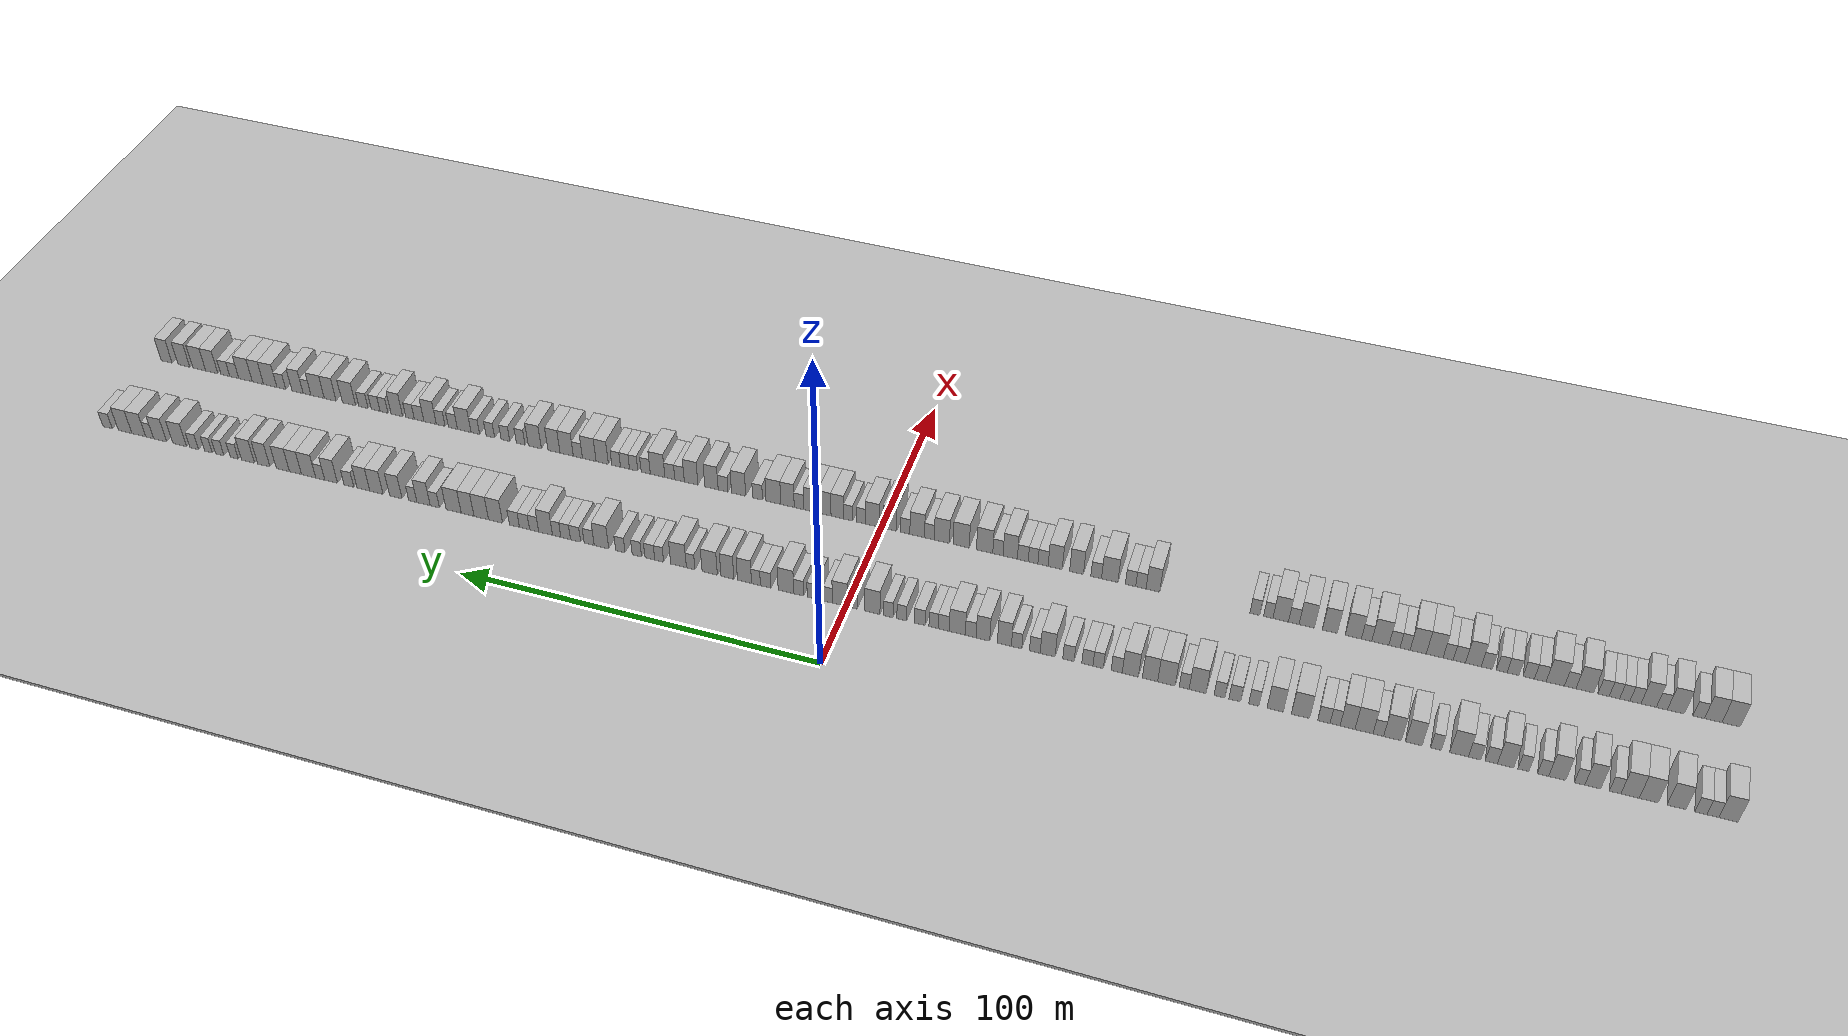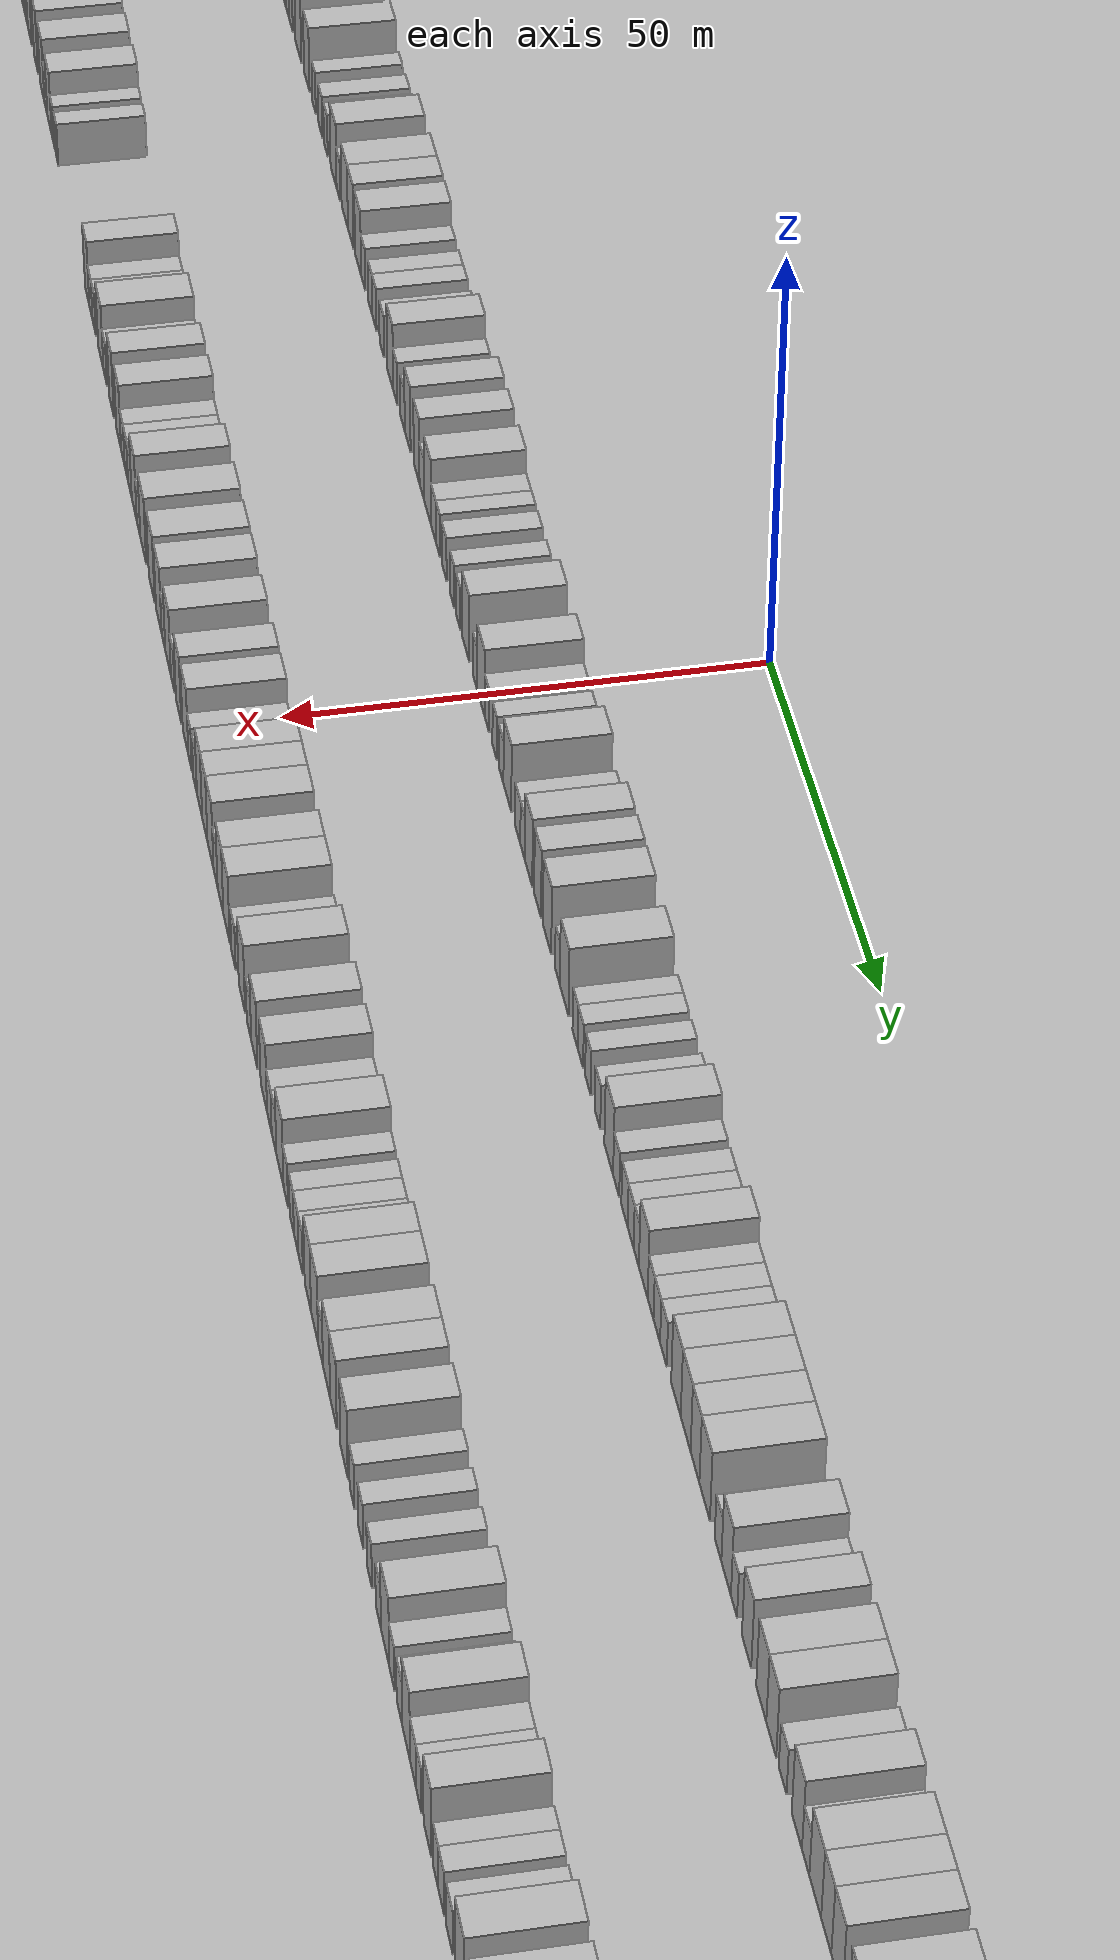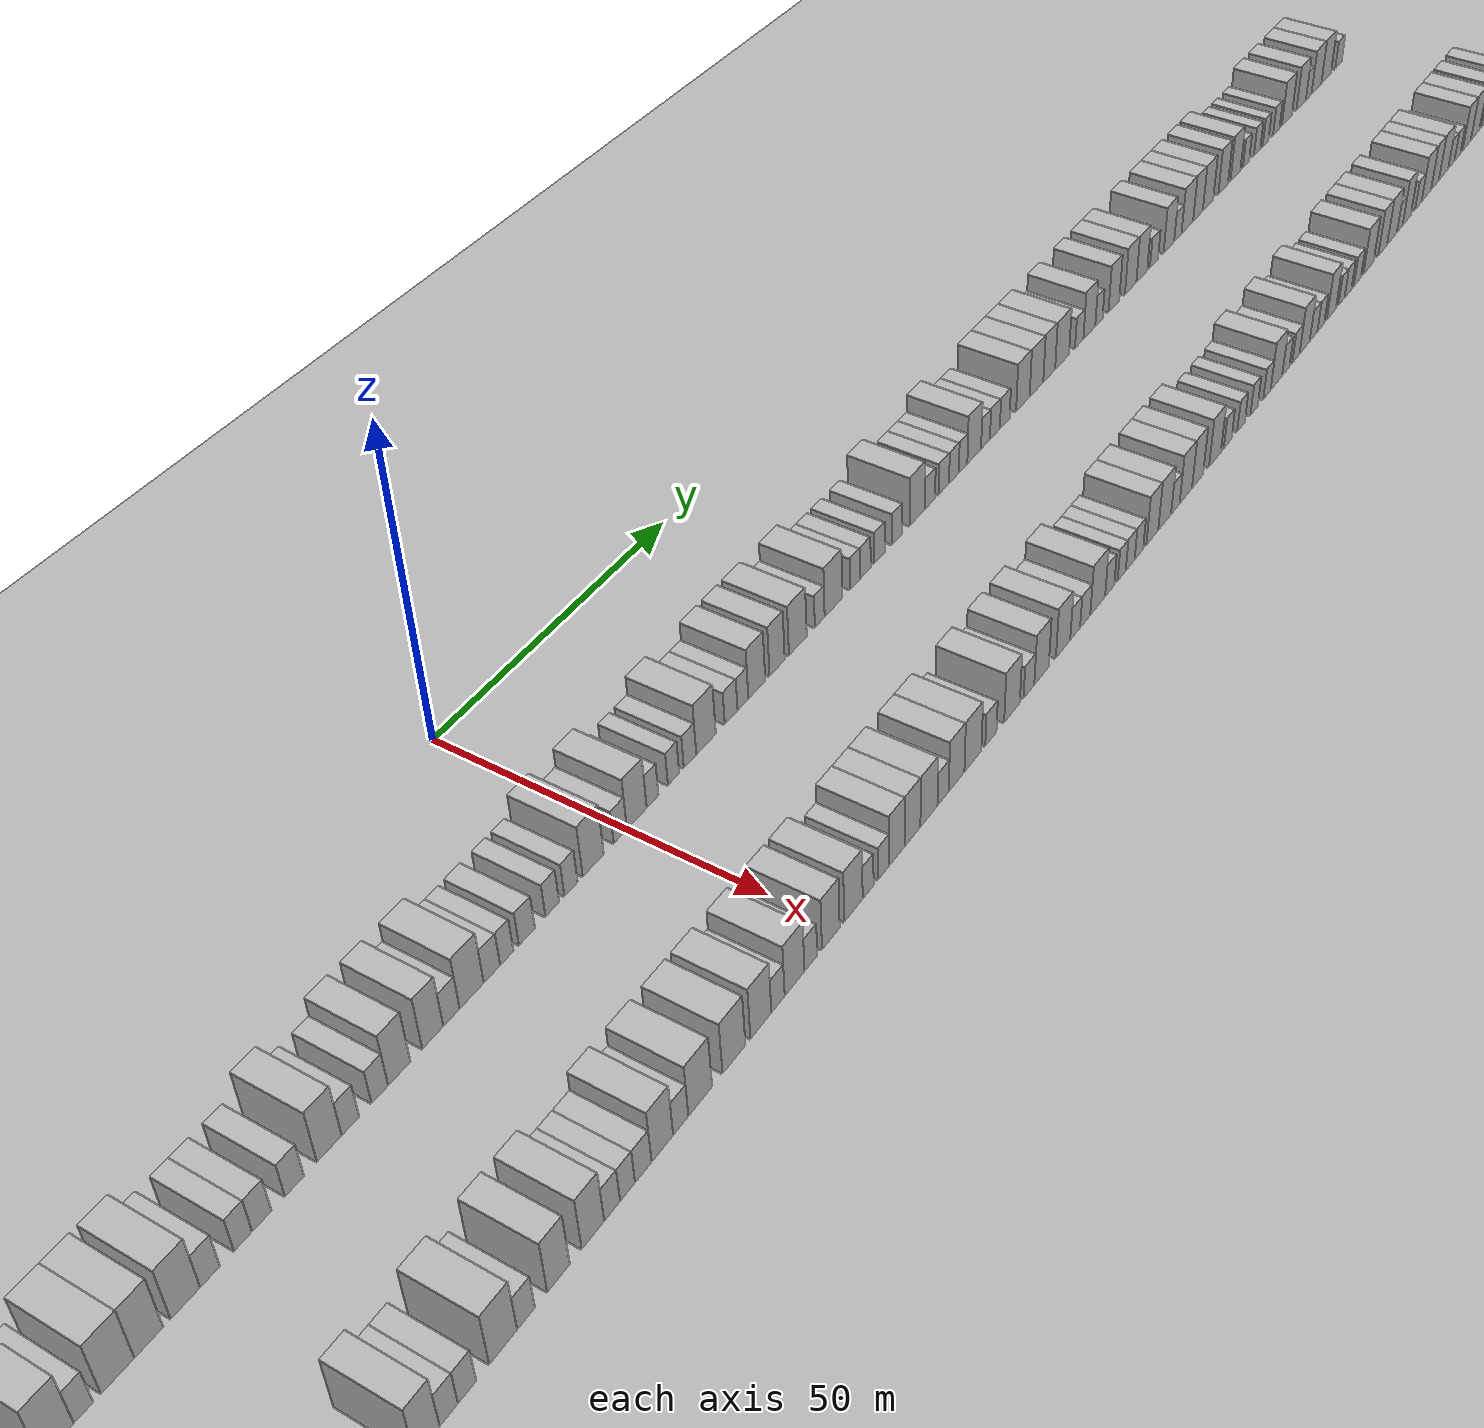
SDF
<?xml version="1.0" encoding="utf-8"?>

<sdf version="1.6">

   <world name="default">

      <gui fullscreen="0">

         <camera name="user_camera">

            <pose>-15 0 4.57585 0 0 0</pose>

            <view_controller>orbit</view_controller>

         </camera>

      </gui>

      <scene>

         <sky>

           <clouds>

             <speed>12</speed>

           </clouds>

         </sky>

         <ambient>0.4 0.4 0.4 1</ambient>

         <background>0.7 0.7 0.7 1</background>

         <shadows>1</shadows>

      </scene>

      <gravity>0 0 -9.8066</gravity>

      <magnetic_field>6e-06 2.3e-05 -4.2e-05</magnetic_field>

      <physics default="0" name="default_physics" type="ode">

         <ode>

            <solver>

               <type>quick</type>

               <iters>10</iters>

               <sor>1.0</sor>

               <use_dynamic_moi_rescaling>0</use_dynamic_moi_rescaling>

            </solver>

            <constraints>

               <cfm>0</cfm>

               <erp>0.2</erp>

               <contact_max_correcting_vel>100</contact_max_correcting_vel>

               <contact_surface_layer>0.001</contact_surface_layer>

            </constraints>

         </ode>

         <max_step_size>0.004</max_step_size>

         <real_time_factor>1</real_time_factor>

         <real_time_update_rate>250</real_time_update_rate>

      </physics>

      <light name="sun" type="directional">

         <cast_shadows>1</cast_shadows>

         <pose>0 0 10 0 0 0</pose>

         <diffuse>0.8 0.8 0.8 1</diffuse>

         <specular>0.2 0.2 0.2 1</specular>

         <attenuation>

            <range>1000</range>

            <constant>0.9</constant>

            <linear>0.01</linear>

            <quadratic>0.001</quadratic>

         </attenuation>

         <direction>-0.5 0.1 -0.9</direction>

      </light>

      <include>

         <name>ground_plane_1</name>

         <uri>model://HANNAS_ground_plane</uri>

         <pose>0 0 0  0 0 0</pose>

      </include>

      <include>

         <name>ground_plane_2</name>

         <uri>model://HANNAS_ground_plane</uri>

         <pose>100 0 0  0 0 0</pose>

      </include>

      <model name="building_1">

         <static>1</static>

         <pose frame="">25.0000 -217.8463 0 0.000000 0.000000 0.000000</pose>

         <link name="link">

            <pose frame="">0 0 4.50 0 0 0</pose>

            <collision name="collision">

               <geometry>

                  <box>

                     <size>10.0000 4.3074 9.0000</size>

                  </box>

               </geometry>

               <max_contacts>10</max_contacts>

               <surface>

                  <contact>

                     <ode/>

                  </contact>

                  <bounce/>

                  <friction>

                     <torsional>

                        <ode/>

                     </torsional>

                     <ode/>

                  </friction>

               </surface>

            </collision>

            <visual name="visual">

               <cast_shadows>0</cast_shadows>

               <geometry>

                  <box>

                     <size>10.0000 4.3074 9.0000</size>

                  </box>

               </geometry>

               <material>

                  <script>

                     <uri>model://HANNAS_wall/materials/scripts</uri>

                     <uri>model://HANNAS_wall/materials/textures</uri>

                     <name>vrc/HANNAS_wall</name>

                  </script>

               </material>

            </visual>

            <self_collide>0</self_collide>

            <enable_wind>0</enable_wind>

            <kinematic>0</kinematic>

         </link>

      </model>

      <model name="building_2">

         <static>1</static>

         <pose frame="">25.0000 -214.3523 0 0.000000 0.000000 0.000000</pose>

         <link name="link">

            <pose frame="">0 0 3.00 0 0 0</pose>

            <collision name="collision">

               <geometry>

                  <box>

                     <size>10.0000 2.6805 6.0000</size>

                  </box>

               </geometry>

               <max_contacts>10</max_contacts>

               <surface>

                  <contact>

                     <ode/>

                  </contact>

                  <bounce/>

                  <friction>

                     <torsional>

                        <ode/>

                     </torsional>

                     <ode/>

                  </friction>

               </surface>

            </collision>

            <visual name="visual">

               <cast_shadows>0</cast_shadows>

               <geometry>

                  <box>

                     <size>10.0000 2.6805 6.0000</size>

                  </box>

               </geometry>

               <material>

                  <script>

                     <uri>model://HANNAS_wall/materials/scripts</uri>

                     <uri>model://HANNAS_wall/materials/textures</uri>

                     <name>vrc/HANNAS_wall</name>

                  </script>

               </material>

            </visual>

            <self_collide>0</self_collide>

            <enable_wind>0</enable_wind>

            <kinematic>0</kinematic>

         </link>

      </model>

      <model name="building_3">

         <static>1</static>

         <pose frame="">25.0000 -211.6491 0 0.000000 0.000000 0.000000</pose>

         <link name="link">

            <pose frame="">0 0 3.00 0 0 0</pose>

            <collision name="collision">

               <geometry>

                  <box>

                     <size>10.0000 2.7260 6.0000</size>

                  </box>

               </geometry>

               <max_contacts>10</max_contacts>

               <surface>

                  <contact>

                     <ode/>

                  </contact>

                  <bounce/>

                  <friction>

                     <torsional>

                        <ode/>

                     </torsional>

                     <ode/>

                  </friction>

               </surface>

            </collision>

            <visual name="visual">

               <cast_shadows>0</cast_shadows>

               <geometry>

                  <box>

                     <size>10.0000 2.7260 6.0000</size>

                  </box>

               </geometry>

               <material>

                  <script>

                     <uri>model://HANNAS_wall/materials/scripts</uri>

                     <uri>model://HANNAS_wall/materials/textures</uri>

                     <name>vrc/HANNAS_wall</name>

                  </script>

               </material>

            </visual>

            <self_collide>0</self_collide>

            <enable_wind>0</enable_wind>

            <kinematic>0</kinematic>

         </link>

      </model>

      <model name="building_4">

         <static>1</static>

         <pose frame="">25.0000 -206.1465 0 0.000000 0.000000 0.000000</pose>

         <link name="link">

            <pose frame="">0 0 4.50 0 0 0</pose>

            <collision name="collision">

               <geometry>

                  <box>

                     <size>10.0000 4.2792 9.0000</size>

                  </box>

               </geometry>

               <max_contacts>10</max_contacts>

               <surface>

                  <contact>

                     <ode/>

                  </contact>

                  <bounce/>

                  <friction>

                     <torsional>

                        <ode/>

                     </torsional>

                     <ode/>

                  </friction>

               </surface>

            </collision>

            <visual name="visual">

               <cast_shadows>0</cast_shadows>

               <geometry>

                  <box>

                     <size>10.0000 4.2792 9.0000</size>

                  </box>

               </geometry>

               <material>

                  <script>

                     <uri>model://HANNAS_wall/materials/scripts</uri>

                     <uri>model://HANNAS_wall/materials/textures</uri>

                     <name>vrc/HANNAS_wall</name>

                  </script>

               </material>

            </visual>

            <self_collide>0</self_collide>

            <enable_wind>0</enable_wind>

            <kinematic>0</kinematic>

         </link>

      </model>

      <model name="building_5">

         <static>1</static>

         <pose frame="">25.0000 -199.8530 0 0.000000 0.000000 0.000000</pose>

         <link name="link">

            <pose frame="">0 0 4.50 0 0 0</pose>

            <collision name="collision">

               <geometry>

                  <box>

                     <size>10.0000 4.3078 9.0000</size>

                  </box>

               </geometry>

               <max_contacts>10</max_contacts>

               <surface>

                  <contact>

                     <ode/>

                  </contact>

                  <bounce/>

                  <friction>

                     <torsional>

                        <ode/>

                     </torsional>

                     <ode/>

                  </friction>

               </surface>

            </collision>

            <visual name="visual">

               <cast_shadows>0</cast_shadows>

               <geometry>

                  <box>

                     <size>10.0000 4.3078 9.0000</size>

                  </box>

               </geometry>

               <material>

                  <script>

                     <uri>model://HANNAS_wall/materials/scripts</uri>

                     <uri>model://HANNAS_wall/materials/textures</uri>

                     <name>vrc/HANNAS_wall</name>

                  </script>

               </material>

            </visual>

            <self_collide>0</self_collide>

            <enable_wind>0</enable_wind>

            <kinematic>0</kinematic>

         </link>

      </model>

      <model name="building_6">

         <static>1</static>

         <pose frame="">25.0000 -195.5964 0 0.000000 0.000000 0.000000</pose>

         <link name="link">

            <pose frame="">0 0 4.50 0 0 0</pose>

            <collision name="collision">

               <geometry>

                  <box>

                     <size>10.0000 4.2055 9.0000</size>

                  </box>

               </geometry>

               <max_contacts>10</max_contacts>

               <surface>

                  <contact>

                     <ode/>

                  </contact>

                  <bounce/>

                  <friction>

                     <torsional>

                        <ode/>

                     </torsional>

                     <ode/>

                  </friction>

               </surface>

            </collision>

            <visual name="visual">

               <cast_shadows>0</cast_shadows>

               <geometry>

                  <box>

                     <size>10.0000 4.2055 9.0000</size>

                  </box>

               </geometry>

               <material>

                  <script>

                     <uri>model://HANNAS_wall/materials/scripts</uri>

                     <uri>model://HANNAS_wall/materials/textures</uri>

                     <name>vrc/HANNAS_wall</name>

                  </script>

               </material>

            </visual>

            <self_collide>0</self_collide>

            <enable_wind>0</enable_wind>

            <kinematic>0</kinematic>

         </link>

      </model>

      <model name="building_7">

         <static>1</static>

         <pose frame="">25.0000 -192.1730 0 0.000000 0.000000 0.000000</pose>

         <link name="link">

            <pose frame="">0 0 3.00 0 0 0</pose>

            <collision name="collision">

               <geometry>

                  <box>

                     <size>10.0000 2.6413 6.0000</size>

                  </box>

               </geometry>

               <max_contacts>10</max_contacts>

               <surface>

                  <contact>

                     <ode/>

                  </contact>

                  <bounce/>

                  <friction>

                     <torsional>

                        <ode/>

                     </torsional>

                     <ode/>

                  </friction>

               </surface>

            </collision>

            <visual name="visual">

               <cast_shadows>0</cast_shadows>

               <geometry>

                  <box>

                     <size>10.0000 2.6413 6.0000</size>

                  </box>

               </geometry>

               <material>

                  <script>

                     <uri>model://HANNAS_wall/materials/scripts</uri>

                     <uri>model://HANNAS_wall/materials/textures</uri>

                     <name>vrc/HANNAS_wall</name>

                  </script>

               </material>

            </visual>

            <self_collide>0</self_collide>

            <enable_wind>0</enable_wind>

            <kinematic>0</kinematic>

         </link>

      </model>

      <model name="building_8">

         <static>1</static>

         <pose frame="">25.0000 -187.0257 0 0.000000 0.000000 0.000000</pose>

         <link name="link">

            <pose frame="">0 0 4.50 0 0 0</pose>

            <collision name="collision">

               <geometry>

                  <box>

                     <size>10.0000 3.6533 9.0000</size>

                  </box>

               </geometry>

               <max_contacts>10</max_contacts>

               <surface>

                  <contact>

                     <ode/>

                  </contact>

                  <bounce/>

                  <friction>

                     <torsional>

                        <ode/>

                     </torsional>

                     <ode/>

                  </friction>

               </surface>

            </collision>

            <visual name="visual">

               <cast_shadows>0</cast_shadows>

               <geometry>

                  <box>

                     <size>10.0000 3.6533 9.0000</size>

                  </box>

               </geometry>

               <material>

                  <script>

                     <uri>model://HANNAS_wall/materials/scripts</uri>

                     <uri>model://HANNAS_wall/materials/textures</uri>

                     <name>vrc/HANNAS_wall</name>

                  </script>

               </material>

            </visual>

            <self_collide>0</self_collide>

            <enable_wind>0</enable_wind>

            <kinematic>0</kinematic>

         </link>

      </model>

      <model name="building_9">

         <static>1</static>

         <pose frame="">25.0000 -183.9845 0 0.000000 0.000000 0.000000</pose>

         <link name="link">

            <pose frame="">0 0 3.00 0 0 0</pose>

            <collision name="collision">

               <geometry>

                  <box>

                     <size>10.0000 2.4291 6.0000</size>

                  </box>

               </geometry>

               <max_contacts>10</max_contacts>

               <surface>

                  <contact>

                     <ode/>

                  </contact>

                  <bounce/>

                  <friction>

                     <torsional>

                        <ode/>

                     </torsional>

                     <ode/>

                  </friction>

               </surface>

            </collision>

            <visual name="visual">

               <cast_shadows>0</cast_shadows>

               <geometry>

                  <box>

                     <size>10.0000 2.4291 6.0000</size>

                  </box>

               </geometry>

               <material>

                  <script>

                     <uri>model://HANNAS_wall/materials/scripts</uri>

                     <uri>model://HANNAS_wall/materials/textures</uri>

                     <name>vrc/HANNAS_wall</name>

                  </script>

               </material>

            </visual>

            <self_collide>0</self_collide>

            <enable_wind>0</enable_wind>

            <kinematic>0</kinematic>

         </link>

      </model>

      <model name="building_10">

         <static>1</static>

         <pose frame="">25.0000 -178.7995 0 0.000000 0.000000 0.000000</pose>

         <link name="link">

            <pose frame="">0 0 4.50 0 0 0</pose>

            <collision name="collision">

               <geometry>

                  <box>

                     <size>10.0000 3.9409 9.0000</size>

                  </box>

               </geometry>

               <max_contacts>10</max_contacts>

               <surface>

                  <contact>

                     <ode/>

                  </contact>

                  <bounce/>

                  <friction>

                     <torsional>

                        <ode/>

                     </torsional>

                     <ode/>

                  </friction>

               </surface>

            </collision>

            <visual name="visual">

               <cast_shadows>0</cast_shadows>

               <geometry>

                  <box>

                     <size>10.0000 3.9409 9.0000</size>

                  </box>

               </geometry>

               <material>

                  <script>

                     <uri>model://HANNAS_wall/materials/scripts</uri>

                     <uri>model://HANNAS_wall/materials/textures</uri>

                     <name>vrc/HANNAS_wall</name>

                  </script>

               </material>

            </visual>

            <self_collide>0</self_collide>

            <enable_wind>0</enable_wind>

            <kinematic>0</kinematic>

         </link>

      </model>

      <model name="building_11">

         <static>1</static>

         <pose frame="">25.0000 -175.5220 0 0.000000 0.000000 0.000000</pose>

         <link name="link">

            <pose frame="">0 0 3.00 0 0 0</pose>

            <collision name="collision">

               <geometry>

                  <box>

                     <size>10.0000 2.6142 6.0000</size>

                  </box>

               </geometry>

               <max_contacts>10</max_contacts>

               <surface>

                  <contact>

                     <ode/>

                  </contact>

                  <bounce/>

                  <friction>

                     <torsional>

                        <ode/>

                     </torsional>

                     <ode/>

                  </friction>

               </surface>

            </collision>

            <visual name="visual">

               <cast_shadows>0</cast_shadows>

               <geometry>

                  <box>

                     <size>10.0000 2.6142 6.0000</size>

                  </box>

               </geometry>

               <material>

                  <script>

                     <uri>model://HANNAS_wall/materials/scripts</uri>

                     <uri>model://HANNAS_wall/materials/textures</uri>

                     <name>vrc/HANNAS_wall</name>

                  </script>

               </material>

            </visual>

            <self_collide>0</self_collide>

            <enable_wind>0</enable_wind>

            <kinematic>0</kinematic>

         </link>

      </model>

      <model name="building_12">

         <static>1</static>

         <pose frame="">25.0000 -170.9310 0 0.000000 0.000000 0.000000</pose>

         <link name="link">

            <pose frame="">0 0 3.00 0 0 0</pose>

            <collision name="collision">

               <geometry>

                  <box>

                     <size>10.0000 2.5679 6.0000</size>

                  </box>

               </geometry>

               <max_contacts>10</max_contacts>

               <surface>

                  <contact>

                     <ode/>

                  </contact>

                  <bounce/>

                  <friction>

                     <torsional>

                        <ode/>

                     </torsional>

                     <ode/>

                  </friction>

               </surface>

            </collision>

            <visual name="visual">

               <cast_shadows>0</cast_shadows>

               <geometry>

                  <box>

                     <size>10.0000 2.5679 6.0000</size>

                  </box>

               </geometry>

               <material>

                  <script>

                     <uri>model://HANNAS_wall/materials/scripts</uri>

                     <uri>model://HANNAS_wall/materials/textures</uri>

                     <name>vrc/HANNAS_wall</name>

                  </script>

               </material>

            </visual>

            <self_collide>0</self_collide>

            <enable_wind>0</enable_wind>

            <kinematic>0</kinematic>

         </link>

      </model>

      <model name="building_13">

         <static>1</static>

         <pose frame="">25.0000 -166.7279 0 0.000000 0.000000 0.000000</pose>

         <link name="link">

            <pose frame="">0 0 4.50 0 0 0</pose>

            <collision name="collision">

               <geometry>

                  <box>

                     <size>10.0000 3.8383 9.0000</size>

                  </box>

               </geometry>

               <max_contacts>10</max_contacts>

               <surface>

                  <contact>

                     <ode/>

                  </contact>

                  <bounce/>

                  <friction>

                     <torsional>

                        <ode/>

                     </torsional>

                     <ode/>

                  </friction>

               </surface>

            </collision>

            <visual name="visual">

               <cast_shadows>0</cast_shadows>

               <geometry>

                  <box>

                     <size>10.0000 3.8383 9.0000</size>

                  </box>

               </geometry>

               <material>

                  <script>

                     <uri>model://HANNAS_wall/materials/scripts</uri>

                     <uri>model://HANNAS_wall/materials/textures</uri>

                     <name>vrc/HANNAS_wall</name>

                  </script>

               </material>

            </visual>

            <self_collide>0</self_collide>

            <enable_wind>0</enable_wind>

            <kinematic>0</kinematic>

         </link>

      </model>

      <model name="building_14">

         <static>1</static>

         <pose frame="">25.0000 -163.3704 0 0.000000 0.000000 0.000000</pose>

         <link name="link">

            <pose frame="">0 0 3.00 0 0 0</pose>

            <collision name="collision">

               <geometry>

                  <box>

                     <size>10.0000 2.8766 6.0000</size>

                  </box>

               </geometry>

               <max_contacts>10</max_contacts>

               <surface>

                  <contact>

                     <ode/>

                  </contact>

                  <bounce/>

                  <friction>

                     <torsional>

                        <ode/>

                     </torsional>

                     <ode/>

                  </friction>

               </surface>

            </collision>

            <visual name="visual">

               <cast_shadows>0</cast_shadows>

               <geometry>

                  <box>

                     <size>10.0000 2.8766 6.0000</size>

                  </box>

               </geometry>

               <material>

                  <script>

                     <uri>model://HANNAS_wall/materials/scripts</uri>

                     <uri>model://HANNAS_wall/materials/textures</uri>

                     <name>vrc/HANNAS_wall</name>

                  </script>

               </material>

            </visual>

            <self_collide>0</self_collide>

            <enable_wind>0</enable_wind>

            <kinematic>0</kinematic>

         </link>

      </model>

      <model name="building_15">

         <static>1</static>

         <pose frame="">25.0000 -159.4511 0 0.000000 0.000000 0.000000</pose>

         <link name="link">

            <pose frame="">0 0 3.00 0 0 0</pose>

            <collision name="collision">

               <geometry>

                  <box>

                     <size>10.0000 2.9620 6.0000</size>

                  </box>

               </geometry>

               <max_contacts>10</max_contacts>

               <surface>

                  <contact>

                     <ode/>

                  </contact>

                  <bounce/>

                  <friction>

                     <torsional>

                        <ode/>

                     </torsional>

                     <ode/>

                  </friction>

               </surface>

            </collision>

            <visual name="visual">

               <cast_shadows>0</cast_shadows>

               <geometry>

                  <box>

                     <size>10.0000 2.9620 6.0000</size>

                  </box>

               </geometry>

               <material>

                  <script>

                     <uri>model://HANNAS_wall/materials/scripts</uri>

                     <uri>model://HANNAS_wall/materials/textures</uri>

                     <name>vrc/HANNAS_wall</name>

                  </script>

               </material>

            </visual>

            <self_collide>0</self_collide>

            <enable_wind>0</enable_wind>

            <kinematic>0</kinematic>

         </link>

      </model>

      <model name="building_16">

         <static>1</static>

         <pose frame="">25.0000 -155.7571 0 0.000000 0.000000 0.000000</pose>

         <link name="link">

            <pose frame="">0 0 4.50 0 0 0</pose>

            <collision name="collision">

               <geometry>

                  <box>

                     <size>10.0000 4.4260 9.0000</size>

                  </box>

               </geometry>

               <max_contacts>10</max_contacts>

               <surface>

                  <contact>

                     <ode/>

                  </contact>

                  <bounce/>

                  <friction>

                     <torsional>

                        <ode/>

                     </torsional>

                     <ode/>

                  </friction>

               </surface>

            </collision>

            <visual name="visual">

               <cast_shadows>0</cast_shadows>

               <geometry>

                  <box>

                     <size>10.0000 4.4260 9.0000</size>

                  </box>

               </geometry>

               <material>

                  <script>

                     <uri>model://HANNAS_wall/materials/scripts</uri>

                     <uri>model://HANNAS_wall/materials/textures</uri>

                     <name>vrc/HANNAS_wall</name>

                  </script>

               </material>

            </visual>

            <self_collide>0</self_collide>

            <enable_wind>0</enable_wind>

            <kinematic>0</kinematic>

         </link>

      </model>

      <model name="building_17">

         <static>1</static>

         <pose frame="">25.0000 -150.2537 0 0.000000 0.000000 0.000000</pose>

         <link name="link">

            <pose frame="">0 0 3.00 0 0 0</pose>

            <collision name="collision">

               <geometry>

                  <box>

                     <size>10.0000 2.5807 6.0000</size>

                  </box>

               </geometry>

               <max_contacts>10</max_contacts>

               <surface>

                  <contact>

                     <ode/>

                  </contact>

                  <bounce/>

                  <friction>

                     <torsional>

                        <ode/>

                     </torsional>

                     <ode/>

                  </friction>

               </surface>

            </collision>

            <visual name="visual">

               <cast_shadows>0</cast_shadows>

               <geometry>

                  <box>

                     <size>10.0000 2.5807 6.0000</size>

                  </box>

               </geometry>

               <material>

                  <script>

                     <uri>model://HANNAS_wall/materials/scripts</uri>

                     <uri>model://HANNAS_wall/materials/textures</uri>

                     <name>vrc/HANNAS_wall</name>

                  </script>

               </material>

            </visual>

            <self_collide>0</self_collide>

            <enable_wind>0</enable_wind>

            <kinematic>0</kinematic>

         </link>

      </model>

      <model name="building_18">

         <static>1</static>

         <pose frame="">25.0000 -144.9676 0 0.000000 0.000000 0.000000</pose>

         <link name="link">

            <pose frame="">0 0 4.50 0 0 0</pose>

            <collision name="collision">

               <geometry>

                  <box>

                     <size>10.0000 3.9914 9.0000</size>

                  </box>

               </geometry>

               <max_contacts>10</max_contacts>

               <surface>

                  <contact>

                     <ode/>

                  </contact>

                  <bounce/>

                  <friction>

                     <torsional>

                        <ode/>

                     </torsional>

                     <ode/>

                  </friction>

               </surface>

            </collision>

            <visual name="visual">

               <cast_shadows>0</cast_shadows>

               <geometry>

                  <box>

                     <size>10.0000 3.9914 9.0000</size>

                  </box>

               </geometry>

               <material>

                  <script>

                     <uri>model://HANNAS_wall/materials/scripts</uri>

                     <uri>model://HANNAS_wall/materials/textures</uri>

                     <name>vrc/HANNAS_wall</name>

                  </script>

               </material>

            </visual>

            <self_collide>0</self_collide>

            <enable_wind>0</enable_wind>

            <kinematic>0</kinematic>

         </link>

      </model>

      <model name="building_19">

         <static>1</static>

         <pose frame="">25.0000 -139.8458 0 0.000000 0.000000 0.000000</pose>

         <link name="link">

            <pose frame="">0 0 4.50 0 0 0</pose>

            <collision name="collision">

               <geometry>

                  <box>

                     <size>10.0000 4.2523 9.0000</size>

                  </box>

               </geometry>

               <max_contacts>10</max_contacts>

               <surface>

                  <contact>

                     <ode/>

                  </contact>

                  <bounce/>

                  <friction>

                     <torsional>

                        <ode/>

                     </torsional>

                     <ode/>

                  </friction>

               </surface>

            </collision>

            <visual name="visual">

               <cast_shadows>0</cast_shadows>

               <geometry>

                  <box>

                     <size>10.0000 4.2523 9.0000</size>

                  </box>

               </geometry>

               <material>

                  <script>

                     <uri>model://HANNAS_wall/materials/scripts</uri>

                     <uri>model://HANNAS_wall/materials/textures</uri>

                     <name>vrc/HANNAS_wall</name>

                  </script>

               </material>

            </visual>

            <self_collide>0</self_collide>

            <enable_wind>0</enable_wind>

            <kinematic>0</kinematic>

         </link>

      </model>

      <model name="building_20">

         <static>1</static>

         <pose frame="">25.0000 -136.4243 0 0.000000 0.000000 0.000000</pose>

         <link name="link">

            <pose frame="">0 0 3.00 0 0 0</pose>

            <collision name="collision">

               <geometry>

                  <box>

                     <size>10.0000 2.5906 6.0000</size>

                  </box>

               </geometry>

               <max_contacts>10</max_contacts>

               <surface>

                  <contact>

                     <ode/>

                  </contact>

                  <bounce/>

                  <friction>

                     <torsional>

                        <ode/>

                     </torsional>

                     <ode/>

                  </friction>

               </surface>

            </collision>

            <visual name="visual">

               <cast_shadows>0</cast_shadows>

               <geometry>

                  <box>

                     <size>10.0000 2.5906 6.0000</size>

                  </box>

               </geometry>

               <material>

                  <script>

                     <uri>model://HANNAS_wall/materials/scripts</uri>

                     <uri>model://HANNAS_wall/materials/textures</uri>

                     <name>vrc/HANNAS_wall</name>

                  </script>

               </material>

            </visual>

            <self_collide>0</self_collide>

            <enable_wind>0</enable_wind>

            <kinematic>0</kinematic>

         </link>

      </model>

      <model name="building_21">

         <static>1</static>

         <pose frame="">25.0000 -132.9576 0 0.000000 0.000000 0.000000</pose>

         <link name="link">

            <pose frame="">0 0 4.50 0 0 0</pose>

            <collision name="collision">

               <geometry>

                  <box>

                     <size>10.0000 4.3429 9.0000</size>

                  </box>

               </geometry>

               <max_contacts>10</max_contacts>

               <surface>

                  <contact>

                     <ode/>

                  </contact>

                  <bounce/>

                  <friction>

                     <torsional>

                        <ode/>

                     </torsional>

                     <ode/>

                  </friction>

               </surface>

            </collision>

            <visual name="visual">

               <cast_shadows>0</cast_shadows>

               <geometry>

                  <box>

                     <size>10.0000 4.3429 9.0000</size>

                  </box>

               </geometry>

               <material>

                  <script>

                     <uri>model://HANNAS_wall/materials/scripts</uri>

                     <uri>model://HANNAS_wall/materials/textures</uri>

                     <name>vrc/HANNAS_wall</name>

                  </script>

               </material>

            </visual>

            <self_collide>0</self_collide>

            <enable_wind>0</enable_wind>

            <kinematic>0</kinematic>

         </link>

      </model>

      <model name="building_22">

         <static>1</static>

         <pose frame="">25.0000 -128.9731 0 0.000000 0.000000 0.000000</pose>

         <link name="link">

            <pose frame="">0 0 4.50 0 0 0</pose>

            <collision name="collision">

               <geometry>

                  <box>

                     <size>10.0000 3.6260 9.0000</size>

                  </box>

               </geometry>

               <max_contacts>10</max_contacts>

               <surface>

                  <contact>

                     <ode/>

                  </contact>

                  <bounce/>

                  <friction>

                     <torsional>

                        <ode/>

                     </torsional>

                     <ode/>

                  </friction>

               </surface>

            </collision>

            <visual name="visual">

               <cast_shadows>0</cast_shadows>

               <geometry>

                  <box>

                     <size>10.0000 3.6260 9.0000</size>

                  </box>

               </geometry>

               <material>

                  <script>

                     <uri>model://HANNAS_wall/materials/scripts</uri>

                     <uri>model://HANNAS_wall/materials/textures</uri>

                     <name>vrc/HANNAS_wall</name>

                  </script>

               </material>

            </visual>

            <self_collide>0</self_collide>

            <enable_wind>0</enable_wind>

            <kinematic>0</kinematic>

         </link>

      </model>

      <model name="building_23">

         <static>1</static>

         <pose frame="">25.0000 -125.9395 0 0.000000 0.000000 0.000000</pose>

         <link name="link">

            <pose frame="">0 0 3.00 0 0 0</pose>

            <collision name="collision">

               <geometry>

                  <box>

                     <size>10.0000 2.4413 6.0000</size>

                  </box>

               </geometry>

               <max_contacts>10</max_contacts>

               <surface>

                  <contact>

                     <ode/>

                  </contact>

                  <bounce/>

                  <friction>

                     <torsional>

                        <ode/>

                     </torsional>

                     <ode/>

                  </friction>

               </surface>

            </collision>

            <visual name="visual">

               <cast_shadows>0</cast_shadows>

               <geometry>

                  <box>

                     <size>10.0000 2.4413 6.0000</size>

                  </box>

               </geometry>

               <material>

                  <script>

                     <uri>model://HANNAS_wall/materials/scripts</uri>

                     <uri>model://HANNAS_wall/materials/textures</uri>

                     <name>vrc/HANNAS_wall</name>

                  </script>

               </material>

            </visual>

            <self_collide>0</self_collide>

            <enable_wind>0</enable_wind>

            <kinematic>0</kinematic>

         </link>

      </model>

      <model name="building_24">

         <static>1</static>

         <pose frame="">25.0000 -123.2206 0 0.000000 0.000000 0.000000</pose>

         <link name="link">

            <pose frame="">0 0 3.00 0 0 0</pose>

            <collision name="collision">

               <geometry>

                  <box>

                     <size>10.0000 2.9964 6.0000</size>

                  </box>

               </geometry>

               <max_contacts>10</max_contacts>

               <surface>

                  <contact>

                     <ode/>

                  </contact>

                  <bounce/>

                  <friction>

                     <torsional>

                        <ode/>

                     </torsional>

                     <ode/>

                  </friction>

               </surface>

            </collision>

            <visual name="visual">

               <cast_shadows>0</cast_shadows>

               <geometry>

                  <box>

                     <size>10.0000 2.9964 6.0000</size>

                  </box>

               </geometry>

               <material>

                  <script>

                     <uri>model://HANNAS_wall/materials/scripts</uri>

                     <uri>model://HANNAS_wall/materials/textures</uri>

                     <name>vrc/HANNAS_wall</name>

                  </script>

               </material>

            </visual>

            <self_collide>0</self_collide>

            <enable_wind>0</enable_wind>

            <kinematic>0</kinematic>

         </link>

      </model>

      <model name="building_25">

         <static>1</static>

         <pose frame="">25.0000 -117.4849 0 0.000000 0.000000 0.000000</pose>

         <link name="link">

            <pose frame="">0 0 4.50 0 0 0</pose>

            <collision name="collision">

               <geometry>

                  <box>

                     <size>10.0000 4.4751 9.0000</size>

                  </box>

               </geometry>

               <max_contacts>10</max_contacts>

               <surface>

                  <contact>

                     <ode/>

                  </contact>

                  <bounce/>

                  <friction>

                     <torsional>

                        <ode/>

                     </torsional>

                     <ode/>

                  </friction>

               </surface>

            </collision>

            <visual name="visual">

               <cast_shadows>0</cast_shadows>

               <geometry>

                  <box>

                     <size>10.0000 4.4751 9.0000</size>

                  </box>

               </geometry>

               <material>

                  <script>

                     <uri>model://HANNAS_wall/materials/scripts</uri>

                     <uri>model://HANNAS_wall/materials/textures</uri>

                     <name>vrc/HANNAS_wall</name>

                  </script>

               </material>

            </visual>

            <self_collide>0</self_collide>

            <enable_wind>0</enable_wind>

            <kinematic>0</kinematic>

         </link>

      </model>

      <model name="building_26">

         <static>1</static>

         <pose frame="">25.0000 -111.2404 0 0.000000 0.000000 0.000000</pose>

         <link name="link">

            <pose frame="">0 0 4.50 0 0 0</pose>

            <collision name="collision">

               <geometry>

                  <box>

                     <size>10.0000 4.0138 9.0000</size>

                  </box>

               </geometry>

               <max_contacts>10</max_contacts>

               <surface>

                  <contact>

                     <ode/>

                  </contact>

                  <bounce/>

                  <friction>

                     <torsional>

                        <ode/>

                     </torsional>

                     <ode/>

                  </friction>

               </surface>

            </collision>

            <visual name="visual">

               <cast_shadows>0</cast_shadows>

               <geometry>

                  <box>

                     <size>10.0000 4.0138 9.0000</size>

                  </box>

               </geometry>

               <material>

                  <script>

                     <uri>model://HANNAS_wall/materials/scripts</uri>

                     <uri>model://HANNAS_wall/materials/textures</uri>

                     <name>vrc/HANNAS_wall</name>

                  </script>

               </material>

            </visual>

            <self_collide>0</self_collide>

            <enable_wind>0</enable_wind>

            <kinematic>0</kinematic>

         </link>

      </model>

      <model name="building_27">

         <static>1</static>

         <pose frame="">25.0000 -105.9626 0 0.000000 0.000000 0.000000</pose>

         <link name="link">

            <pose frame="">0 0 3.00 0 0 0</pose>

            <collision name="collision">

               <geometry>

                  <box>

                     <size>10.0000 2.5419 6.0000</size>

                  </box>

               </geometry>

               <max_contacts>10</max_contacts>

               <surface>

                  <contact>

                     <ode/>

                  </contact>

                  <bounce/>

                  <friction>

                     <torsional>

                        <ode/>

                     </torsional>

                     <ode/>

                  </friction>

               </surface>

            </collision>

            <visual name="visual">

               <cast_shadows>0</cast_shadows>

               <geometry>

                  <box>

                     <size>10.0000 2.5419 6.0000</size>

                  </box>

               </geometry>

               <material>

                  <script>

                     <uri>model://HANNAS_wall/materials/scripts</uri>

                     <uri>model://HANNAS_wall/materials/textures</uri>

                     <name>vrc/HANNAS_wall</name>

                  </script>

               </material>

            </visual>

            <self_collide>0</self_collide>

            <enable_wind>0</enable_wind>

            <kinematic>0</kinematic>

         </link>

      </model>

      <model name="building_28">

         <static>1</static>

         <pose frame="">25.0000 -101.2293 0 0.000000 0.000000 0.000000</pose>

         <link name="link">

            <pose frame="">0 0 3.00 0 0 0</pose>

            <collision name="collision">

               <geometry>

                  <box>

                     <size>10.0000 2.9246 6.0000</size>

                  </box>

               </geometry>

               <max_contacts>10</max_contacts>

               <surface>

                  <contact>

                     <ode/>

                  </contact>

                  <bounce/>

                  <friction>

                     <torsional>

                        <ode/>

                     </torsional>

                     <ode/>

                  </friction>

               </surface>

            </collision>

            <visual name="visual">

               <cast_shadows>0</cast_shadows>

               <geometry>

                  <box>

                     <size>10.0000 2.9246 6.0000</size>

                  </box>

               </geometry>

               <material>

                  <script>

                     <uri>model://HANNAS_wall/materials/scripts</uri>

                     <uri>model://HANNAS_wall/materials/textures</uri>

                     <name>vrc/HANNAS_wall</name>

                  </script>

               </material>

            </visual>

            <self_collide>0</self_collide>

            <enable_wind>0</enable_wind>

            <kinematic>0</kinematic>

         </link>

      </model>

      <model name="building_29">

         <static>1</static>

         <pose frame="">25.0000 -97.4095 0 0.000000 0.000000 0.000000</pose>

         <link name="link">

            <pose frame="">0 0 3.00 0 0 0</pose>

            <collision name="collision">

               <geometry>

                  <box>

                     <size>10.0000 2.7150 6.0000</size>

                  </box>

               </geometry>

               <max_contacts>10</max_contacts>

               <surface>

                  <contact>

                     <ode/>

                  </contact>

                  <bounce/>

                  <friction>

                     <torsional>

                        <ode/>

                     </torsional>

                     <ode/>

                  </friction>

               </surface>

            </collision>

            <visual name="visual">

               <cast_shadows>0</cast_shadows>

               <geometry>

                  <box>

                     <size>10.0000 2.7150 6.0000</size>

                  </box>

               </geometry>

               <material>

                  <script>

                     <uri>model://HANNAS_wall/materials/scripts</uri>

                     <uri>model://HANNAS_wall/materials/textures</uri>

                     <name>vrc/HANNAS_wall</name>

                  </script>

               </material>

            </visual>

            <self_collide>0</self_collide>

            <enable_wind>0</enable_wind>

            <kinematic>0</kinematic>

         </link>

      </model>

      <model name="building_30">

         <static>1</static>

         <pose frame="">25.0000 -91.9253 0 0.000000 0.000000 0.000000</pose>

         <link name="link">

            <pose frame="">0 0 4.50 0 0 0</pose>

            <collision name="collision">

               <geometry>

                  <box>

                     <size>10.0000 4.2534 9.0000</size>

                  </box>

               </geometry>

               <max_contacts>10</max_contacts>

               <surface>

                  <contact>

                     <ode/>

                  </contact>

                  <bounce/>

                  <friction>

                     <torsional>

                        <ode/>

                     </torsional>

                     <ode/>

                  </friction>

               </surface>

            </collision>

            <visual name="visual">

               <cast_shadows>0</cast_shadows>

               <geometry>

                  <box>

                     <size>10.0000 4.2534 9.0000</size>

                  </box>

               </geometry>

               <material>

                  <script>

                     <uri>model://HANNAS_wall/materials/scripts</uri>

                     <uri>model://HANNAS_wall/materials/textures</uri>

                     <name>vrc/HANNAS_wall</name>

                  </script>

               </material>

            </visual>

            <self_collide>0</self_collide>

            <enable_wind>0</enable_wind>

            <kinematic>0</kinematic>

         </link>

      </model>

      <model name="building_31">

         <static>1</static>

         <pose frame="">25.0000 -88.5392 0 0.000000 0.000000 0.000000</pose>

         <link name="link">

            <pose frame="">0 0 3.00 0 0 0</pose>

            <collision name="collision">

               <geometry>

                  <box>

                     <size>10.0000 2.5188 6.0000</size>

                  </box>

               </geometry>

               <max_contacts>10</max_contacts>

               <surface>

                  <contact>

                     <ode/>

                  </contact>

                  <bounce/>

                  <friction>

                     <torsional>

                        <ode/>

                     </torsional>

                     <ode/>

                  </friction>

               </surface>

            </collision>

            <visual name="visual">

               <cast_shadows>0</cast_shadows>

               <geometry>

                  <box>

                     <size>10.0000 2.5188 6.0000</size>

                  </box>

               </geometry>

               <material>

                  <script>

                     <uri>model://HANNAS_wall/materials/scripts</uri>

                     <uri>model://HANNAS_wall/materials/textures</uri>

                     <name>vrc/HANNAS_wall</name>

                  </script>

               </material>

            </visual>

            <self_collide>0</self_collide>

            <enable_wind>0</enable_wind>

            <kinematic>0</kinematic>

         </link>

      </model>

      <model name="building_32">

         <static>1</static>

         <pose frame="">25.0000 -84.0698 0 0.000000 0.000000 0.000000</pose>

         <link name="link">

            <pose frame="">0 0 4.50 0 0 0</pose>

            <collision name="collision">

               <geometry>

                  <box>

                     <size>10.0000 4.4201 9.0000</size>

                  </box>

               </geometry>

               <max_contacts>10</max_contacts>

               <surface>

                  <contact>

                     <ode/>

                  </contact>

                  <bounce/>

                  <friction>

                     <torsional>

                        <ode/>

                     </torsional>

                     <ode/>

                  </friction>

               </surface>

            </collision>

            <visual name="visual">

               <cast_shadows>0</cast_shadows>

               <geometry>

                  <box>

                     <size>10.0000 4.4201 9.0000</size>

                  </box>

               </geometry>

               <material>

                  <script>

                     <uri>model://HANNAS_wall/materials/scripts</uri>

                     <uri>model://HANNAS_wall/materials/textures</uri>

                     <name>vrc/HANNAS_wall</name>

                  </script>

               </material>

            </visual>

            <self_collide>0</self_collide>

            <enable_wind>0</enable_wind>

            <kinematic>0</kinematic>

         </link>

      </model>

      <model name="building_33">

         <static>1</static>

         <pose frame="">25.0000 -79.8985 0 0.000000 0.000000 0.000000</pose>

         <link name="link">

            <pose frame="">0 0 4.50 0 0 0</pose>

            <collision name="collision">

               <geometry>

                  <box>

                     <size>10.0000 3.9224 9.0000</size>

                  </box>

               </geometry>

               <max_contacts>10</max_contacts>

               <surface>

                  <contact>

                     <ode/>

                  </contact>

                  <bounce/>

                  <friction>

                     <torsional>

                        <ode/>

                     </torsional>

                     <ode/>

                  </friction>

               </surface>

            </collision>

            <visual name="visual">

               <cast_shadows>0</cast_shadows>

               <geometry>

                  <box>

                     <size>10.0000 3.9224 9.0000</size>

                  </box>

               </geometry>

               <material>

                  <script>

                     <uri>model://HANNAS_wall/materials/scripts</uri>

                     <uri>model://HANNAS_wall/materials/textures</uri>

                     <name>vrc/HANNAS_wall</name>

                  </script>

               </material>

            </visual>

            <self_collide>0</self_collide>

            <enable_wind>0</enable_wind>

            <kinematic>0</kinematic>

         </link>

      </model>

      <model name="building_34">

         <static>1</static>

         <pose frame="">25.0000 -74.8766 0 0.000000 0.000000 0.000000</pose>

         <link name="link">

            <pose frame="">0 0 4.50 0 0 0</pose>

            <collision name="collision">

               <geometry>

                  <box>

                     <size>10.0000 4.1214 9.0000</size>

                  </box>

               </geometry>

               <max_contacts>10</max_contacts>

               <surface>

                  <contact>

                     <ode/>

                  </contact>

                  <bounce/>

                  <friction>

                     <torsional>

                        <ode/>

                     </torsional>

                     <ode/>

                  </friction>

               </surface>

            </collision>

            <visual name="visual">

               <cast_shadows>0</cast_shadows>

               <geometry>

                  <box>

                     <size>10.0000 4.1214 9.0000</size>

                  </box>

               </geometry>

               <material>

                  <script>

                     <uri>model://HANNAS_wall/materials/scripts</uri>

                     <uri>model://HANNAS_wall/materials/textures</uri>

                     <name>vrc/HANNAS_wall</name>

                  </script>

               </material>

            </visual>

            <self_collide>0</self_collide>

            <enable_wind>0</enable_wind>

            <kinematic>0</kinematic>

         </link>

      </model>

      <model name="building_35">

         <static>1</static>

         <pose frame="">25.0000 -71.4069 0 0.000000 0.000000 0.000000</pose>

         <link name="link">

            <pose frame="">0 0 3.00 0 0 0</pose>

            <collision name="collision">

               <geometry>

                  <box>

                     <size>10.0000 2.8181 6.0000</size>

                  </box>

               </geometry>

               <max_contacts>10</max_contacts>

               <surface>

                  <contact>

                     <ode/>

                  </contact>

                  <bounce/>

                  <friction>

                     <torsional>

                        <ode/>

                     </torsional>

                     <ode/>

                  </friction>

               </surface>

            </collision>

            <visual name="visual">

               <cast_shadows>0</cast_shadows>

               <geometry>

                  <box>

                     <size>10.0000 2.8181 6.0000</size>

                  </box>

               </geometry>

               <material>

                  <script>

                     <uri>model://HANNAS_wall/materials/scripts</uri>

                     <uri>model://HANNAS_wall/materials/textures</uri>

                     <name>vrc/HANNAS_wall</name>

                  </script>

               </material>

            </visual>

            <self_collide>0</self_collide>

            <enable_wind>0</enable_wind>

            <kinematic>0</kinematic>

         </link>

      </model>

      <model name="building_36">

         <static>1</static>

         <pose frame="">25.0000 -66.6656 0 0.000000 0.000000 0.000000</pose>

         <link name="link">

            <pose frame="">0 0 3.00 0 0 0</pose>

            <collision name="collision">

               <geometry>

                  <box>

                     <size>10.0000 2.6644 6.0000</size>

                  </box>

               </geometry>

               <max_contacts>10</max_contacts>

               <surface>

                  <contact>

                     <ode/>

                  </contact>

                  <bounce/>

                  <friction>

                     <torsional>

                        <ode/>

                     </torsional>

                     <ode/>

                  </friction>

               </surface>

            </collision>

            <visual name="visual">

               <cast_shadows>0</cast_shadows>

               <geometry>

                  <box>

                     <size>10.0000 2.6644 6.0000</size>

                  </box>

               </geometry>

               <material>

                  <script>

                     <uri>model://HANNAS_wall/materials/scripts</uri>

                     <uri>model://HANNAS_wall/materials/textures</uri>

                     <name>vrc/HANNAS_wall</name>

                  </script>

               </material>

            </visual>

            <self_collide>0</self_collide>

            <enable_wind>0</enable_wind>

            <kinematic>0</kinematic>

         </link>

      </model>

      <model name="building_37">

         <static>1</static>

         <pose frame="">25.0000 -63.8948 0 0.000000 0.000000 0.000000</pose>

         <link name="link">

            <pose frame="">0 0 3.00 0 0 0</pose>

            <collision name="collision">

               <geometry>

                  <box>

                     <size>10.0000 2.8771 6.0000</size>

                  </box>

               </geometry>

               <max_contacts>10</max_contacts>

               <surface>

                  <contact>

                     <ode/>

                  </contact>

                  <bounce/>

                  <friction>

                     <torsional>

                        <ode/>

                     </torsional>

                     <ode/>

                  </friction>

               </surface>

            </collision>

            <visual name="visual">

               <cast_shadows>0</cast_shadows>

               <geometry>

                  <box>

                     <size>10.0000 2.8771 6.0000</size>

                  </box>

               </geometry>

               <material>

                  <script>

                     <uri>model://HANNAS_wall/materials/scripts</uri>

                     <uri>model://HANNAS_wall/materials/textures</uri>

                     <name>vrc/HANNAS_wall</name>

                  </script>

               </material>

            </visual>

            <self_collide>0</self_collide>

            <enable_wind>0</enable_wind>

            <kinematic>0</kinematic>

         </link>

      </model>

      <model name="building_38">

         <static>1</static>

         <pose frame="">25.0000 -58.9998 0 0.000000 0.000000 0.000000</pose>

         <link name="link">

            <pose frame="">0 0 3.00 0 0 0</pose>

            <collision name="collision">

               <geometry>

                  <box>

                     <size>10.0000 2.9128 6.0000</size>

                  </box>

               </geometry>

               <max_contacts>10</max_contacts>

               <surface>

                  <contact>

                     <ode/>

                  </contact>

                  <bounce/>

                  <friction>

                     <torsional>

                        <ode/>

                     </torsional>

                     <ode/>

                  </friction>

               </surface>

            </collision>

            <visual name="visual">

               <cast_shadows>0</cast_shadows>

               <geometry>

                  <box>

                     <size>10.0000 2.9128 6.0000</size>

                  </box>

               </geometry>

               <material>

                  <script>

                     <uri>model://HANNAS_wall/materials/scripts</uri>

                     <uri>model://HANNAS_wall/materials/textures</uri>

                     <name>vrc/HANNAS_wall</name>

                  </script>

               </material>

            </visual>

            <self_collide>0</self_collide>

            <enable_wind>0</enable_wind>

            <kinematic>0</kinematic>

         </link>

      </model>

      <model name="building_39">

         <static>1</static>

         <pose frame="">25.0000 -53.5997 0 0.000000 0.000000 0.000000</pose>

         <link name="link">

            <pose frame="">0 0 4.50 0 0 0</pose>

            <collision name="collision">

               <geometry>

                  <box>

                     <size>10.0000 3.8875 9.0000</size>

                  </box>

               </geometry>

               <max_contacts>10</max_contacts>

               <surface>

                  <contact>

                     <ode/>

                  </contact>

                  <bounce/>

                  <friction>

                     <torsional>

                        <ode/>

                     </torsional>

                     <ode/>

                  </friction>

               </surface>

            </collision>

            <visual name="visual">

               <cast_shadows>0</cast_shadows>

               <geometry>

                  <box>

                     <size>10.0000 3.8875 9.0000</size>

                  </box>

               </geometry>

               <material>

                  <script>

                     <uri>model://HANNAS_wall/materials/scripts</uri>

                     <uri>model://HANNAS_wall/materials/textures</uri>

                     <name>vrc/HANNAS_wall</name>

                  </script>

               </material>

            </visual>

            <self_collide>0</self_collide>

            <enable_wind>0</enable_wind>

            <kinematic>0</kinematic>

         </link>

      </model>

      <model name="building_40">

         <static>1</static>

         <pose frame="">25.0000 -50.2685 0 0.000000 0.000000 0.000000</pose>

         <link name="link">

            <pose frame="">0 0 3.00 0 0 0</pose>

            <collision name="collision">

               <geometry>

                  <box>

                     <size>10.0000 2.7749 6.0000</size>

                  </box>

               </geometry>

               <max_contacts>10</max_contacts>

               <surface>

                  <contact>

                     <ode/>

                  </contact>

                  <bounce/>

                  <friction>

                     <torsional>

                        <ode/>

                     </torsional>

                     <ode/>

                  </friction>

               </surface>

            </collision>

            <visual name="visual">

               <cast_shadows>0</cast_shadows>

               <geometry>

                  <box>

                     <size>10.0000 2.7749 6.0000</size>

                  </box>

               </geometry>

               <material>

                  <script>

                     <uri>model://HANNAS_wall/materials/scripts</uri>

                     <uri>model://HANNAS_wall/materials/textures</uri>

                     <name>vrc/HANNAS_wall</name>

                  </script>

               </material>

            </visual>

            <self_collide>0</self_collide>

            <enable_wind>0</enable_wind>

            <kinematic>0</kinematic>

         </link>

      </model>

      <model name="building_41">

         <static>1</static>

         <pose frame="">25.0000 -45.5206 0 0.000000 0.000000 0.000000</pose>

         <link name="link">

            <pose frame="">0 0 3.00 0 0 0</pose>

            <collision name="collision">

               <geometry>

                  <box>

                     <size>10.0000 2.7209 6.0000</size>

                  </box>

               </geometry>

               <max_contacts>10</max_contacts>

               <surface>

                  <contact>

                     <ode/>

                  </contact>

                  <bounce/>

                  <friction>

                     <torsional>

                        <ode/>

                     </torsional>

                     <ode/>

                  </friction>

               </surface>

            </collision>

            <visual name="visual">

               <cast_shadows>0</cast_shadows>

               <geometry>

                  <box>

                     <size>10.0000 2.7209 6.0000</size>

                  </box>

               </geometry>

               <material>

                  <script>

                     <uri>model://HANNAS_wall/materials/scripts</uri>

                     <uri>model://HANNAS_wall/materials/textures</uri>

                     <name>vrc/HANNAS_wall</name>

                  </script>

               </material>

            </visual>

            <self_collide>0</self_collide>

            <enable_wind>0</enable_wind>

            <kinematic>0</kinematic>

         </link>

      </model>

      <model name="building_42">

         <static>1</static>

         <pose frame="">25.0000 -42.3078 0 0.000000 0.000000 0.000000</pose>

         <link name="link">

            <pose frame="">0 0 4.50 0 0 0</pose>

            <collision name="collision">

               <geometry>

                  <box>

                     <size>10.0000 3.7046 9.0000</size>

                  </box>

               </geometry>

               <max_contacts>10</max_contacts>

               <surface>

                  <contact>

                     <ode/>

                  </contact>

                  <bounce/>

                  <friction>

                     <torsional>

                        <ode/>

                     </torsional>

                     <ode/>

                  </friction>

               </surface>

            </collision>

            <visual name="visual">

               <cast_shadows>0</cast_shadows>

               <geometry>

                  <box>

                     <size>10.0000 3.7046 9.0000</size>

                  </box>

               </geometry>

               <material>

                  <script>

                     <uri>model://HANNAS_wall/materials/scripts</uri>

                     <uri>model://HANNAS_wall/materials/textures</uri>

                     <name>vrc/HANNAS_wall</name>

                  </script>

               </material>

            </visual>

            <self_collide>0</self_collide>

            <enable_wind>0</enable_wind>

            <kinematic>0</kinematic>

         </link>

      </model>

      <model name="building_43">

         <static>1</static>

         <pose frame="">25.0000 -36.6553 0 0.000000 0.000000 0.000000</pose>

         <link name="link">

            <pose frame="">0 0 4.50 0 0 0</pose>

            <collision name="collision">

               <geometry>

                  <box>

                     <size>10.0000 3.6004 9.0000</size>

                  </box>

               </geometry>

               <max_contacts>10</max_contacts>

               <surface>

                  <contact>

                     <ode/>

                  </contact>

                  <bounce/>

                  <friction>

                     <torsional>

                        <ode/>

                     </torsional>

                     <ode/>

                  </friction>

               </surface>

            </collision>

            <visual name="visual">

               <cast_shadows>0</cast_shadows>

               <geometry>

                  <box>

                     <size>10.0000 3.6004 9.0000</size>

                  </box>

               </geometry>

               <material>

                  <script>

                     <uri>model://HANNAS_wall/materials/scripts</uri>

                     <uri>model://HANNAS_wall/materials/textures</uri>

                     <name>vrc/HANNAS_wall</name>

                  </script>

               </material>

            </visual>

            <self_collide>0</self_collide>

            <enable_wind>0</enable_wind>

            <kinematic>0</kinematic>

         </link>

      </model>

      <model name="building_44">

         <static>1</static>

         <pose frame="">25.0000 -33.4309 0 0.000000 0.000000 0.000000</pose>

         <link name="link">

            <pose frame="">0 0 3.00 0 0 0</pose>

            <collision name="collision">

               <geometry>

                  <box>

                     <size>10.0000 2.8486 6.0000</size>

                  </box>

               </geometry>

               <max_contacts>10</max_contacts>

               <surface>

                  <contact>

                     <ode/>

                  </contact>

                  <bounce/>

                  <friction>

                     <torsional>

                        <ode/>

                     </torsional>

                     <ode/>

                  </friction>

               </surface>

            </collision>

            <visual name="visual">

               <cast_shadows>0</cast_shadows>

               <geometry>

                  <box>

                     <size>10.0000 2.8486 6.0000</size>

                  </box>

               </geometry>

               <material>

                  <script>

                     <uri>model://HANNAS_wall/materials/scripts</uri>

                     <uri>model://HANNAS_wall/materials/textures</uri>

                     <name>vrc/HANNAS_wall</name>

                  </script>

               </material>

            </visual>

            <self_collide>0</self_collide>

            <enable_wind>0</enable_wind>

            <kinematic>0</kinematic>

         </link>

      </model>

      <model name="building_45">

         <static>1</static>

         <pose frame="">25.0000 -29.8701 0 0.000000 0.000000 0.000000</pose>

         <link name="link">

            <pose frame="">0 0 4.50 0 0 0</pose>

            <collision name="collision">

               <geometry>

                  <box>

                     <size>10.0000 4.2731 9.0000</size>

                  </box>

               </geometry>

               <max_contacts>10</max_contacts>

               <surface>

                  <contact>

                     <ode/>

                  </contact>

                  <bounce/>

                  <friction>

                     <torsional>

                        <ode/>

                     </torsional>

                     <ode/>

                  </friction>

               </surface>

            </collision>

            <visual name="visual">

               <cast_shadows>0</cast_shadows>

               <geometry>

                  <box>

                     <size>10.0000 4.2731 9.0000</size>

                  </box>

               </geometry>

               <material>

                  <script>

                     <uri>model://HANNAS_wall/materials/scripts</uri>

                     <uri>model://HANNAS_wall/materials/textures</uri>

                     <name>vrc/HANNAS_wall</name>

                  </script>

               </material>

            </visual>

            <self_collide>0</self_collide>

            <enable_wind>0</enable_wind>

            <kinematic>0</kinematic>

         </link>

      </model>

      <model name="building_46">

         <static>1</static>

         <pose frame="">25.0000 -26.2513 0 0.000000 0.000000 0.000000</pose>

         <link name="link">

            <pose frame="">0 0 3.00 0 0 0</pose>

            <collision name="collision">

               <geometry>

                  <box>

                     <size>10.0000 2.9645 6.0000</size>

                  </box>

               </geometry>

               <max_contacts>10</max_contacts>

               <surface>

                  <contact>

                     <ode/>

                  </contact>

                  <bounce/>

                  <friction>

                     <torsional>

                        <ode/>

                     </torsional>

                     <ode/>

                  </friction>

               </surface>

            </collision>

            <visual name="visual">

               <cast_shadows>0</cast_shadows>

               <geometry>

                  <box>

                     <size>10.0000 2.9645 6.0000</size>

                  </box>

               </geometry>

               <material>

                  <script>

                     <uri>model://HANNAS_wall/materials/scripts</uri>

                     <uri>model://HANNAS_wall/materials/textures</uri>

                     <name>vrc/HANNAS_wall</name>

                  </script>

               </material>

            </visual>

            <self_collide>0</self_collide>

            <enable_wind>0</enable_wind>

            <kinematic>0</kinematic>

         </link>

      </model>

      <model name="building_47">

         <static>1</static>

         <pose frame="">25.0000 -23.5594 0 0.000000 0.000000 0.000000</pose>

         <link name="link">

            <pose frame="">0 0 3.00 0 0 0</pose>

            <collision name="collision">

               <geometry>

                  <box>

                     <size>10.0000 2.4193 6.0000</size>

                  </box>

               </geometry>

               <max_contacts>10</max_contacts>

               <surface>

                  <contact>

                     <ode/>

                  </contact>

                  <bounce/>

                  <friction>

                     <torsional>

                        <ode/>

                     </torsional>

                     <ode/>

                  </friction>

               </surface>

            </collision>

            <visual name="visual">

               <cast_shadows>0</cast_shadows>

               <geometry>

                  <box>

                     <size>10.0000 2.4193 6.0000</size>

                  </box>

               </geometry>

               <material>

                  <script>

                     <uri>model://HANNAS_wall/materials/scripts</uri>

                     <uri>model://HANNAS_wall/materials/textures</uri>

                     <name>vrc/HANNAS_wall</name>

                  </script>

               </material>

            </visual>

            <self_collide>0</self_collide>

            <enable_wind>0</enable_wind>

            <kinematic>0</kinematic>

         </link>

      </model>

      <model name="building_48">

         <static>1</static>

         <pose frame="">25.0000 -19.8639 0 0.000000 0.000000 0.000000</pose>

         <link name="link">

            <pose frame="">0 0 3.00 0 0 0</pose>

            <collision name="collision">

               <geometry>

                  <box>

                     <size>10.0000 2.9717 6.0000</size>

                  </box>

               </geometry>

               <max_contacts>10</max_contacts>

               <surface>

                  <contact>

                     <ode/>

                  </contact>

                  <bounce/>

                  <friction>

                     <torsional>

                        <ode/>

                     </torsional>

                     <ode/>

                  </friction>

               </surface>

            </collision>

            <visual name="visual">

               <cast_shadows>0</cast_shadows>

               <geometry>

                  <box>

                     <size>10.0000 2.9717 6.0000</size>

                  </box>

               </geometry>

               <material>

                  <script>

                     <uri>model://HANNAS_wall/materials/scripts</uri>

                     <uri>model://HANNAS_wall/materials/textures</uri>

                     <name>vrc/HANNAS_wall</name>

                  </script>

               </material>

            </visual>

            <self_collide>0</self_collide>

            <enable_wind>0</enable_wind>

            <kinematic>0</kinematic>

         </link>

      </model>

      <model name="building_49">

         <static>1</static>

         <pose frame="">25.0000 -15.0693 0 0.000000 0.000000 0.000000</pose>

         <link name="link">

            <pose frame="">0 0 3.00 0 0 0</pose>

            <collision name="collision">

               <geometry>

                  <box>

                     <size>10.0000 2.6176 6.0000</size>

                  </box>

               </geometry>

               <max_contacts>10</max_contacts>

               <surface>

                  <contact>

                     <ode/>

                  </contact>

                  <bounce/>

                  <friction>

                     <torsional>

                        <ode/>

                     </torsional>

                     <ode/>

                  </friction>

               </surface>

            </collision>

            <visual name="visual">

               <cast_shadows>0</cast_shadows>

               <geometry>

                  <box>

                     <size>10.0000 2.6176 6.0000</size>

                  </box>

               </geometry>

               <material>

                  <script>

                     <uri>model://HANNAS_wall/materials/scripts</uri>

                     <uri>model://HANNAS_wall/materials/textures</uri>

                     <name>vrc/HANNAS_wall</name>

                  </script>

               </material>

            </visual>

            <self_collide>0</self_collide>

            <enable_wind>0</enable_wind>

            <kinematic>0</kinematic>

         </link>

      </model>

      <model name="building_50">

         <static>1</static>

         <pose frame="">25.0000 -11.4796 0 0.000000 0.000000 0.000000</pose>

         <link name="link">

            <pose frame="">0 0 3.00 0 0 0</pose>

            <collision name="collision">

               <geometry>

                  <box>

                     <size>10.0000 2.5616 6.0000</size>

                  </box>

               </geometry>

               <max_contacts>10</max_contacts>

               <surface>

                  <contact>

                     <ode/>

                  </contact>

                  <bounce/>

                  <friction>

                     <torsional>

                        <ode/>

                     </torsional>

                     <ode/>

                  </friction>

               </surface>

            </collision>

            <visual name="visual">

               <cast_shadows>0</cast_shadows>

               <geometry>

                  <box>

                     <size>10.0000 2.5616 6.0000</size>

                  </box>

               </geometry>

               <material>

                  <script>

                     <uri>model://HANNAS_wall/materials/scripts</uri>

                     <uri>model://HANNAS_wall/materials/textures</uri>

                     <name>vrc/HANNAS_wall</name>

                  </script>

               </material>

            </visual>

            <self_collide>0</self_collide>

            <enable_wind>0</enable_wind>

            <kinematic>0</kinematic>

         </link>

      </model>

      <model name="building_51">

         <static>1</static>

         <pose frame="">25.0000 -7.1189 0 0.000000 0.000000 0.000000</pose>

         <link name="link">

            <pose frame="">0 0 4.50 0 0 0</pose>

            <collision name="collision">

               <geometry>

                  <box>

                     <size>10.0000 4.1599 9.0000</size>

                  </box>

               </geometry>

               <max_contacts>10</max_contacts>

               <surface>

                  <contact>

                     <ode/>

                  </contact>

                  <bounce/>

                  <friction>

                     <torsional>

                        <ode/>

                     </torsional>

                     <ode/>

                  </friction>

               </surface>

            </collision>

            <visual name="visual">

               <cast_shadows>0</cast_shadows>

               <geometry>

                  <box>

                     <size>10.0000 4.1599 9.0000</size>

                  </box>

               </geometry>

               <material>

                  <script>

                     <uri>model://HANNAS_wall/materials/scripts</uri>

                     <uri>model://HANNAS_wall/materials/textures</uri>

                     <name>vrc/HANNAS_wall</name>

                  </script>

               </material>

            </visual>

            <self_collide>0</self_collide>

            <enable_wind>0</enable_wind>

            <kinematic>0</kinematic>

         </link>

      </model>

      <model name="building_52">

         <static>1</static>

         <pose frame="">25.0000 -1.6992 0 0.000000 0.000000 0.000000</pose>

         <link name="link">

            <pose frame="">0 0 3.00 0 0 0</pose>

            <collision name="collision">

               <geometry>

                  <box>

                     <size>10.0000 2.6795 6.0000</size>

                  </box>

               </geometry>

               <max_contacts>10</max_contacts>

               <surface>

                  <contact>

                     <ode/>

                  </contact>

                  <bounce/>

                  <friction>

                     <torsional>

                        <ode/>

                     </torsional>

                     <ode/>

                  </friction>

               </surface>

            </collision>

            <visual name="visual">

               <cast_shadows>0</cast_shadows>

               <geometry>

                  <box>

                     <size>10.0000 2.6795 6.0000</size>

                  </box>

               </geometry>

               <material>

                  <script>

                     <uri>model://HANNAS_wall/materials/scripts</uri>

                     <uri>model://HANNAS_wall/materials/textures</uri>

                     <name>vrc/HANNAS_wall</name>

                  </script>

               </material>

            </visual>

            <self_collide>0</self_collide>

            <enable_wind>0</enable_wind>

            <kinematic>0</kinematic>

         </link>

      </model>

      <model name="building_53">

         <static>1</static>

         <pose frame="">25.0000 1.6835 0 0.000000 0.000000 0.000000</pose>

         <link name="link">

            <pose frame="">0 0 4.50 0 0 0</pose>

            <collision name="collision">

               <geometry>

                  <box>

                     <size>10.0000 4.0857 9.0000</size>

                  </box>

               </geometry>

               <max_contacts>10</max_contacts>

               <surface>

                  <contact>

                     <ode/>

                  </contact>

                  <bounce/>

                  <friction>

                     <torsional>

                        <ode/>

                     </torsional>

                     <ode/>

                  </friction>

               </surface>

            </collision>

            <visual name="visual">

               <cast_shadows>0</cast_shadows>

               <geometry>

                  <box>

                     <size>10.0000 4.0857 9.0000</size>

                  </box>

               </geometry>

               <material>

                  <script>

                     <uri>model://HANNAS_wall/materials/scripts</uri>

                     <uri>model://HANNAS_wall/materials/textures</uri>

                     <name>vrc/HANNAS_wall</name>

                  </script>

               </material>

            </visual>

            <self_collide>0</self_collide>

            <enable_wind>0</enable_wind>

            <kinematic>0</kinematic>

         </link>

      </model>

      <model name="building_54">

         <static>1</static>

         <pose frame="">25.0000 4.9581 0 0.000000 0.000000 0.000000</pose>

         <link name="link">

            <pose frame="">0 0 3.00 0 0 0</pose>

            <collision name="collision">

               <geometry>

                  <box>

                     <size>10.0000 2.4636 6.0000</size>

                  </box>

               </geometry>

               <max_contacts>10</max_contacts>

               <surface>

                  <contact>

                     <ode/>

                  </contact>

                  <bounce/>

                  <friction>

                     <torsional>

                        <ode/>

                     </torsional>

                     <ode/>

                  </friction>

               </surface>

            </collision>

            <visual name="visual">

               <cast_shadows>0</cast_shadows>

               <geometry>

                  <box>

                     <size>10.0000 2.4636 6.0000</size>

                  </box>

               </geometry>

               <material>

                  <script>

                     <uri>model://HANNAS_wall/materials/scripts</uri>

                     <uri>model://HANNAS_wall/materials/textures</uri>

                     <name>vrc/HANNAS_wall</name>

                  </script>

               </material>

            </visual>

            <self_collide>0</self_collide>

            <enable_wind>0</enable_wind>

            <kinematic>0</kinematic>

         </link>

      </model>

      <model name="building_55">

         <static>1</static>

         <pose frame="">25.0000 9.3932 0 0.000000 0.000000 0.000000</pose>

         <link name="link">

            <pose frame="">0 0 3.00 0 0 0</pose>

            <collision name="collision">

               <geometry>

                  <box>

                     <size>10.0000 2.4064 6.0000</size>

                  </box>

               </geometry>

               <max_contacts>10</max_contacts>

               <surface>

                  <contact>

                     <ode/>

                  </contact>

                  <bounce/>

                  <friction>

                     <torsional>

                        <ode/>

                     </torsional>

                     <ode/>

                  </friction>

               </surface>

            </collision>

            <visual name="visual">

               <cast_shadows>0</cast_shadows>

               <geometry>

                  <box>

                     <size>10.0000 2.4064 6.0000</size>

                  </box>

               </geometry>

               <material>

                  <script>

                     <uri>model://HANNAS_wall/materials/scripts</uri>

                     <uri>model://HANNAS_wall/materials/textures</uri>

                     <name>vrc/HANNAS_wall</name>

                  </script>

               </material>

            </visual>

            <self_collide>0</self_collide>

            <enable_wind>0</enable_wind>

            <kinematic>0</kinematic>

         </link>

      </model>

      <model name="building_56">

         <static>1</static>

         <pose frame="">25.0000 12.9492 0 0.000000 0.000000 0.000000</pose>

         <link name="link">

            <pose frame="">0 0 3.00 0 0 0</pose>

            <collision name="collision">

               <geometry>

                  <box>

                     <size>10.0000 2.7057 6.0000</size>

                  </box>

               </geometry>

               <max_contacts>10</max_contacts>

               <surface>

                  <contact>

                     <ode/>

                  </contact>

                  <bounce/>

                  <friction>

                     <torsional>

                        <ode/>

                     </torsional>

                     <ode/>

                  </friction>

               </surface>

            </collision>

            <visual name="visual">

               <cast_shadows>0</cast_shadows>

               <geometry>

                  <box>

                     <size>10.0000 2.7057 6.0000</size>

                  </box>

               </geometry>

               <material>

                  <script>

                     <uri>model://HANNAS_wall/materials/scripts</uri>

                     <uri>model://HANNAS_wall/materials/textures</uri>

                     <name>vrc/HANNAS_wall</name>

                  </script>

               </material>

            </visual>

            <self_collide>0</self_collide>

            <enable_wind>0</enable_wind>

            <kinematic>0</kinematic>

         </link>

      </model>

      <model name="building_57">

         <static>1</static>

         <pose frame="">25.0000 16.4525 0 0.000000 0.000000 0.000000</pose>

         <link name="link">

            <pose frame="">0 0 4.50 0 0 0</pose>

            <collision name="collision">

               <geometry>

                  <box>

                     <size>10.0000 4.3008 9.0000</size>

                  </box>

               </geometry>

               <max_contacts>10</max_contacts>

               <surface>

                  <contact>

                     <ode/>

                  </contact>

                  <bounce/>

                  <friction>

                     <torsional>

                        <ode/>

                     </torsional>

                     <ode/>

                  </friction>

               </surface>

            </collision>

            <visual name="visual">

               <cast_shadows>0</cast_shadows>

               <geometry>

                  <box>

                     <size>10.0000 4.3008 9.0000</size>

                  </box>

               </geometry>

               <material>

                  <script>

                     <uri>model://HANNAS_wall/materials/scripts</uri>

                     <uri>model://HANNAS_wall/materials/textures</uri>

                     <name>vrc/HANNAS_wall</name>

                  </script>

               </material>

            </visual>

            <self_collide>0</self_collide>

            <enable_wind>0</enable_wind>

            <kinematic>0</kinematic>

         </link>

      </model>

      <model name="building_58">

         <static>1</static>

         <pose frame="">25.0000 22.0597 0 0.000000 0.000000 0.000000</pose>

         <link name="link">

            <pose frame="">0 0 3.00 0 0 0</pose>

            <collision name="collision">

               <geometry>

                  <box>

                     <size>10.0000 2.9136 6.0000</size>

                  </box>

               </geometry>

               <max_contacts>10</max_contacts>

               <surface>

                  <contact>

                     <ode/>

                  </contact>

                  <bounce/>

                  <friction>

                     <torsional>

                        <ode/>

                     </torsional>

                     <ode/>

                  </friction>

               </surface>

            </collision>

            <visual name="visual">

               <cast_shadows>0</cast_shadows>

               <geometry>

                  <box>

                     <size>10.0000 2.9136 6.0000</size>

                  </box>

               </geometry>

               <material>

                  <script>

                     <uri>model://HANNAS_wall/materials/scripts</uri>

                     <uri>model://HANNAS_wall/materials/textures</uri>

                     <name>vrc/HANNAS_wall</name>

                  </script>

               </material>

            </visual>

            <self_collide>0</self_collide>

            <enable_wind>0</enable_wind>

            <kinematic>0</kinematic>

         </link>

      </model>

      <model name="building_59">

         <static>1</static>

         <pose frame="">25.0000 24.7495 0 0.000000 0.000000 0.000000</pose>

         <link name="link">

            <pose frame="">0 0 3.00 0 0 0</pose>

            <collision name="collision">

               <geometry>

                  <box>

                     <size>10.0000 2.4660 6.0000</size>

                  </box>

               </geometry>

               <max_contacts>10</max_contacts>

               <surface>

                  <contact>

                     <ode/>

                  </contact>

                  <bounce/>

                  <friction>

                     <torsional>

                        <ode/>

                     </torsional>

                     <ode/>

                  </friction>

               </surface>

            </collision>

            <visual name="visual">

               <cast_shadows>0</cast_shadows>

               <geometry>

                  <box>

                     <size>10.0000 2.4660 6.0000</size>

                  </box>

               </geometry>

               <material>

                  <script>

                     <uri>model://HANNAS_wall/materials/scripts</uri>

                     <uri>model://HANNAS_wall/materials/textures</uri>

                     <name>vrc/HANNAS_wall</name>

                  </script>

               </material>

            </visual>

            <self_collide>0</self_collide>

            <enable_wind>0</enable_wind>

            <kinematic>0</kinematic>

         </link>

      </model>

      <model name="building_60">

         <static>1</static>

         <pose frame="">25.0000 27.9422 0 0.000000 0.000000 0.000000</pose>

         <link name="link">

            <pose frame="">0 0 4.50 0 0 0</pose>

            <collision name="collision">

               <geometry>

                  <box>

                     <size>10.0000 3.9193 9.0000</size>

                  </box>

               </geometry>

               <max_contacts>10</max_contacts>

               <surface>

                  <contact>

                     <ode/>

                  </contact>

                  <bounce/>

                  <friction>

                     <torsional>

                        <ode/>

                     </torsional>

                     <ode/>

                  </friction>

               </surface>

            </collision>

            <visual name="visual">

               <cast_shadows>0</cast_shadows>

               <geometry>

                  <box>

                     <size>10.0000 3.9193 9.0000</size>

                  </box>

               </geometry>

               <material>

                  <script>

                     <uri>model://HANNAS_wall/materials/scripts</uri>

                     <uri>model://HANNAS_wall/materials/textures</uri>

                     <name>vrc/HANNAS_wall</name>

                  </script>

               </material>

            </visual>

            <self_collide>0</self_collide>

            <enable_wind>0</enable_wind>

            <kinematic>0</kinematic>

         </link>

      </model>

      <model name="building_61">

         <static>1</static>

         <pose frame="">25.0000 32.7056 0 0.000000 0.000000 0.000000</pose>

         <link name="link">

            <pose frame="">0 0 4.50 0 0 0</pose>

            <collision name="collision">

               <geometry>

                  <box>

                     <size>10.0000 3.6075 9.0000</size>

                  </box>

               </geometry>

               <max_contacts>10</max_contacts>

               <surface>

                  <contact>

                     <ode/>

                  </contact>

                  <bounce/>

                  <friction>

                     <torsional>

                        <ode/>

                     </torsional>

                     <ode/>

                  </friction>

               </surface>

            </collision>

            <visual name="visual">

               <cast_shadows>0</cast_shadows>

               <geometry>

                  <box>

                     <size>10.0000 3.6075 9.0000</size>

                  </box>

               </geometry>

               <material>

                  <script>

                     <uri>model://HANNAS_wall/materials/scripts</uri>

                     <uri>model://HANNAS_wall/materials/textures</uri>

                     <name>vrc/HANNAS_wall</name>

                  </script>

               </material>

            </visual>

            <self_collide>0</self_collide>

            <enable_wind>0</enable_wind>

            <kinematic>0</kinematic>

         </link>

      </model>

      <model name="building_62">

         <static>1</static>

         <pose frame="">25.0000 37.6634 0 0.000000 0.000000 0.000000</pose>

         <link name="link">

            <pose frame="">0 0 4.50 0 0 0</pose>

            <collision name="collision">

               <geometry>

                  <box>

                     <size>10.0000 4.3081 9.0000</size>

                  </box>

               </geometry>

               <max_contacts>10</max_contacts>

               <surface>

                  <contact>

                     <ode/>

                  </contact>

                  <bounce/>

                  <friction>

                     <torsional>

                        <ode/>

                     </torsional>

                     <ode/>

                  </friction>

               </surface>

            </collision>

            <visual name="visual">

               <cast_shadows>0</cast_shadows>

               <geometry>

                  <box>

                     <size>10.0000 4.3081 9.0000</size>

                  </box>

               </geometry>

               <material>

                  <script>

                     <uri>model://HANNAS_wall/materials/scripts</uri>

                     <uri>model://HANNAS_wall/materials/textures</uri>

                     <name>vrc/HANNAS_wall</name>

                  </script>

               </material>

            </visual>

            <self_collide>0</self_collide>

            <enable_wind>0</enable_wind>

            <kinematic>0</kinematic>

         </link>

      </model>

      <model name="building_63">

         <static>1</static>

         <pose frame="">25.0000 43.0304 0 0.000000 0.000000 0.000000</pose>

         <link name="link">

            <pose frame="">0 0 3.00 0 0 0</pose>

            <collision name="collision">

               <geometry>

                  <box>

                     <size>10.0000 2.4259 6.0000</size>

                  </box>

               </geometry>

               <max_contacts>10</max_contacts>

               <surface>

                  <contact>

                     <ode/>

                  </contact>

                  <bounce/>

                  <friction>

                     <torsional>

                        <ode/>

                     </torsional>

                     <ode/>

                  </friction>

               </surface>

            </collision>

            <visual name="visual">

               <cast_shadows>0</cast_shadows>

               <geometry>

                  <box>

                     <size>10.0000 2.4259 6.0000</size>

                  </box>

               </geometry>

               <material>

                  <script>

                     <uri>model://HANNAS_wall/materials/scripts</uri>

                     <uri>model://HANNAS_wall/materials/textures</uri>

                     <name>vrc/HANNAS_wall</name>

                  </script>

               </material>

            </visual>

            <self_collide>0</self_collide>

            <enable_wind>0</enable_wind>

            <kinematic>0</kinematic>

         </link>

      </model>

      <model name="building_64">

         <static>1</static>

         <pose frame="">25.0000 46.4620 0 0.000000 0.000000 0.000000</pose>

         <link name="link">

            <pose frame="">0 0 4.50 0 0 0</pose>

            <collision name="collision">

               <geometry>

                  <box>

                     <size>10.0000 4.4374 9.0000</size>

                  </box>

               </geometry>

               <max_contacts>10</max_contacts>

               <surface>

                  <contact>

                     <ode/>

                  </contact>

                  <bounce/>

                  <friction>

                     <torsional>

                        <ode/>

                     </torsional>

                     <ode/>

                  </friction>

               </surface>

            </collision>

            <visual name="visual">

               <cast_shadows>0</cast_shadows>

               <geometry>

                  <box>

                     <size>10.0000 4.4374 9.0000</size>

                  </box>

               </geometry>

               <material>

                  <script>

                     <uri>model://HANNAS_wall/materials/scripts</uri>

                     <uri>model://HANNAS_wall/materials/textures</uri>

                     <name>vrc/HANNAS_wall</name>

                  </script>

               </material>

            </visual>

            <self_collide>0</self_collide>

            <enable_wind>0</enable_wind>

            <kinematic>0</kinematic>

         </link>

      </model>

      <model name="building_65">

         <static>1</static>

         <pose frame="">25.0000 51.9413 0 0.000000 0.000000 0.000000</pose>

         <link name="link">

            <pose frame="">0 0 3.00 0 0 0</pose>

            <collision name="collision">

               <geometry>

                  <box>

                     <size>10.0000 2.5212 6.0000</size>

                  </box>

               </geometry>

               <max_contacts>10</max_contacts>

               <surface>

                  <contact>

                     <ode/>

                  </contact>

                  <bounce/>

                  <friction>

                     <torsional>

                        <ode/>

                     </torsional>

                     <ode/>

                  </friction>

               </surface>

            </collision>

            <visual name="visual">

               <cast_shadows>0</cast_shadows>

               <geometry>

                  <box>

                     <size>10.0000 2.5212 6.0000</size>

                  </box>

               </geometry>

               <material>

                  <script>

                     <uri>model://HANNAS_wall/materials/scripts</uri>

                     <uri>model://HANNAS_wall/materials/textures</uri>

                     <name>vrc/HANNAS_wall</name>

                  </script>

               </material>

            </visual>

            <self_collide>0</self_collide>

            <enable_wind>0</enable_wind>

            <kinematic>0</kinematic>

         </link>

      </model>

      <model name="building_66">

         <static>1</static>

         <pose frame="">25.0000 54.5927 0 0.000000 0.000000 0.000000</pose>

         <link name="link">

            <pose frame="">0 0 3.00 0 0 0</pose>

            <collision name="collision">

               <geometry>

                  <box>

                     <size>10.0000 2.7815 6.0000</size>

                  </box>

               </geometry>

               <max_contacts>10</max_contacts>

               <surface>

                  <contact>

                     <ode/>

                  </contact>

                  <bounce/>

                  <friction>

                     <torsional>

                        <ode/>

                     </torsional>

                     <ode/>

                  </friction>

               </surface>

            </collision>

            <visual name="visual">

               <cast_shadows>0</cast_shadows>

               <geometry>

                  <box>

                     <size>10.0000 2.7815 6.0000</size>

                  </box>

               </geometry>

               <material>

                  <script>

                     <uri>model://HANNAS_wall/materials/scripts</uri>

                     <uri>model://HANNAS_wall/materials/textures</uri>

                     <name>vrc/HANNAS_wall</name>

                  </script>

               </material>

            </visual>

            <self_collide>0</self_collide>

            <enable_wind>0</enable_wind>

            <kinematic>0</kinematic>

         </link>

      </model>

      <model name="building_67">

         <static>1</static>

         <pose frame="">25.0000 58.3246 0 0.000000 0.000000 0.000000</pose>

         <link name="link">

            <pose frame="">0 0 3.00 0 0 0</pose>

            <collision name="collision">

               <geometry>

                  <box>

                     <size>10.0000 2.6824 6.0000</size>

                  </box>

               </geometry>

               <max_contacts>10</max_contacts>

               <surface>

                  <contact>

                     <ode/>

                  </contact>

                  <bounce/>

                  <friction>

                     <torsional>

                        <ode/>

                     </torsional>

                     <ode/>

                  </friction>

               </surface>

            </collision>

            <visual name="visual">

               <cast_shadows>0</cast_shadows>

               <geometry>

                  <box>

                     <size>10.0000 2.6824 6.0000</size>

                  </box>

               </geometry>

               <material>

                  <script>

                     <uri>model://HANNAS_wall/materials/scripts</uri>

                     <uri>model://HANNAS_wall/materials/textures</uri>

                     <name>vrc/HANNAS_wall</name>

                  </script>

               </material>

            </visual>

            <self_collide>0</self_collide>

            <enable_wind>0</enable_wind>

            <kinematic>0</kinematic>

         </link>

      </model>

      <model name="building_68">

         <static>1</static>

         <pose frame="">25.0000 63.0228 0 0.000000 0.000000 0.000000</pose>

         <link name="link">

            <pose frame="">0 0 3.00 0 0 0</pose>

            <collision name="collision">

               <geometry>

                  <box>

                     <size>10.0000 2.7141 6.0000</size>

                  </box>

               </geometry>

               <max_contacts>10</max_contacts>

               <surface>

                  <contact>

                     <ode/>

                  </contact>

                  <bounce/>

                  <friction>

                     <torsional>

                        <ode/>

                     </torsional>

                     <ode/>

                  </friction>

               </surface>

            </collision>

            <visual name="visual">

               <cast_shadows>0</cast_shadows>

               <geometry>

                  <box>

                     <size>10.0000 2.7141 6.0000</size>

                  </box>

               </geometry>

               <material>

                  <script>

                     <uri>model://HANNAS_wall/materials/scripts</uri>

                     <uri>model://HANNAS_wall/materials/textures</uri>

                     <name>vrc/HANNAS_wall</name>

                  </script>

               </material>

            </visual>

            <self_collide>0</self_collide>

            <enable_wind>0</enable_wind>

            <kinematic>0</kinematic>

         </link>

      </model>

      <model name="building_69">

         <static>1</static>

         <pose frame="">25.0000 68.4791 0 0.000000 0.000000 0.000000</pose>

         <link name="link">

            <pose frame="">0 0 4.50 0 0 0</pose>

            <collision name="collision">

               <geometry>

                  <box>

                     <size>10.0000 4.1984 9.0000</size>

                  </box>

               </geometry>

               <max_contacts>10</max_contacts>

               <surface>

                  <contact>

                     <ode/>

                  </contact>

                  <bounce/>

                  <friction>

                     <torsional>

                        <ode/>

                     </torsional>

                     <ode/>

                  </friction>

               </surface>

            </collision>

            <visual name="visual">

               <cast_shadows>0</cast_shadows>

               <geometry>

                  <box>

                     <size>10.0000 4.1984 9.0000</size>

                  </box>

               </geometry>

               <material>

                  <script>

                     <uri>model://HANNAS_wall/materials/scripts</uri>

                     <uri>model://HANNAS_wall/materials/textures</uri>

                     <name>vrc/HANNAS_wall</name>

                  </script>

               </material>

            </visual>

            <self_collide>0</self_collide>

            <enable_wind>0</enable_wind>

            <kinematic>0</kinematic>

         </link>

      </model>

      <model name="building_70">

         <static>1</static>

         <pose frame="">25.0000 72.0230 0 0.000000 0.000000 0.000000</pose>

         <link name="link">

            <pose frame="">0 0 3.00 0 0 0</pose>

            <collision name="collision">

               <geometry>

                  <box>

                     <size>10.0000 2.8895 6.0000</size>

                  </box>

               </geometry>

               <max_contacts>10</max_contacts>

               <surface>

                  <contact>

                     <ode/>

                  </contact>

                  <bounce/>

                  <friction>

                     <torsional>

                        <ode/>

                     </torsional>

                     <ode/>

                  </friction>

               </surface>

            </collision>

            <visual name="visual">

               <cast_shadows>0</cast_shadows>

               <geometry>

                  <box>

                     <size>10.0000 2.8895 6.0000</size>

                  </box>

               </geometry>

               <material>

                  <script>

                     <uri>model://HANNAS_wall/materials/scripts</uri>

                     <uri>model://HANNAS_wall/materials/textures</uri>

                     <name>vrc/HANNAS_wall</name>

                  </script>

               </material>

            </visual>

            <self_collide>0</self_collide>

            <enable_wind>0</enable_wind>

            <kinematic>0</kinematic>

         </link>

      </model>

      <model name="building_71">

         <static>1</static>

         <pose frame="">25.0000 75.9434 0 0.000000 0.000000 0.000000</pose>

         <link name="link">

            <pose frame="">0 0 3.00 0 0 0</pose>

            <collision name="collision">

               <geometry>

                  <box>

                     <size>10.0000 2.9512 6.0000</size>

                  </box>

               </geometry>

               <max_contacts>10</max_contacts>

               <surface>

                  <contact>

                     <ode/>

                  </contact>

                  <bounce/>

                  <friction>

                     <torsional>

                        <ode/>

                     </torsional>

                     <ode/>

                  </friction>

               </surface>

            </collision>

            <visual name="visual">

               <cast_shadows>0</cast_shadows>

               <geometry>

                  <box>

                     <size>10.0000 2.9512 6.0000</size>

                  </box>

               </geometry>

               <material>

                  <script>

                     <uri>model://HANNAS_wall/materials/scripts</uri>

                     <uri>model://HANNAS_wall/materials/textures</uri>

                     <name>vrc/HANNAS_wall</name>

                  </script>

               </material>

            </visual>

            <self_collide>0</self_collide>

            <enable_wind>0</enable_wind>

            <kinematic>0</kinematic>

         </link>

      </model>

      <model name="building_72">

         <static>1</static>

         <pose frame="">25.0000 78.8222 0 0.000000 0.000000 0.000000</pose>

         <link name="link">

            <pose frame="">0 0 3.00 0 0 0</pose>

            <collision name="collision">

               <geometry>

                  <box>

                     <size>10.0000 2.8065 6.0000</size>

                  </box>

               </geometry>

               <max_contacts>10</max_contacts>

               <surface>

                  <contact>

                     <ode/>

                  </contact>

                  <bounce/>

                  <friction>

                     <torsional>

                        <ode/>

                     </torsional>

                     <ode/>

                  </friction>

               </surface>

            </collision>

            <visual name="visual">

               <cast_shadows>0</cast_shadows>

               <geometry>

                  <box>

                     <size>10.0000 2.8065 6.0000</size>

                  </box>

               </geometry>

               <material>

                  <script>

                     <uri>model://HANNAS_wall/materials/scripts</uri>

                     <uri>model://HANNAS_wall/materials/textures</uri>

                     <name>vrc/HANNAS_wall</name>

                  </script>

               </material>

            </visual>

            <self_collide>0</self_collide>

            <enable_wind>0</enable_wind>

            <kinematic>0</kinematic>

         </link>

      </model>

      <model name="building_73">

         <static>1</static>

         <pose frame="">25.0000 81.4517 0 0.000000 0.000000 0.000000</pose>

         <link name="link">

            <pose frame="">0 0 3.00 0 0 0</pose>

            <collision name="collision">

               <geometry>

                  <box>

                     <size>10.0000 2.4524 6.0000</size>

                  </box>

               </geometry>

               <max_contacts>10</max_contacts>

               <surface>

                  <contact>

                     <ode/>

                  </contact>

                  <bounce/>

                  <friction>

                     <torsional>

                        <ode/>

                     </torsional>

                     <ode/>

                  </friction>

               </surface>

            </collision>

            <visual name="visual">

               <cast_shadows>0</cast_shadows>

               <geometry>

                  <box>

                     <size>10.0000 2.4524 6.0000</size>

                  </box>

               </geometry>

               <material>

                  <script>

                     <uri>model://HANNAS_wall/materials/scripts</uri>

                     <uri>model://HANNAS_wall/materials/textures</uri>

                     <name>vrc/HANNAS_wall</name>

                  </script>

               </material>

            </visual>

            <self_collide>0</self_collide>

            <enable_wind>0</enable_wind>

            <kinematic>0</kinematic>

         </link>

      </model>

      <model name="building_74">

         <static>1</static>

         <pose frame="">25.0000 84.6926 0 0.000000 0.000000 0.000000</pose>

         <link name="link">

            <pose frame="">0 0 4.50 0 0 0</pose>

            <collision name="collision">

               <geometry>

                  <box>

                     <size>10.0000 4.0293 9.0000</size>

                  </box>

               </geometry>

               <max_contacts>10</max_contacts>

               <surface>

                  <contact>

                     <ode/>

                  </contact>

                  <bounce/>

                  <friction>

                     <torsional>

                        <ode/>

                     </torsional>

                     <ode/>

                  </friction>

               </surface>

            </collision>

            <visual name="visual">

               <cast_shadows>0</cast_shadows>

               <geometry>

                  <box>

                     <size>10.0000 4.0293 9.0000</size>

                  </box>

               </geometry>

               <material>

                  <script>

                     <uri>model://HANNAS_wall/materials/scripts</uri>

                     <uri>model://HANNAS_wall/materials/textures</uri>

                     <name>vrc/HANNAS_wall</name>

                  </script>

               </material>

            </visual>

            <self_collide>0</self_collide>

            <enable_wind>0</enable_wind>

            <kinematic>0</kinematic>

         </link>

      </model>

      <model name="building_75">

         <static>1</static>

         <pose frame="">25.0000 88.0367 0 0.000000 0.000000 0.000000</pose>

         <link name="link">

            <pose frame="">0 0 3.00 0 0 0</pose>

            <collision name="collision">

               <geometry>

                  <box>

                     <size>10.0000 2.6588 6.0000</size>

                  </box>

               </geometry>

               <max_contacts>10</max_contacts>

               <surface>

                  <contact>

                     <ode/>

                  </contact>

                  <bounce/>

                  <friction>

                     <torsional>

                        <ode/>

                     </torsional>

                     <ode/>

                  </friction>

               </surface>

            </collision>

            <visual name="visual">

               <cast_shadows>0</cast_shadows>

               <geometry>

                  <box>

                     <size>10.0000 2.6588 6.0000</size>

                  </box>

               </geometry>

               <material>

                  <script>

                     <uri>model://HANNAS_wall/materials/scripts</uri>

                     <uri>model://HANNAS_wall/materials/textures</uri>

                     <name>vrc/HANNAS_wall</name>

                  </script>

               </material>

            </visual>

            <self_collide>0</self_collide>

            <enable_wind>0</enable_wind>

            <kinematic>0</kinematic>

         </link>

      </model>

      <model name="building_76">

         <static>1</static>

         <pose frame="">25.0000 90.8487 0 0.000000 0.000000 0.000000</pose>

         <link name="link">

            <pose frame="">0 0 3.00 0 0 0</pose>

            <collision name="collision">

               <geometry>

                  <box>

                     <size>10.0000 2.9653 6.0000</size>

                  </box>

               </geometry>

               <max_contacts>10</max_contacts>

               <surface>

                  <contact>

                     <ode/>

                  </contact>

                  <bounce/>

                  <friction>

                     <torsional>

                        <ode/>

                     </torsional>

                     <ode/>

                  </friction>

               </surface>

            </collision>

            <visual name="visual">

               <cast_shadows>0</cast_shadows>

               <geometry>

                  <box>

                     <size>10.0000 2.9653 6.0000</size>

                  </box>

               </geometry>

               <material>

                  <script>

                     <uri>model://HANNAS_wall/materials/scripts</uri>

                     <uri>model://HANNAS_wall/materials/textures</uri>

                     <name>vrc/HANNAS_wall</name>

                  </script>

               </material>

            </visual>

            <self_collide>0</self_collide>

            <enable_wind>0</enable_wind>

            <kinematic>0</kinematic>

         </link>

      </model>

      <model name="building_77">

         <static>1</static>

         <pose frame="">25.0000 93.8080 0 0.000000 0.000000 0.000000</pose>

         <link name="link">

            <pose frame="">0 0 3.00 0 0 0</pose>

            <collision name="collision">

               <geometry>

                  <box>

                     <size>10.0000 2.9532 6.0000</size>

                  </box>

               </geometry>

               <max_contacts>10</max_contacts>

               <surface>

                  <contact>

                     <ode/>

                  </contact>

                  <bounce/>

                  <friction>

                     <torsional>

                        <ode/>

                     </torsional>

                     <ode/>

                  </friction>

               </surface>

            </collision>

            <visual name="visual">

               <cast_shadows>0</cast_shadows>

               <geometry>

                  <box>

                     <size>10.0000 2.9532 6.0000</size>

                  </box>

               </geometry>

               <material>

                  <script>

                     <uri>model://HANNAS_wall/materials/scripts</uri>

                     <uri>model://HANNAS_wall/materials/textures</uri>

                     <name>vrc/HANNAS_wall</name>

                  </script>

               </material>

            </visual>

            <self_collide>0</self_collide>

            <enable_wind>0</enable_wind>

            <kinematic>0</kinematic>

         </link>

      </model>

      <model name="building_78">

         <static>1</static>

         <pose frame="">25.0000 99.3855 0 0.000000 0.000000 0.000000</pose>

         <link name="link">

            <pose frame="">0 0 4.50 0 0 0</pose>

            <collision name="collision">

               <geometry>

                  <box>

                     <size>10.0000 4.2019 9.0000</size>

                  </box>

               </geometry>

               <max_contacts>10</max_contacts>

               <surface>

                  <contact>

                     <ode/>

                  </contact>

                  <bounce/>

                  <friction>

                     <torsional>

                        <ode/>

                     </torsional>

                     <ode/>

                  </friction>

               </surface>

            </collision>

            <visual name="visual">

               <cast_shadows>0</cast_shadows>

               <geometry>

                  <box>

                     <size>10.0000 4.2019 9.0000</size>

                  </box>

               </geometry>

               <material>

                  <script>

                     <uri>model://HANNAS_wall/materials/scripts</uri>

                     <uri>model://HANNAS_wall/materials/textures</uri>

                     <name>vrc/HANNAS_wall</name>

                  </script>

               </material>

            </visual>

            <self_collide>0</self_collide>

            <enable_wind>0</enable_wind>

            <kinematic>0</kinematic>

         </link>

      </model>

      <model name="building_79">

         <static>1</static>

         <pose frame="">25.0000 103.6359 0 0.000000 0.000000 0.000000</pose>

         <link name="link">

            <pose frame="">0 0 4.50 0 0 0</pose>

            <collision name="collision">

               <geometry>

                  <box>

                     <size>10.0000 4.2987 9.0000</size>

                  </box>

               </geometry>

               <max_contacts>10</max_contacts>

               <surface>

                  <contact>

                     <ode/>

                  </contact>

                  <bounce/>

                  <friction>

                     <torsional>

                        <ode/>

                     </torsional>

                     <ode/>

                  </friction>

               </surface>

            </collision>

            <visual name="visual">

               <cast_shadows>0</cast_shadows>

               <geometry>

                  <box>

                     <size>10.0000 4.2987 9.0000</size>

                  </box>

               </geometry>

               <material>

                  <script>

                     <uri>model://HANNAS_wall/materials/scripts</uri>

                     <uri>model://HANNAS_wall/materials/textures</uri>

                     <name>vrc/HANNAS_wall</name>

                  </script>

               </material>

            </visual>

            <self_collide>0</self_collide>

            <enable_wind>0</enable_wind>

            <kinematic>0</kinematic>

         </link>

      </model>

      <model name="building_80">

         <static>1</static>

         <pose frame="">25.0000 107.6872 0 0.000000 0.000000 0.000000</pose>

         <link name="link">

            <pose frame="">0 0 4.50 0 0 0</pose>

            <collision name="collision">

               <geometry>

                  <box>

                     <size>10.0000 3.8041 9.0000</size>

                  </box>

               </geometry>

               <max_contacts>10</max_contacts>

               <surface>

                  <contact>

                     <ode/>

                  </contact>

                  <bounce/>

                  <friction>

                     <torsional>

                        <ode/>

                     </torsional>

                     <ode/>

                  </friction>

               </surface>

            </collision>

            <visual name="visual">

               <cast_shadows>0</cast_shadows>

               <geometry>

                  <box>

                     <size>10.0000 3.8041 9.0000</size>

                  </box>

               </geometry>

               <material>

                  <script>

                     <uri>model://HANNAS_wall/materials/scripts</uri>

                     <uri>model://HANNAS_wall/materials/textures</uri>

                     <name>vrc/HANNAS_wall</name>

                  </script>

               </material>

            </visual>

            <self_collide>0</self_collide>

            <enable_wind>0</enable_wind>

            <kinematic>0</kinematic>

         </link>

      </model>

      <model name="building_81">

         <static>1</static>

         <pose frame="">25.0000 111.8363 0 0.000000 0.000000 0.000000</pose>

         <link name="link">

            <pose frame="">0 0 4.50 0 0 0</pose>

            <collision name="collision">

               <geometry>

                  <box>

                     <size>10.0000 4.4941 9.0000</size>

                  </box>

               </geometry>

               <max_contacts>10</max_contacts>

               <surface>

                  <contact>

                     <ode/>

                  </contact>

                  <bounce/>

                  <friction>

                     <torsional>

                        <ode/>

                     </torsional>

                     <ode/>

                  </friction>

               </surface>

            </collision>

            <visual name="visual">

               <cast_shadows>0</cast_shadows>

               <geometry>

                  <box>

                     <size>10.0000 4.4941 9.0000</size>

                  </box>

               </geometry>

               <material>

                  <script>

                     <uri>model://HANNAS_wall/materials/scripts</uri>

                     <uri>model://HANNAS_wall/materials/textures</uri>

                     <name>vrc/HANNAS_wall</name>

                  </script>

               </material>

            </visual>

            <self_collide>0</self_collide>

            <enable_wind>0</enable_wind>

            <kinematic>0</kinematic>

         </link>

      </model>

      <model name="building_82">

         <static>1</static>

         <pose frame="">25.0000 117.4756 0 0.000000 0.000000 0.000000</pose>

         <link name="link">

            <pose frame="">0 0 3.00 0 0 0</pose>

            <collision name="collision">

               <geometry>

                  <box>

                     <size>10.0000 2.7844 6.0000</size>

                  </box>

               </geometry>

               <max_contacts>10</max_contacts>

               <surface>

                  <contact>

                     <ode/>

                  </contact>

                  <bounce/>

                  <friction>

                     <torsional>

                        <ode/>

                     </torsional>

                     <ode/>

                  </friction>

               </surface>

            </collision>

            <visual name="visual">

               <cast_shadows>0</cast_shadows>

               <geometry>

                  <box>

                     <size>10.0000 2.7844 6.0000</size>

                  </box>

               </geometry>

               <material>

                  <script>

                     <uri>model://HANNAS_wall/materials/scripts</uri>

                     <uri>model://HANNAS_wall/materials/textures</uri>

                     <name>vrc/HANNAS_wall</name>

                  </script>

               </material>

            </visual>

            <self_collide>0</self_collide>

            <enable_wind>0</enable_wind>

            <kinematic>0</kinematic>

         </link>

      </model>

      <model name="building_83">

         <static>1</static>

         <pose frame="">25.0000 120.8584 0 0.000000 0.000000 0.000000</pose>

         <link name="link">

            <pose frame="">0 0 4.50 0 0 0</pose>

            <collision name="collision">

               <geometry>

                  <box>

                     <size>10.0000 3.9813 9.0000</size>

                  </box>

               </geometry>

               <max_contacts>10</max_contacts>

               <surface>

                  <contact>

                     <ode/>

                  </contact>

                  <bounce/>

                  <friction>

                     <torsional>

                        <ode/>

                     </torsional>

                     <ode/>

                  </friction>

               </surface>

            </collision>

            <visual name="visual">

               <cast_shadows>0</cast_shadows>

               <geometry>

                  <box>

                     <size>10.0000 3.9813 9.0000</size>

                  </box>

               </geometry>

               <material>

                  <script>

                     <uri>model://HANNAS_wall/materials/scripts</uri>

                     <uri>model://HANNAS_wall/materials/textures</uri>

                     <name>vrc/HANNAS_wall</name>

                  </script>

               </material>

            </visual>

            <self_collide>0</self_collide>

            <enable_wind>0</enable_wind>

            <kinematic>0</kinematic>

         </link>

      </model>

      <model name="building_84">

         <static>1</static>

         <pose frame="">25.0000 124.0982 0 0.000000 0.000000 0.000000</pose>

         <link name="link">

            <pose frame="">0 0 3.00 0 0 0</pose>

            <collision name="collision">

               <geometry>

                  <box>

                     <size>10.0000 2.4984 6.0000</size>

                  </box>

               </geometry>

               <max_contacts>10</max_contacts>

               <surface>

                  <contact>

                     <ode/>

                  </contact>

                  <bounce/>

                  <friction>

                     <torsional>

                        <ode/>

                     </torsional>

                     <ode/>

                  </friction>

               </surface>

            </collision>

            <visual name="visual">

               <cast_shadows>0</cast_shadows>

               <geometry>

                  <box>

                     <size>10.0000 2.4984 6.0000</size>

                  </box>

               </geometry>

               <material>

                  <script>

                     <uri>model://HANNAS_wall/materials/scripts</uri>

                     <uri>model://HANNAS_wall/materials/textures</uri>

                     <name>vrc/HANNAS_wall</name>

                  </script>

               </material>

            </visual>

            <self_collide>0</self_collide>

            <enable_wind>0</enable_wind>

            <kinematic>0</kinematic>

         </link>

      </model>

      <model name="building_85">

         <static>1</static>

         <pose frame="">25.0000 129.2277 0 0.000000 0.000000 0.000000</pose>

         <link name="link">

            <pose frame="">0 0 4.50 0 0 0</pose>

            <collision name="collision">

               <geometry>

                  <box>

                     <size>10.0000 3.7606 9.0000</size>

                  </box>

               </geometry>

               <max_contacts>10</max_contacts>

               <surface>

                  <contact>

                     <ode/>

                  </contact>

                  <bounce/>

                  <friction>

                     <torsional>

                        <ode/>

                     </torsional>

                     <ode/>

                  </friction>

               </surface>

            </collision>

            <visual name="visual">

               <cast_shadows>0</cast_shadows>

               <geometry>

                  <box>

                     <size>10.0000 3.7606 9.0000</size>

                  </box>

               </geometry>

               <material>

                  <script>

                     <uri>model://HANNAS_wall/materials/scripts</uri>

                     <uri>model://HANNAS_wall/materials/textures</uri>

                     <name>vrc/HANNAS_wall</name>

                  </script>

               </material>

            </visual>

            <self_collide>0</self_collide>

            <enable_wind>0</enable_wind>

            <kinematic>0</kinematic>

         </link>

      </model>

      <model name="building_86">

         <static>1</static>

         <pose frame="">25.0000 135.1202 0 0.000000 0.000000 0.000000</pose>

         <link name="link">

            <pose frame="">0 0 4.50 0 0 0</pose>

            <collision name="collision">

               <geometry>

                  <box>

                     <size>10.0000 4.0243 9.0000</size>

                  </box>

               </geometry>

               <max_contacts>10</max_contacts>

               <surface>

                  <contact>

                     <ode/>

                  </contact>

                  <bounce/>

                  <friction>

                     <torsional>

                        <ode/>

                     </torsional>

                     <ode/>

                  </friction>

               </surface>

            </collision>

            <visual name="visual">

               <cast_shadows>0</cast_shadows>

               <geometry>

                  <box>

                     <size>10.0000 4.0243 9.0000</size>

                  </box>

               </geometry>

               <material>

                  <script>

                     <uri>model://HANNAS_wall/materials/scripts</uri>

                     <uri>model://HANNAS_wall/materials/textures</uri>

                     <name>vrc/HANNAS_wall</name>

                  </script>

               </material>

            </visual>

            <self_collide>0</self_collide>

            <enable_wind>0</enable_wind>

            <kinematic>0</kinematic>

         </link>

      </model>

      <model name="building_87">

         <static>1</static>

         <pose frame="">25.0000 139.0828 0 0.000000 0.000000 0.000000</pose>

         <link name="link">

            <pose frame="">0 0 4.50 0 0 0</pose>

            <collision name="collision">

               <geometry>

                  <box>

                     <size>10.0000 3.9010 9.0000</size>

                  </box>

               </geometry>

               <max_contacts>10</max_contacts>

               <surface>

                  <contact>

                     <ode/>

                  </contact>

                  <bounce/>

                  <friction>

                     <torsional>

                        <ode/>

                     </torsional>

                     <ode/>

                  </friction>

               </surface>

            </collision>

            <visual name="visual">

               <cast_shadows>0</cast_shadows>

               <geometry>

                  <box>

                     <size>10.0000 3.9010 9.0000</size>

                  </box>

               </geometry>

               <material>

                  <script>

                     <uri>model://HANNAS_wall/materials/scripts</uri>

                     <uri>model://HANNAS_wall/materials/textures</uri>

                     <name>vrc/HANNAS_wall</name>

                  </script>

               </material>

            </visual>

            <self_collide>0</self_collide>

            <enable_wind>0</enable_wind>

            <kinematic>0</kinematic>

         </link>

      </model>

      <model name="building_88">

         <static>1</static>

         <pose frame="">25.0000 143.5265 0 0.000000 0.000000 0.000000</pose>

         <link name="link">

            <pose frame="">0 0 3.00 0 0 0</pose>

            <collision name="collision">

               <geometry>

                  <box>

                     <size>10.0000 2.9864 6.0000</size>

                  </box>

               </geometry>

               <max_contacts>10</max_contacts>

               <surface>

                  <contact>

                     <ode/>

                  </contact>

                  <bounce/>

                  <friction>

                     <torsional>

                        <ode/>

                     </torsional>

                     <ode/>

                  </friction>

               </surface>

            </collision>

            <visual name="visual">

               <cast_shadows>0</cast_shadows>

               <geometry>

                  <box>

                     <size>10.0000 2.9864 6.0000</size>

                  </box>

               </geometry>

               <material>

                  <script>

                     <uri>model://HANNAS_wall/materials/scripts</uri>

                     <uri>model://HANNAS_wall/materials/textures</uri>

                     <name>vrc/HANNAS_wall</name>

                  </script>

               </material>

            </visual>

            <self_collide>0</self_collide>

            <enable_wind>0</enable_wind>

            <kinematic>0</kinematic>

         </link>

      </model>

      <model name="building_89">

         <static>1</static>

         <pose frame="">25.0000 148.9827 0 0.000000 0.000000 0.000000</pose>

         <link name="link">

            <pose frame="">0 0 4.50 0 0 0</pose>

            <collision name="collision">

               <geometry>

                  <box>

                     <size>10.0000 3.9260 9.0000</size>

                  </box>

               </geometry>

               <max_contacts>10</max_contacts>

               <surface>

                  <contact>

                     <ode/>

                  </contact>

                  <bounce/>

                  <friction>

                     <torsional>

                        <ode/>

                     </torsional>

                     <ode/>

                  </friction>

               </surface>

            </collision>

            <visual name="visual">

               <cast_shadows>0</cast_shadows>

               <geometry>

                  <box>

                     <size>10.0000 3.9260 9.0000</size>

                  </box>

               </geometry>

               <material>

                  <script>

                     <uri>model://HANNAS_wall/materials/scripts</uri>

                     <uri>model://HANNAS_wall/materials/textures</uri>

                     <name>vrc/HANNAS_wall</name>

                  </script>

               </material>

            </visual>

            <self_collide>0</self_collide>

            <enable_wind>0</enable_wind>

            <kinematic>0</kinematic>

         </link>

      </model>

      <model name="building_90">

         <static>1</static>

         <pose frame="">25.0000 152.3380 0 0.000000 0.000000 0.000000</pose>

         <link name="link">

            <pose frame="">0 0 3.00 0 0 0</pose>

            <collision name="collision">

               <geometry>

                  <box>

                     <size>10.0000 2.7845 6.0000</size>

                  </box>

               </geometry>

               <max_contacts>10</max_contacts>

               <surface>

                  <contact>

                     <ode/>

                  </contact>

                  <bounce/>

                  <friction>

                     <torsional>

                        <ode/>

                     </torsional>

                     <ode/>

                  </friction>

               </surface>

            </collision>

            <visual name="visual">

               <cast_shadows>0</cast_shadows>

               <geometry>

                  <box>

                     <size>10.0000 2.7845 6.0000</size>

                  </box>

               </geometry>

               <material>

                  <script>

                     <uri>model://HANNAS_wall/materials/scripts</uri>

                     <uri>model://HANNAS_wall/materials/textures</uri>

                     <name>vrc/HANNAS_wall</name>

                  </script>

               </material>

            </visual>

            <self_collide>0</self_collide>

            <enable_wind>0</enable_wind>

            <kinematic>0</kinematic>

         </link>

      </model>

      <model name="building_91">

         <static>1</static>

         <pose frame="">25.0000 155.9363 0 0.000000 0.000000 0.000000</pose>

         <link name="link">

            <pose frame="">0 0 4.50 0 0 0</pose>

            <collision name="collision">

               <geometry>

                  <box>

                     <size>10.0000 4.4121 9.0000</size>

                  </box>

               </geometry>

               <max_contacts>10</max_contacts>

               <surface>

                  <contact>

                     <ode/>

                  </contact>

                  <bounce/>

                  <friction>

                     <torsional>

                        <ode/>

                     </torsional>

                     <ode/>

                  </friction>

               </surface>

            </collision>

            <visual name="visual">

               <cast_shadows>0</cast_shadows>

               <geometry>

                  <box>

                     <size>10.0000 4.4121 9.0000</size>

                  </box>

               </geometry>

               <material>

                  <script>

                     <uri>model://HANNAS_wall/materials/scripts</uri>

                     <uri>model://HANNAS_wall/materials/textures</uri>

                     <name>vrc/HANNAS_wall</name>

                  </script>

               </material>

            </visual>

            <self_collide>0</self_collide>

            <enable_wind>0</enable_wind>

            <kinematic>0</kinematic>

         </link>

      </model>

      <model name="building_92">

         <static>1</static>

         <pose frame="">25.0000 160.0136 0 0.000000 0.000000 0.000000</pose>

         <link name="link">

            <pose frame="">0 0 4.50 0 0 0</pose>

            <collision name="collision">

               <geometry>

                  <box>

                     <size>10.0000 3.7425 9.0000</size>

                  </box>

               </geometry>

               <max_contacts>10</max_contacts>

               <surface>

                  <contact>

                     <ode/>

                  </contact>

                  <bounce/>

                  <friction>

                     <torsional>

                        <ode/>

                     </torsional>

                     <ode/>

                  </friction>

               </surface>

            </collision>

            <visual name="visual">

               <cast_shadows>0</cast_shadows>

               <geometry>

                  <box>

                     <size>10.0000 3.7425 9.0000</size>

                  </box>

               </geometry>

               <material>

                  <script>

                     <uri>model://HANNAS_wall/materials/scripts</uri>

                     <uri>model://HANNAS_wall/materials/textures</uri>

                     <name>vrc/HANNAS_wall</name>

                  </script>

               </material>

            </visual>

            <self_collide>0</self_collide>

            <enable_wind>0</enable_wind>

            <kinematic>0</kinematic>

         </link>

      </model>

      <model name="building_93">

         <static>1</static>

         <pose frame="">25.0000 163.9156 0 0.000000 0.000000 0.000000</pose>

         <link name="link">

            <pose frame="">0 0 4.50 0 0 0</pose>

            <collision name="collision">

               <geometry>

                  <box>

                     <size>10.0000 4.0614 9.0000</size>

                  </box>

               </geometry>

               <max_contacts>10</max_contacts>

               <surface>

                  <contact>

                     <ode/>

                  </contact>

                  <bounce/>

                  <friction>

                     <torsional>

                        <ode/>

                     </torsional>

                     <ode/>

                  </friction>

               </surface>

            </collision>

            <visual name="visual">

               <cast_shadows>0</cast_shadows>

               <geometry>

                  <box>

                     <size>10.0000 4.0614 9.0000</size>

                  </box>

               </geometry>

               <material>

                  <script>

                     <uri>model://HANNAS_wall/materials/scripts</uri>

                     <uri>model://HANNAS_wall/materials/textures</uri>

                     <name>vrc/HANNAS_wall</name>

                  </script>

               </material>

            </visual>

            <self_collide>0</self_collide>

            <enable_wind>0</enable_wind>

            <kinematic>0</kinematic>

         </link>

      </model>

      <model name="building_94">

         <static>1</static>

         <pose frame="">25.0000 169.8622 0 0.000000 0.000000 0.000000</pose>

         <link name="link">

            <pose frame="">0 0 4.50 0 0 0</pose>

            <collision name="collision">

               <geometry>

                  <box>

                     <size>10.0000 3.8318 9.0000</size>

                  </box>

               </geometry>

               <max_contacts>10</max_contacts>

               <surface>

                  <contact>

                     <ode/>

                  </contact>

                  <bounce/>

                  <friction>

                     <torsional>

                        <ode/>

                     </torsional>

                     <ode/>

                  </friction>

               </surface>

            </collision>

            <visual name="visual">

               <cast_shadows>0</cast_shadows>

               <geometry>

                  <box>

                     <size>10.0000 3.8318 9.0000</size>

                  </box>

               </geometry>

               <material>

                  <script>

                     <uri>model://HANNAS_wall/materials/scripts</uri>

                     <uri>model://HANNAS_wall/materials/textures</uri>

                     <name>vrc/HANNAS_wall</name>

                  </script>

               </material>

            </visual>

            <self_collide>0</self_collide>

            <enable_wind>0</enable_wind>

            <kinematic>0</kinematic>

         </link>

      </model>

      <model name="building_95">

         <static>1</static>

         <pose frame="">25.0000 174.8088 0 0.000000 0.000000 0.000000</pose>

         <link name="link">

            <pose frame="">0 0 4.50 0 0 0</pose>

            <collision name="collision">

               <geometry>

                  <box>

                     <size>10.0000 4.0614 9.0000</size>

                  </box>

               </geometry>

               <max_contacts>10</max_contacts>

               <surface>

                  <contact>

                     <ode/>

                  </contact>

                  <bounce/>

                  <friction>

                     <torsional>

                        <ode/>

                     </torsional>

                     <ode/>

                  </friction>

               </surface>

            </collision>

            <visual name="visual">

               <cast_shadows>0</cast_shadows>

               <geometry>

                  <box>

                     <size>10.0000 4.0614 9.0000</size>

                  </box>

               </geometry>

               <material>

                  <script>

                     <uri>model://HANNAS_wall/materials/scripts</uri>

                     <uri>model://HANNAS_wall/materials/textures</uri>

                     <name>vrc/HANNAS_wall</name>

                  </script>

               </material>

            </visual>

            <self_collide>0</self_collide>

            <enable_wind>0</enable_wind>

            <kinematic>0</kinematic>

         </link>

      </model>

      <model name="building_96">

         <static>1</static>

         <pose frame="">25.0000 179.1138 0 0.000000 0.000000 0.000000</pose>

         <link name="link">

            <pose frame="">0 0 3.00 0 0 0</pose>

            <collision name="collision">

               <geometry>

                  <box>

                     <size>10.0000 2.5486 6.0000</size>

                  </box>

               </geometry>

               <max_contacts>10</max_contacts>

               <surface>

                  <contact>

                     <ode/>

                  </contact>

                  <bounce/>

                  <friction>

                     <torsional>

                        <ode/>

                     </torsional>

                     <ode/>

                  </friction>

               </surface>

            </collision>

            <visual name="visual">

               <cast_shadows>0</cast_shadows>

               <geometry>

                  <box>

                     <size>10.0000 2.5486 6.0000</size>

                  </box>

               </geometry>

               <material>

                  <script>

                     <uri>model://HANNAS_wall/materials/scripts</uri>

                     <uri>model://HANNAS_wall/materials/textures</uri>

                     <name>vrc/HANNAS_wall</name>

                  </script>

               </material>

            </visual>

            <self_collide>0</self_collide>

            <enable_wind>0</enable_wind>

            <kinematic>0</kinematic>

         </link>

      </model>

      <model name="building_97">

         <static>1</static>

         <pose frame="">25.0000 183.7272 0 0.000000 0.000000 0.000000</pose>

         <link name="link">

            <pose frame="">0 0 3.00 0 0 0</pose>

            <collision name="collision">

               <geometry>

                  <box>

                     <size>10.0000 2.6782 6.0000</size>

                  </box>

               </geometry>

               <max_contacts>10</max_contacts>

               <surface>

                  <contact>

                     <ode/>

                  </contact>

                  <bounce/>

                  <friction>

                     <torsional>

                        <ode/>

                     </torsional>

                     <ode/>

                  </friction>

               </surface>

            </collision>

            <visual name="visual">

               <cast_shadows>0</cast_shadows>

               <geometry>

                  <box>

                     <size>10.0000 2.6782 6.0000</size>

                  </box>

               </geometry>

               <material>

                  <script>

                     <uri>model://HANNAS_wall/materials/scripts</uri>

                     <uri>model://HANNAS_wall/materials/textures</uri>

                     <name>vrc/HANNAS_wall</name>

                  </script>

               </material>

            </visual>

            <self_collide>0</self_collide>

            <enable_wind>0</enable_wind>

            <kinematic>0</kinematic>

         </link>

      </model>

      <model name="building_98">

         <static>1</static>

         <pose frame="">25.0000 187.2731 0 0.000000 0.000000 0.000000</pose>

         <link name="link">

            <pose frame="">0 0 3.00 0 0 0</pose>

            <collision name="collision">

               <geometry>

                  <box>

                     <size>10.0000 2.4135 6.0000</size>

                  </box>

               </geometry>

               <max_contacts>10</max_contacts>

               <surface>

                  <contact>

                     <ode/>

                  </contact>

                  <bounce/>

                  <friction>

                     <torsional>

                        <ode/>

                     </torsional>

                     <ode/>

                  </friction>

               </surface>

            </collision>

            <visual name="visual">

               <cast_shadows>0</cast_shadows>

               <geometry>

                  <box>

                     <size>10.0000 2.4135 6.0000</size>

                  </box>

               </geometry>

               <material>

                  <script>

                     <uri>model://HANNAS_wall/materials/scripts</uri>

                     <uri>model://HANNAS_wall/materials/textures</uri>

                     <name>vrc/HANNAS_wall</name>

                  </script>

               </material>

            </visual>

            <self_collide>0</self_collide>

            <enable_wind>0</enable_wind>

            <kinematic>0</kinematic>

         </link>

      </model>

      <model name="building_99">

         <static>1</static>

         <pose frame="">25.0000 191.8620 0 0.000000 0.000000 0.000000</pose>

         <link name="link">

            <pose frame="">0 0 3.00 0 0 0</pose>

            <collision name="collision">

               <geometry>

                  <box>

                     <size>10.0000 2.7644 6.0000</size>

                  </box>

               </geometry>

               <max_contacts>10</max_contacts>

               <surface>

                  <contact>

                     <ode/>

                  </contact>

                  <bounce/>

                  <friction>

                     <torsional>

                        <ode/>

                     </torsional>

                     <ode/>

                  </friction>

               </surface>

            </collision>

            <visual name="visual">

               <cast_shadows>0</cast_shadows>

               <geometry>

                  <box>

                     <size>10.0000 2.7644 6.0000</size>

                  </box>

               </geometry>

               <material>

                  <script>

                     <uri>model://HANNAS_wall/materials/scripts</uri>

                     <uri>model://HANNAS_wall/materials/textures</uri>

                     <name>vrc/HANNAS_wall</name>

                  </script>

               </material>

            </visual>

            <self_collide>0</self_collide>

            <enable_wind>0</enable_wind>

            <kinematic>0</kinematic>

         </link>

      </model>

      <model name="building_100">

         <static>1</static>

         <pose frame="">25.0000 196.4254 0 0.000000 0.000000 0.000000</pose>

         <link name="link">

            <pose frame="">0 0 4.50 0 0 0</pose>

            <collision name="collision">

               <geometry>

                  <box>

                     <size>10.0000 4.3623 9.0000</size>

                  </box>

               </geometry>

               <max_contacts>10</max_contacts>

               <surface>

                  <contact>

                     <ode/>

                  </contact>

                  <bounce/>

                  <friction>

                     <torsional>

                        <ode/>

                     </torsional>

                     <ode/>

                  </friction>

               </surface>

            </collision>

            <visual name="visual">

               <cast_shadows>0</cast_shadows>

               <geometry>

                  <box>

                     <size>10.0000 4.3623 9.0000</size>

                  </box>

               </geometry>

               <material>

                  <script>

                     <uri>model://HANNAS_wall/materials/scripts</uri>

                     <uri>model://HANNAS_wall/materials/textures</uri>

                     <name>vrc/HANNAS_wall</name>

                  </script>

               </material>

            </visual>

            <self_collide>0</self_collide>

            <enable_wind>0</enable_wind>

            <kinematic>0</kinematic>

         </link>

      </model>

      <model name="building_101">

         <static>1</static>

         <pose frame="">25.0000 202.7082 0 0.000000 0.000000 0.000000</pose>

         <link name="link">

            <pose frame="">0 0 4.50 0 0 0</pose>

            <collision name="collision">

               <geometry>

                  <box>

                     <size>10.0000 4.2033 9.0000</size>

                  </box>

               </geometry>

               <max_contacts>10</max_contacts>

               <surface>

                  <contact>

                     <ode/>

                  </contact>

                  <bounce/>

                  <friction>

                     <torsional>

                        <ode/>

                     </torsional>

                     <ode/>

                  </friction>

               </surface>

            </collision>

            <visual name="visual">

               <cast_shadows>0</cast_shadows>

               <geometry>

                  <box>

                     <size>10.0000 4.2033 9.0000</size>

                  </box>

               </geometry>

               <material>

                  <script>

                     <uri>model://HANNAS_wall/materials/scripts</uri>

                     <uri>model://HANNAS_wall/materials/textures</uri>

                     <name>vrc/HANNAS_wall</name>

                  </script>

               </material>

            </visual>

            <self_collide>0</self_collide>

            <enable_wind>0</enable_wind>

            <kinematic>0</kinematic>

         </link>

      </model>

      <model name="building_102">

         <static>1</static>

         <pose frame="">25.0000 206.0716 0 0.000000 0.000000 0.000000</pose>

         <link name="link">

            <pose frame="">0 0 3.00 0 0 0</pose>

            <collision name="collision">

               <geometry>

                  <box>

                     <size>10.0000 2.5236 6.0000</size>

                  </box>

               </geometry>

               <max_contacts>10</max_contacts>

               <surface>

                  <contact>

                     <ode/>

                  </contact>

                  <bounce/>

                  <friction>

                     <torsional>

                        <ode/>

                     </torsional>

                     <ode/>

                  </friction>

               </surface>

            </collision>

            <visual name="visual">

               <cast_shadows>0</cast_shadows>

               <geometry>

                  <box>

                     <size>10.0000 2.5236 6.0000</size>

                  </box>

               </geometry>

               <material>

                  <script>

                     <uri>model://HANNAS_wall/materials/scripts</uri>

                     <uri>model://HANNAS_wall/materials/textures</uri>

                     <name>vrc/HANNAS_wall</name>

                  </script>

               </material>

            </visual>

            <self_collide>0</self_collide>

            <enable_wind>0</enable_wind>

            <kinematic>0</kinematic>

         </link>

      </model>

      <model name="building_103">

         <static>1</static>

         <pose frame="">25.0000 209.5708 0 0.000000 0.000000 0.000000</pose>

         <link name="link">

            <pose frame="">0 0 4.50 0 0 0</pose>

            <collision name="collision">

               <geometry>

                  <box>

                     <size>10.0000 4.4748 9.0000</size>

                  </box>

               </geometry>

               <max_contacts>10</max_contacts>

               <surface>

                  <contact>

                     <ode/>

                  </contact>

                  <bounce/>

                  <friction>

                     <torsional>

                        <ode/>

                     </torsional>

                     <ode/>

                  </friction>

               </surface>

            </collision>

            <visual name="visual">

               <cast_shadows>0</cast_shadows>

               <geometry>

                  <box>

                     <size>10.0000 4.4748 9.0000</size>

                  </box>

               </geometry>

               <material>

                  <script>

                     <uri>model://HANNAS_wall/materials/scripts</uri>

                     <uri>model://HANNAS_wall/materials/textures</uri>

                     <name>vrc/HANNAS_wall</name>

                  </script>

               </material>

            </visual>

            <self_collide>0</self_collide>

            <enable_wind>0</enable_wind>

            <kinematic>0</kinematic>

         </link>

      </model>

      <model name="building_104">

         <static>1</static>

         <pose frame="">25.0000 214.0090 0 0.000000 0.000000 0.000000</pose>

         <link name="link">

            <pose frame="">0 0 4.50 0 0 0</pose>

            <collision name="collision">

               <geometry>

                  <box>

                     <size>10.0000 4.4015 9.0000</size>

                  </box>

               </geometry>

               <max_contacts>10</max_contacts>

               <surface>

                  <contact>

                     <ode/>

                  </contact>

                  <bounce/>

                  <friction>

                     <torsional>

                        <ode/>

                     </torsional>

                     <ode/>

                  </friction>

               </surface>

            </collision>

            <visual name="visual">

               <cast_shadows>0</cast_shadows>

               <geometry>

                  <box>

                     <size>10.0000 4.4015 9.0000</size>

                  </box>

               </geometry>

               <material>

                  <script>

                     <uri>model://HANNAS_wall/materials/scripts</uri>

                     <uri>model://HANNAS_wall/materials/textures</uri>

                     <name>vrc/HANNAS_wall</name>

                  </script>

               </material>

            </visual>

            <self_collide>0</self_collide>

            <enable_wind>0</enable_wind>

            <kinematic>0</kinematic>

         </link>

      </model>

      <model name="building_105">

         <static>1</static>

         <pose frame="">25.0000 219.7076 0 0.000000 0.000000 0.000000</pose>

         <link name="link">

            <pose frame="">0 0 3.00 0 0 0</pose>

            <collision name="collision">

               <geometry>

                  <box>

                     <size>10.0000 2.9957 6.0000</size>

                  </box>

               </geometry>

               <max_contacts>10</max_contacts>

               <surface>

                  <contact>

                     <ode/>

                  </contact>

                  <bounce/>

                  <friction>

                     <torsional>

                        <ode/>

                     </torsional>

                     <ode/>

                  </friction>

               </surface>

            </collision>

            <visual name="visual">

               <cast_shadows>0</cast_shadows>

               <geometry>

                  <box>

                     <size>10.0000 2.9957 6.0000</size>

                  </box>

               </geometry>

               <material>

                  <script>

                     <uri>model://HANNAS_wall/materials/scripts</uri>

                     <uri>model://HANNAS_wall/materials/textures</uri>

                     <name>vrc/HANNAS_wall</name>

                  </script>

               </material>

            </visual>

            <self_collide>0</self_collide>

            <enable_wind>0</enable_wind>

            <kinematic>0</kinematic>

         </link>

      </model>

      <model name="building_106">

         <static>1</static>

         <pose frame="">55.0000 -217.8538 0 0.000000 0.000000 0.000000</pose>

         <link name="link">

            <pose frame="">0 0 4.50 0 0 0</pose>

            <collision name="collision">

               <geometry>

                  <box>

                     <size>10.0000 4.2923 9.0000</size>

                  </box>

               </geometry>

               <max_contacts>10</max_contacts>

               <surface>

                  <contact>

                     <ode/>

                  </contact>

                  <bounce/>

                  <friction>

                     <torsional>

                        <ode/>

                     </torsional>

                     <ode/>

                  </friction>

               </surface>

            </collision>

            <visual name="visual">

               <cast_shadows>0</cast_shadows>

               <geometry>

                  <box>

                     <size>10.0000 4.2923 9.0000</size>

                  </box>

               </geometry>

               <material>

                  <script>

                     <uri>model://HANNAS_wall/materials/scripts</uri>

                     <uri>model://HANNAS_wall/materials/textures</uri>

                     <name>vrc/HANNAS_wall</name>

                  </script>

               </material>

            </visual>

            <self_collide>0</self_collide>

            <enable_wind>0</enable_wind>

            <kinematic>0</kinematic>

         </link>

      </model>

      <model name="building_107">

         <static>1</static>

         <pose frame="">55.0000 -213.6709 0 0.000000 0.000000 0.000000</pose>

         <link name="link">

            <pose frame="">0 0 4.50 0 0 0</pose>

            <collision name="collision">

               <geometry>

                  <box>

                     <size>10.0000 4.0735 9.0000</size>

                  </box>

               </geometry>

               <max_contacts>10</max_contacts>

               <surface>

                  <contact>

                     <ode/>

                  </contact>

                  <bounce/>

                  <friction>

                     <torsional>

                        <ode/>

                     </torsional>

                     <ode/>

                  </friction>

               </surface>

            </collision>

            <visual name="visual">

               <cast_shadows>0</cast_shadows>

               <geometry>

                  <box>

                     <size>10.0000 4.0735 9.0000</size>

                  </box>

               </geometry>

               <material>

                  <script>

                     <uri>model://HANNAS_wall/materials/scripts</uri>

                     <uri>model://HANNAS_wall/materials/textures</uri>

                     <name>vrc/HANNAS_wall</name>

                  </script>

               </material>

            </visual>

            <self_collide>0</self_collide>

            <enable_wind>0</enable_wind>

            <kinematic>0</kinematic>

         </link>

      </model>

      <model name="building_108">

         <static>1</static>

         <pose frame="">55.0000 -210.2816 0 0.000000 0.000000 0.000000</pose>

         <link name="link">

            <pose frame="">0 0 3.00 0 0 0</pose>

            <collision name="collision">

               <geometry>

                  <box>

                     <size>10.0000 2.7051 6.0000</size>

                  </box>

               </geometry>

               <max_contacts>10</max_contacts>

               <surface>

                  <contact>

                     <ode/>

                  </contact>

                  <bounce/>

                  <friction>

                     <torsional>

                        <ode/>

                     </torsional>

                     <ode/>

                  </friction>

               </surface>

            </collision>

            <visual name="visual">

               <cast_shadows>0</cast_shadows>

               <geometry>

                  <box>

                     <size>10.0000 2.7051 6.0000</size>

                  </box>

               </geometry>

               <material>

                  <script>

                     <uri>model://HANNAS_wall/materials/scripts</uri>

                     <uri>model://HANNAS_wall/materials/textures</uri>

                     <name>vrc/HANNAS_wall</name>

                  </script>

               </material>

            </visual>

            <self_collide>0</self_collide>

            <enable_wind>0</enable_wind>

            <kinematic>0</kinematic>

         </link>

      </model>

      <model name="building_109">

         <static>1</static>

         <pose frame="">55.0000 -204.9091 0 0.000000 0.000000 0.000000</pose>

         <link name="link">

            <pose frame="">0 0 4.50 0 0 0</pose>

            <collision name="collision">

               <geometry>

                  <box>

                     <size>10.0000 4.0400 9.0000</size>

                  </box>

               </geometry>

               <max_contacts>10</max_contacts>

               <surface>

                  <contact>

                     <ode/>

                  </contact>

                  <bounce/>

                  <friction>

                     <torsional>

                        <ode/>

                     </torsional>

                     <ode/>

                  </friction>

               </surface>

            </collision>

            <visual name="visual">

               <cast_shadows>0</cast_shadows>

               <geometry>

                  <box>

                     <size>10.0000 4.0400 9.0000</size>

                  </box>

               </geometry>

               <material>

                  <script>

                     <uri>model://HANNAS_wall/materials/scripts</uri>

                     <uri>model://HANNAS_wall/materials/textures</uri>

                     <name>vrc/HANNAS_wall</name>

                  </script>

               </material>

            </visual>

            <self_collide>0</self_collide>

            <enable_wind>0</enable_wind>

            <kinematic>0</kinematic>

         </link>

      </model>

      <model name="building_110">

         <static>1</static>

         <pose frame="">55.0000 -201.5963 0 0.000000 0.000000 0.000000</pose>

         <link name="link">

            <pose frame="">0 0 3.00 0 0 0</pose>

            <collision name="collision">

               <geometry>

                  <box>

                     <size>10.0000 2.5856 6.0000</size>

                  </box>

               </geometry>

               <max_contacts>10</max_contacts>

               <surface>

                  <contact>

                     <ode/>

                  </contact>

                  <bounce/>

                  <friction>

                     <torsional>

                        <ode/>

                     </torsional>

                     <ode/>

                  </friction>

               </surface>

            </collision>

            <visual name="visual">

               <cast_shadows>0</cast_shadows>

               <geometry>

                  <box>

                     <size>10.0000 2.5856 6.0000</size>

                  </box>

               </geometry>

               <material>

                  <script>

                     <uri>model://HANNAS_wall/materials/scripts</uri>

                     <uri>model://HANNAS_wall/materials/textures</uri>

                     <name>vrc/HANNAS_wall</name>

                  </script>

               </material>

            </visual>

            <self_collide>0</self_collide>

            <enable_wind>0</enable_wind>

            <kinematic>0</kinematic>

         </link>

      </model>

      <model name="building_111">

         <static>1</static>

         <pose frame="">55.0000 -198.4690 0 0.000000 0.000000 0.000000</pose>

         <link name="link">

            <pose frame="">0 0 4.50 0 0 0</pose>

            <collision name="collision">

               <geometry>

                  <box>

                     <size>10.0000 3.6691 9.0000</size>

                  </box>

               </geometry>

               <max_contacts>10</max_contacts>

               <surface>

                  <contact>

                     <ode/>

                  </contact>

                  <bounce/>

                  <friction>

                     <torsional>

                        <ode/>

                     </torsional>

                     <ode/>

                  </friction>

               </surface>

            </collision>

            <visual name="visual">

               <cast_shadows>0</cast_shadows>

               <geometry>

                  <box>

                     <size>10.0000 3.6691 9.0000</size>

                  </box>

               </geometry>

               <material>

                  <script>

                     <uri>model://HANNAS_wall/materials/scripts</uri>

                     <uri>model://HANNAS_wall/materials/textures</uri>

                     <name>vrc/HANNAS_wall</name>

                  </script>

               </material>

            </visual>

            <self_collide>0</self_collide>

            <enable_wind>0</enable_wind>

            <kinematic>0</kinematic>

         </link>

      </model>

      <model name="building_112">

         <static>1</static>

         <pose frame="">55.0000 -195.3211 0 0.000000 0.000000 0.000000</pose>

         <link name="link">

            <pose frame="">0 0 3.00 0 0 0</pose>

            <collision name="collision">

               <geometry>

                  <box>

                     <size>10.0000 2.6268 6.0000</size>

                  </box>

               </geometry>

               <max_contacts>10</max_contacts>

               <surface>

                  <contact>

                     <ode/>

                  </contact>

                  <bounce/>

                  <friction>

                     <torsional>

                        <ode/>

                     </torsional>

                     <ode/>

                  </friction>

               </surface>

            </collision>

            <visual name="visual">

               <cast_shadows>0</cast_shadows>

               <geometry>

                  <box>

                     <size>10.0000 2.6268 6.0000</size>

                  </box>

               </geometry>

               <material>

                  <script>

                     <uri>model://HANNAS_wall/materials/scripts</uri>

                     <uri>model://HANNAS_wall/materials/textures</uri>

                     <name>vrc/HANNAS_wall</name>

                  </script>

               </material>

            </visual>

            <self_collide>0</self_collide>

            <enable_wind>0</enable_wind>

            <kinematic>0</kinematic>

         </link>

      </model>

      <model name="building_113">

         <static>1</static>

         <pose frame="">55.0000 -192.7836 0 0.000000 0.000000 0.000000</pose>

         <link name="link">

            <pose frame="">0 0 3.00 0 0 0</pose>

            <collision name="collision">

               <geometry>

                  <box>

                     <size>10.0000 2.4480 6.0000</size>

                  </box>

               </geometry>

               <max_contacts>10</max_contacts>

               <surface>

                  <contact>

                     <ode/>

                  </contact>

                  <bounce/>

                  <friction>

                     <torsional>

                        <ode/>

                     </torsional>

                     <ode/>

                  </friction>

               </surface>

            </collision>

            <visual name="visual">

               <cast_shadows>0</cast_shadows>

               <geometry>

                  <box>

                     <size>10.0000 2.4480 6.0000</size>

                  </box>

               </geometry>

               <material>

                  <script>

                     <uri>model://HANNAS_wall/materials/scripts</uri>

                     <uri>model://HANNAS_wall/materials/textures</uri>

                     <name>vrc/HANNAS_wall</name>

                  </script>

               </material>

            </visual>

            <self_collide>0</self_collide>

            <enable_wind>0</enable_wind>

            <kinematic>0</kinematic>

         </link>

      </model>

      <model name="building_114">

         <static>1</static>

         <pose frame="">55.0000 -190.3016 0 0.000000 0.000000 0.000000</pose>

         <link name="link">

            <pose frame="">0 0 3.00 0 0 0</pose>

            <collision name="collision">

               <geometry>

                  <box>

                     <size>10.0000 2.5160 6.0000</size>

                  </box>

               </geometry>

               <max_contacts>10</max_contacts>

               <surface>

                  <contact>

                     <ode/>

                  </contact>

                  <bounce/>

                  <friction>

                     <torsional>

                        <ode/>

                     </torsional>

                     <ode/>

                  </friction>

               </surface>

            </collision>

            <visual name="visual">

               <cast_shadows>0</cast_shadows>

               <geometry>

                  <box>

                     <size>10.0000 2.5160 6.0000</size>

                  </box>

               </geometry>

               <material>

                  <script>

                     <uri>model://HANNAS_wall/materials/scripts</uri>

                     <uri>model://HANNAS_wall/materials/textures</uri>

                     <name>vrc/HANNAS_wall</name>

                  </script>

               </material>

            </visual>

            <self_collide>0</self_collide>

            <enable_wind>0</enable_wind>

            <kinematic>0</kinematic>

         </link>

      </model>

      <model name="building_115">

         <static>1</static>

         <pose frame="">55.0000 -187.6894 0 0.000000 0.000000 0.000000</pose>

         <link name="link">

            <pose frame="">0 0 3.00 0 0 0</pose>

            <collision name="collision">

               <geometry>

                  <box>

                     <size>10.0000 2.7085 6.0000</size>

                  </box>

               </geometry>

               <max_contacts>10</max_contacts>

               <surface>

                  <contact>

                     <ode/>

                  </contact>

                  <bounce/>

                  <friction>

                     <torsional>

                        <ode/>

                     </torsional>

                     <ode/>

                  </friction>

               </surface>

            </collision>

            <visual name="visual">

               <cast_shadows>0</cast_shadows>

               <geometry>

                  <box>

                     <size>10.0000 2.7085 6.0000</size>

                  </box>

               </geometry>

               <material>

                  <script>

                     <uri>model://HANNAS_wall/materials/scripts</uri>

                     <uri>model://HANNAS_wall/materials/textures</uri>

                     <name>vrc/HANNAS_wall</name>

                  </script>

               </material>

            </visual>

            <self_collide>0</self_collide>

            <enable_wind>0</enable_wind>

            <kinematic>0</kinematic>

         </link>

      </model>

      <model name="building_116">

         <static>1</static>

         <pose frame="">55.0000 -183.1835 0 0.000000 0.000000 0.000000</pose>

         <link name="link">

            <pose frame="">0 0 4.50 0 0 0</pose>

            <collision name="collision">

               <geometry>

                  <box>

                     <size>10.0000 4.3032 9.0000</size>

                  </box>

               </geometry>

               <max_contacts>10</max_contacts>

               <surface>

                  <contact>

                     <ode/>

                  </contact>

                  <bounce/>

                  <friction>

                     <torsional>

                        <ode/>

                     </torsional>

                     <ode/>

                  </friction>

               </surface>

            </collision>

            <visual name="visual">

               <cast_shadows>0</cast_shadows>

               <geometry>

                  <box>

                     <size>10.0000 4.3032 9.0000</size>

                  </box>

               </geometry>

               <material>

                  <script>

                     <uri>model://HANNAS_wall/materials/scripts</uri>

                     <uri>model://HANNAS_wall/materials/textures</uri>

                     <name>vrc/HANNAS_wall</name>

                  </script>

               </material>

            </visual>

            <self_collide>0</self_collide>

            <enable_wind>0</enable_wind>

            <kinematic>0</kinematic>

         </link>

      </model>

      <model name="building_117">

         <static>1</static>

         <pose frame="">55.0000 -179.6572 0 0.000000 0.000000 0.000000</pose>

         <link name="link">

            <pose frame="">0 0 3.00 0 0 0</pose>

            <collision name="collision">

               <geometry>

                  <box>

                     <size>10.0000 2.7494 6.0000</size>

                  </box>

               </geometry>

               <max_contacts>10</max_contacts>

               <surface>

                  <contact>

                     <ode/>

                  </contact>

                  <bounce/>

                  <friction>

                     <torsional>

                        <ode/>

                     </torsional>

                     <ode/>

                  </friction>

               </surface>

            </collision>

            <visual name="visual">

               <cast_shadows>0</cast_shadows>

               <geometry>

                  <box>

                     <size>10.0000 2.7494 6.0000</size>

                  </box>

               </geometry>

               <material>

                  <script>

                     <uri>model://HANNAS_wall/materials/scripts</uri>

                     <uri>model://HANNAS_wall/materials/textures</uri>

                     <name>vrc/HANNAS_wall</name>

                  </script>

               </material>

            </visual>

            <self_collide>0</self_collide>

            <enable_wind>0</enable_wind>

            <kinematic>0</kinematic>

         </link>

      </model>

      <model name="building_118">

         <static>1</static>

         <pose frame="">55.0000 -176.0447 0 0.000000 0.000000 0.000000</pose>

         <link name="link">

            <pose frame="">0 0 4.50 0 0 0</pose>

            <collision name="collision">

               <geometry>

                  <box>

                     <size>10.0000 4.4755 9.0000</size>

                  </box>

               </geometry>

               <max_contacts>10</max_contacts>

               <surface>

                  <contact>

                     <ode/>

                  </contact>

                  <bounce/>

                  <friction>

                     <torsional>

                        <ode/>

                     </torsional>

                     <ode/>

                  </friction>

               </surface>

            </collision>

            <visual name="visual">

               <cast_shadows>0</cast_shadows>

               <geometry>

                  <box>

                     <size>10.0000 4.4755 9.0000</size>

                  </box>

               </geometry>

               <material>

                  <script>

                     <uri>model://HANNAS_wall/materials/scripts</uri>

                     <uri>model://HANNAS_wall/materials/textures</uri>

                     <name>vrc/HANNAS_wall</name>

                  </script>

               </material>

            </visual>

            <self_collide>0</self_collide>

            <enable_wind>0</enable_wind>

            <kinematic>0</kinematic>

         </link>

      </model>

      <model name="building_119">

         <static>1</static>

         <pose frame="">55.0000 -172.3923 0 0.000000 0.000000 0.000000</pose>

         <link name="link">

            <pose frame="">0 0 3.00 0 0 0</pose>

            <collision name="collision">

               <geometry>

                  <box>

                     <size>10.0000 2.8293 6.0000</size>

                  </box>

               </geometry>

               <max_contacts>10</max_contacts>

               <surface>

                  <contact>

                     <ode/>

                  </contact>

                  <bounce/>

                  <friction>

                     <torsional>

                        <ode/>

                     </torsional>

                     <ode/>

                  </friction>

               </surface>

            </collision>

            <visual name="visual">

               <cast_shadows>0</cast_shadows>

               <geometry>

                  <box>

                     <size>10.0000 2.8293 6.0000</size>

                  </box>

               </geometry>

               <material>

                  <script>

                     <uri>model://HANNAS_wall/materials/scripts</uri>

                     <uri>model://HANNAS_wall/materials/textures</uri>

                     <name>vrc/HANNAS_wall</name>

                  </script>

               </material>

            </visual>

            <self_collide>0</self_collide>

            <enable_wind>0</enable_wind>

            <kinematic>0</kinematic>

         </link>

      </model>

      <model name="building_120">

         <static>1</static>

         <pose frame="">55.0000 -169.5816 0 0.000000 0.000000 0.000000</pose>

         <link name="link">

            <pose frame="">0 0 3.00 0 0 0</pose>

            <collision name="collision">

               <geometry>

                  <box>

                     <size>10.0000 2.7920 6.0000</size>

                  </box>

               </geometry>

               <max_contacts>10</max_contacts>

               <surface>

                  <contact>

                     <ode/>

                  </contact>

                  <bounce/>

                  <friction>

                     <torsional>

                        <ode/>

                     </torsional>

                     <ode/>

                  </friction>

               </surface>

            </collision>

            <visual name="visual">

               <cast_shadows>0</cast_shadows>

               <geometry>

                  <box>

                     <size>10.0000 2.7920 6.0000</size>

                  </box>

               </geometry>

               <material>

                  <script>

                     <uri>model://HANNAS_wall/materials/scripts</uri>

                     <uri>model://HANNAS_wall/materials/textures</uri>

                     <name>vrc/HANNAS_wall</name>

                  </script>

               </material>

            </visual>

            <self_collide>0</self_collide>

            <enable_wind>0</enable_wind>

            <kinematic>0</kinematic>

         </link>

      </model>

      <model name="building_121">

         <static>1</static>

         <pose frame="">55.0000 -165.7410 0 0.000000 0.000000 0.000000</pose>

         <link name="link">

            <pose frame="">0 0 3.00 0 0 0</pose>

            <collision name="collision">

               <geometry>

                  <box>

                     <size>10.0000 2.8892 6.0000</size>

                  </box>

               </geometry>

               <max_contacts>10</max_contacts>

               <surface>

                  <contact>

                     <ode/>

                  </contact>

                  <bounce/>

                  <friction>

                     <torsional>

                        <ode/>

                     </torsional>

                     <ode/>

                  </friction>

               </surface>

            </collision>

            <visual name="visual">

               <cast_shadows>0</cast_shadows>

               <geometry>

                  <box>

                     <size>10.0000 2.8892 6.0000</size>

                  </box>

               </geometry>

               <material>

                  <script>

                     <uri>model://HANNAS_wall/materials/scripts</uri>

                     <uri>model://HANNAS_wall/materials/textures</uri>

                     <name>vrc/HANNAS_wall</name>

                  </script>

               </material>

            </visual>

            <self_collide>0</self_collide>

            <enable_wind>0</enable_wind>

            <kinematic>0</kinematic>

         </link>

      </model>

      <model name="building_122">

         <static>1</static>

         <pose frame="">55.0000 -162.9864 0 0.000000 0.000000 0.000000</pose>

         <link name="link">

            <pose frame="">0 0 3.00 0 0 0</pose>

            <collision name="collision">

               <geometry>

                  <box>

                     <size>10.0000 2.6201 6.0000</size>

                  </box>

               </geometry>

               <max_contacts>10</max_contacts>

               <surface>

                  <contact>

                     <ode/>

                  </contact>

                  <bounce/>

                  <friction>

                     <torsional>

                        <ode/>

                     </torsional>

                     <ode/>

                  </friction>

               </surface>

            </collision>

            <visual name="visual">

               <cast_shadows>0</cast_shadows>

               <geometry>

                  <box>

                     <size>10.0000 2.6201 6.0000</size>

                  </box>

               </geometry>

               <material>

                  <script>

                     <uri>model://HANNAS_wall/materials/scripts</uri>

                     <uri>model://HANNAS_wall/materials/textures</uri>

                     <name>vrc/HANNAS_wall</name>

                  </script>

               </material>

            </visual>

            <self_collide>0</self_collide>

            <enable_wind>0</enable_wind>

            <kinematic>0</kinematic>

         </link>

      </model>

      <model name="building_123">

         <static>1</static>

         <pose frame="">55.0000 -159.3101 0 0.000000 0.000000 0.000000</pose>

         <link name="link">

            <pose frame="">0 0 3.00 0 0 0</pose>

            <collision name="collision">

               <geometry>

                  <box>

                     <size>10.0000 2.7324 6.0000</size>

                  </box>

               </geometry>

               <max_contacts>10</max_contacts>

               <surface>

                  <contact>

                     <ode/>

                  </contact>

                  <bounce/>

                  <friction>

                     <torsional>

                        <ode/>

                     </torsional>

                     <ode/>

                  </friction>

               </surface>

            </collision>

            <visual name="visual">

               <cast_shadows>0</cast_shadows>

               <geometry>

                  <box>

                     <size>10.0000 2.7324 6.0000</size>

                  </box>

               </geometry>

               <material>

                  <script>

                     <uri>model://HANNAS_wall/materials/scripts</uri>

                     <uri>model://HANNAS_wall/materials/textures</uri>

                     <name>vrc/HANNAS_wall</name>

                  </script>

               </material>

            </visual>

            <self_collide>0</self_collide>

            <enable_wind>0</enable_wind>

            <kinematic>0</kinematic>

         </link>

      </model>

      <model name="building_124">

         <static>1</static>

         <pose frame="">55.0000 -155.9858 0 0.000000 0.000000 0.000000</pose>

         <link name="link">

            <pose frame="">0 0 4.50 0 0 0</pose>

            <collision name="collision">

               <geometry>

                  <box>

                     <size>10.0000 3.9162 9.0000</size>

                  </box>

               </geometry>

               <max_contacts>10</max_contacts>

               <surface>

                  <contact>

                     <ode/>

                  </contact>

                  <bounce/>

                  <friction>

                     <torsional>

                        <ode/>

                     </torsional>

                     <ode/>

                  </friction>

               </surface>

            </collision>

            <visual name="visual">

               <cast_shadows>0</cast_shadows>

               <geometry>

                  <box>

                     <size>10.0000 3.9162 9.0000</size>

                  </box>

               </geometry>

               <material>

                  <script>

                     <uri>model://HANNAS_wall/materials/scripts</uri>

                     <uri>model://HANNAS_wall/materials/textures</uri>

                     <name>vrc/HANNAS_wall</name>

                  </script>

               </material>

            </visual>

            <self_collide>0</self_collide>

            <enable_wind>0</enable_wind>

            <kinematic>0</kinematic>

         </link>

      </model>

      <model name="building_125">

         <static>1</static>

         <pose frame="">55.0000 -152.5277 0 0.000000 0.000000 0.000000</pose>

         <link name="link">

            <pose frame="">0 0 3.00 0 0 0</pose>

            <collision name="collision">

               <geometry>

                  <box>

                     <size>10.0000 2.9998 6.0000</size>

                  </box>

               </geometry>

               <max_contacts>10</max_contacts>

               <surface>

                  <contact>

                     <ode/>

                  </contact>

                  <bounce/>

                  <friction>

                     <torsional>

                        <ode/>

                     </torsional>

                     <ode/>

                  </friction>

               </surface>

            </collision>

            <visual name="visual">

               <cast_shadows>0</cast_shadows>

               <geometry>

                  <box>

                     <size>10.0000 2.9998 6.0000</size>

                  </box>

               </geometry>

               <material>

                  <script>

                     <uri>model://HANNAS_wall/materials/scripts</uri>

                     <uri>model://HANNAS_wall/materials/textures</uri>

                     <name>vrc/HANNAS_wall</name>

                  </script>

               </material>

            </visual>

            <self_collide>0</self_collide>

            <enable_wind>0</enable_wind>

            <kinematic>0</kinematic>

         </link>

      </model>

      <model name="building_126">

         <static>1</static>

         <pose frame="">55.0000 -149.7697 0 0.000000 0.000000 0.000000</pose>

         <link name="link">

            <pose frame="">0 0 3.00 0 0 0</pose>

            <collision name="collision">

               <geometry>

                  <box>

                     <size>10.0000 2.5163 6.0000</size>

                  </box>

               </geometry>

               <max_contacts>10</max_contacts>

               <surface>

                  <contact>

                     <ode/>

                  </contact>

                  <bounce/>

                  <friction>

                     <torsional>

                        <ode/>

                     </torsional>

                     <ode/>

                  </friction>

               </surface>

            </collision>

            <visual name="visual">

               <cast_shadows>0</cast_shadows>

               <geometry>

                  <box>

                     <size>10.0000 2.5163 6.0000</size>

                  </box>

               </geometry>

               <material>

                  <script>

                     <uri>model://HANNAS_wall/materials/scripts</uri>

                     <uri>model://HANNAS_wall/materials/textures</uri>

                     <name>vrc/HANNAS_wall</name>

                  </script>

               </material>

            </visual>

            <self_collide>0</self_collide>

            <enable_wind>0</enable_wind>

            <kinematic>0</kinematic>

         </link>

      </model>

      <model name="building_127">

         <static>1</static>

         <pose frame="">55.0000 -146.4109 0 0.000000 0.000000 0.000000</pose>

         <link name="link">

            <pose frame="">0 0 4.50 0 0 0</pose>

            <collision name="collision">

               <geometry>

                  <box>

                     <size>10.0000 4.2013 9.0000</size>

                  </box>

               </geometry>

               <max_contacts>10</max_contacts>

               <surface>

                  <contact>

                     <ode/>

                  </contact>

                  <bounce/>

                  <friction>

                     <torsional>

                        <ode/>

                     </torsional>

                     <ode/>

                  </friction>

               </surface>

            </collision>

            <visual name="visual">

               <cast_shadows>0</cast_shadows>

               <geometry>

                  <box>

                     <size>10.0000 4.2013 9.0000</size>

                  </box>

               </geometry>

               <material>

                  <script>

                     <uri>model://HANNAS_wall/materials/scripts</uri>

                     <uri>model://HANNAS_wall/materials/textures</uri>

                     <name>vrc/HANNAS_wall</name>

                  </script>

               </material>

            </visual>

            <self_collide>0</self_collide>

            <enable_wind>0</enable_wind>

            <kinematic>0</kinematic>

         </link>

      </model>

      <model name="building_128">

         <static>1</static>

         <pose frame="">55.0000 -142.2976 0 0.000000 0.000000 0.000000</pose>

         <link name="link">

            <pose frame="">0 0 4.50 0 0 0</pose>

            <collision name="collision">

               <geometry>

                  <box>

                     <size>10.0000 4.0253 9.0000</size>

                  </box>

               </geometry>

               <max_contacts>10</max_contacts>

               <surface>

                  <contact>

                     <ode/>

                  </contact>

                  <bounce/>

                  <friction>

                     <torsional>

                        <ode/>

                     </torsional>

                     <ode/>

                  </friction>

               </surface>

            </collision>

            <visual name="visual">

               <cast_shadows>0</cast_shadows>

               <geometry>

                  <box>

                     <size>10.0000 4.0253 9.0000</size>

                  </box>

               </geometry>

               <material>

                  <script>

                     <uri>model://HANNAS_wall/materials/scripts</uri>

                     <uri>model://HANNAS_wall/materials/textures</uri>

                     <name>vrc/HANNAS_wall</name>

                  </script>

               </material>

            </visual>

            <self_collide>0</self_collide>

            <enable_wind>0</enable_wind>

            <kinematic>0</kinematic>

         </link>

      </model>

      <model name="building_129">

         <static>1</static>

         <pose frame="">55.0000 -139.0233 0 0.000000 0.000000 0.000000</pose>

         <link name="link">

            <pose frame="">0 0 3.00 0 0 0</pose>

            <collision name="collision">

               <geometry>

                  <box>

                     <size>10.0000 2.5233 6.0000</size>

                  </box>

               </geometry>

               <max_contacts>10</max_contacts>

               <surface>

                  <contact>

                     <ode/>

                  </contact>

                  <bounce/>

                  <friction>

                     <torsional>

                        <ode/>

                     </torsional>

                     <ode/>

                  </friction>

               </surface>

            </collision>

            <visual name="visual">

               <cast_shadows>0</cast_shadows>

               <geometry>

                  <box>

                     <size>10.0000 2.5233 6.0000</size>

                  </box>

               </geometry>

               <material>

                  <script>

                     <uri>model://HANNAS_wall/materials/scripts</uri>

                     <uri>model://HANNAS_wall/materials/textures</uri>

                     <name>vrc/HANNAS_wall</name>

                  </script>

               </material>

            </visual>

            <self_collide>0</self_collide>

            <enable_wind>0</enable_wind>

            <kinematic>0</kinematic>

         </link>

      </model>

      <model name="building_130">

         <static>1</static>

         <pose frame="">55.0000 -136.3638 0 0.000000 0.000000 0.000000</pose>

         <link name="link">

            <pose frame="">0 0 3.00 0 0 0</pose>

            <collision name="collision">

               <geometry>

                  <box>

                     <size>10.0000 2.7955 6.0000</size>

                  </box>

               </geometry>

               <max_contacts>10</max_contacts>

               <surface>

                  <contact>

                     <ode/>

                  </contact>

                  <bounce/>

                  <friction>

                     <torsional>

                        <ode/>

                     </torsional>

                     <ode/>

                  </friction>

               </surface>

            </collision>

            <visual name="visual">

               <cast_shadows>0</cast_shadows>

               <geometry>

                  <box>

                     <size>10.0000 2.7955 6.0000</size>

                  </box>

               </geometry>

               <material>

                  <script>

                     <uri>model://HANNAS_wall/materials/scripts</uri>

                     <uri>model://HANNAS_wall/materials/textures</uri>

                     <name>vrc/HANNAS_wall</name>

                  </script>

               </material>

            </visual>

            <self_collide>0</self_collide>

            <enable_wind>0</enable_wind>

            <kinematic>0</kinematic>

         </link>

      </model>

      <model name="building_131">

         <static>1</static>

         <pose frame="">55.0000 -132.8071 0 0.000000 0.000000 0.000000</pose>

         <link name="link">

            <pose frame="">0 0 4.50 0 0 0</pose>

            <collision name="collision">

               <geometry>

                  <box>

                     <size>10.0000 4.3179 9.0000</size>

                  </box>

               </geometry>

               <max_contacts>10</max_contacts>

               <surface>

                  <contact>

                     <ode/>

                  </contact>

                  <bounce/>

                  <friction>

                     <torsional>

                        <ode/>

                     </torsional>

                     <ode/>

                  </friction>

               </surface>

            </collision>

            <visual name="visual">

               <cast_shadows>0</cast_shadows>

               <geometry>

                  <box>

                     <size>10.0000 4.3179 9.0000</size>

                  </box>

               </geometry>

               <material>

                  <script>

                     <uri>model://HANNAS_wall/materials/scripts</uri>

                     <uri>model://HANNAS_wall/materials/textures</uri>

                     <name>vrc/HANNAS_wall</name>

                  </script>

               </material>

            </visual>

            <self_collide>0</self_collide>

            <enable_wind>0</enable_wind>

            <kinematic>0</kinematic>

         </link>

      </model>

      <model name="building_132">

         <static>1</static>

         <pose frame="">55.0000 -129.3471 0 0.000000 0.000000 0.000000</pose>

         <link name="link">

            <pose frame="">0 0 3.00 0 0 0</pose>

            <collision name="collision">

               <geometry>

                  <box>

                     <size>10.0000 2.6022 6.0000</size>

                  </box>

               </geometry>

               <max_contacts>10</max_contacts>

               <surface>

                  <contact>

                     <ode/>

                  </contact>

                  <bounce/>

                  <friction>

                     <torsional>

                        <ode/>

                     </torsional>

                     <ode/>

                  </friction>

               </surface>

            </collision>

            <visual name="visual">

               <cast_shadows>0</cast_shadows>

               <geometry>

                  <box>

                     <size>10.0000 2.6022 6.0000</size>

                  </box>

               </geometry>

               <material>

                  <script>

                     <uri>model://HANNAS_wall/materials/scripts</uri>

                     <uri>model://HANNAS_wall/materials/textures</uri>

                     <name>vrc/HANNAS_wall</name>

                  </script>

               </material>

            </visual>

            <self_collide>0</self_collide>

            <enable_wind>0</enable_wind>

            <kinematic>0</kinematic>

         </link>

      </model>

      <model name="building_133">

         <static>1</static>

         <pose frame="">55.0000 -125.9894 0 0.000000 0.000000 0.000000</pose>

         <link name="link">

            <pose frame="">0 0 4.50 0 0 0</pose>

            <collision name="collision">

               <geometry>

                  <box>

                     <size>10.0000 4.1131 9.0000</size>

                  </box>

               </geometry>

               <max_contacts>10</max_contacts>

               <surface>

                  <contact>

                     <ode/>

                  </contact>

                  <bounce/>

                  <friction>

                     <torsional>

                        <ode/>

                     </torsional>

                     <ode/>

                  </friction>

               </surface>

            </collision>

            <visual name="visual">

               <cast_shadows>0</cast_shadows>

               <geometry>

                  <box>

                     <size>10.0000 4.1131 9.0000</size>

                  </box>

               </geometry>

               <material>

                  <script>

                     <uri>model://HANNAS_wall/materials/scripts</uri>

                     <uri>model://HANNAS_wall/materials/textures</uri>

                     <name>vrc/HANNAS_wall</name>

                  </script>

               </material>

            </visual>

            <self_collide>0</self_collide>

            <enable_wind>0</enable_wind>

            <kinematic>0</kinematic>

         </link>

      </model>

      <model name="building_134">

         <static>1</static>

         <pose frame="">55.0000 -120.0227 0 0.000000 0.000000 0.000000</pose>

         <link name="link">

            <pose frame="">0 0 4.50 0 0 0</pose>

            <collision name="collision">

               <geometry>

                  <box>

                     <size>10.0000 3.8205 9.0000</size>

                  </box>

               </geometry>

               <max_contacts>10</max_contacts>

               <surface>

                  <contact>

                     <ode/>

                  </contact>

                  <bounce/>

                  <friction>

                     <torsional>

                        <ode/>

                     </torsional>

                     <ode/>

                  </friction>

               </surface>

            </collision>

            <visual name="visual">

               <cast_shadows>0</cast_shadows>

               <geometry>

                  <box>

                     <size>10.0000 3.8205 9.0000</size>

                  </box>

               </geometry>

               <material>

                  <script>

                     <uri>model://HANNAS_wall/materials/scripts</uri>

                     <uri>model://HANNAS_wall/materials/textures</uri>

                     <name>vrc/HANNAS_wall</name>

                  </script>

               </material>

            </visual>

            <self_collide>0</self_collide>

            <enable_wind>0</enable_wind>

            <kinematic>0</kinematic>

         </link>

      </model>

      <model name="building_135">

         <static>1</static>

         <pose frame="">55.0000 -114.1450 0 0.000000 0.000000 0.000000</pose>

         <link name="link">

            <pose frame="">0 0 4.50 0 0 0</pose>

            <collision name="collision">

               <geometry>

                  <box>

                     <size>10.0000 3.9349 9.0000</size>

                  </box>

               </geometry>

               <max_contacts>10</max_contacts>

               <surface>

                  <contact>

                     <ode/>

                  </contact>

                  <bounce/>

                  <friction>

                     <torsional>

                        <ode/>

                     </torsional>

                     <ode/>

                  </friction>

               </surface>

            </collision>

            <visual name="visual">

               <cast_shadows>0</cast_shadows>

               <geometry>

                  <box>

                     <size>10.0000 3.9349 9.0000</size>

                  </box>

               </geometry>

               <material>

                  <script>

                     <uri>model://HANNAS_wall/materials/scripts</uri>

                     <uri>model://HANNAS_wall/materials/textures</uri>

                     <name>vrc/HANNAS_wall</name>

                  </script>

               </material>

            </visual>

            <self_collide>0</self_collide>

            <enable_wind>0</enable_wind>

            <kinematic>0</kinematic>

         </link>

      </model>

      <model name="building_136">

         <static>1</static>

         <pose frame="">55.0000 -110.8173 0 0.000000 0.000000 0.000000</pose>

         <link name="link">

            <pose frame="">0 0 3.00 0 0 0</pose>

            <collision name="collision">

               <geometry>

                  <box>

                     <size>10.0000 2.7204 6.0000</size>

                  </box>

               </geometry>

               <max_contacts>10</max_contacts>

               <surface>

                  <contact>

                     <ode/>

                  </contact>

                  <bounce/>

                  <friction>

                     <torsional>

                        <ode/>

                     </torsional>

                     <ode/>

                  </friction>

               </surface>

            </collision>

            <visual name="visual">

               <cast_shadows>0</cast_shadows>

               <geometry>

                  <box>

                     <size>10.0000 2.7204 6.0000</size>

                  </box>

               </geometry>

               <material>

                  <script>

                     <uri>model://HANNAS_wall/materials/scripts</uri>

                     <uri>model://HANNAS_wall/materials/textures</uri>

                     <name>vrc/HANNAS_wall</name>

                  </script>

               </material>

            </visual>

            <self_collide>0</self_collide>

            <enable_wind>0</enable_wind>

            <kinematic>0</kinematic>

         </link>

      </model>

      <model name="building_137">

         <static>1</static>

         <pose frame="">55.0000 -107.4563 0 0.000000 0.000000 0.000000</pose>

         <link name="link">

            <pose frame="">0 0 4.50 0 0 0</pose>

            <collision name="collision">

               <geometry>

                  <box>

                     <size>10.0000 4.0018 9.0000</size>

                  </box>

               </geometry>

               <max_contacts>10</max_contacts>

               <surface>

                  <contact>

                     <ode/>

                  </contact>

                  <bounce/>

                  <friction>

                     <torsional>

                        <ode/>

                     </torsional>

                     <ode/>

                  </friction>

               </surface>

            </collision>

            <visual name="visual">

               <cast_shadows>0</cast_shadows>

               <geometry>

                  <box>

                     <size>10.0000 4.0018 9.0000</size>

                  </box>

               </geometry>

               <material>

                  <script>

                     <uri>model://HANNAS_wall/materials/scripts</uri>

                     <uri>model://HANNAS_wall/materials/textures</uri>

                     <name>vrc/HANNAS_wall</name>

                  </script>

               </material>

            </visual>

            <self_collide>0</self_collide>

            <enable_wind>0</enable_wind>

            <kinematic>0</kinematic>

         </link>

      </model>

      <model name="building_138">

         <static>1</static>

         <pose frame="">55.0000 -104.2515 0 0.000000 0.000000 0.000000</pose>

         <link name="link">

            <pose frame="">0 0 3.00 0 0 0</pose>

            <collision name="collision">

               <geometry>

                  <box>

                     <size>10.0000 2.4077 6.0000</size>

                  </box>

               </geometry>

               <max_contacts>10</max_contacts>

               <surface>

                  <contact>

                     <ode/>

                  </contact>

                  <bounce/>

                  <friction>

                     <torsional>

                        <ode/>

                     </torsional>

                     <ode/>

                  </friction>

               </surface>

            </collision>

            <visual name="visual">

               <cast_shadows>0</cast_shadows>

               <geometry>

                  <box>

                     <size>10.0000 2.4077 6.0000</size>

                  </box>

               </geometry>

               <material>

                  <script>

                     <uri>model://HANNAS_wall/materials/scripts</uri>

                     <uri>model://HANNAS_wall/materials/textures</uri>

                     <name>vrc/HANNAS_wall</name>

                  </script>

               </material>

            </visual>

            <self_collide>0</self_collide>

            <enable_wind>0</enable_wind>

            <kinematic>0</kinematic>

         </link>

      </model>

      <model name="building_139">

         <static>1</static>

         <pose frame="">55.0000 -100.7811 0 0.000000 0.000000 0.000000</pose>

         <link name="link">

            <pose frame="">0 0 3.00 0 0 0</pose>

            <collision name="collision">

               <geometry>

                  <box>

                     <size>10.0000 2.5333 6.0000</size>

                  </box>

               </geometry>

               <max_contacts>10</max_contacts>

               <surface>

                  <contact>

                     <ode/>

                  </contact>

                  <bounce/>

                  <friction>

                     <torsional>

                        <ode/>

                     </torsional>

                     <ode/>

                  </friction>

               </surface>

            </collision>

            <visual name="visual">

               <cast_shadows>0</cast_shadows>

               <geometry>

                  <box>

                     <size>10.0000 2.5333 6.0000</size>

                  </box>

               </geometry>

               <material>

                  <script>

                     <uri>model://HANNAS_wall/materials/scripts</uri>

                     <uri>model://HANNAS_wall/materials/textures</uri>

                     <name>vrc/HANNAS_wall</name>

                  </script>

               </material>

            </visual>

            <self_collide>0</self_collide>

            <enable_wind>0</enable_wind>

            <kinematic>0</kinematic>

         </link>

      </model>

      <model name="building_140">

         <static>1</static>

         <pose frame="">55.0000 -74.0831 0 0.000000 0.000000 0.000000</pose>

         <link name="link">

            <pose frame="">0 0 4.50 0 0 0</pose>

            <collision name="collision">

               <geometry>

                  <box>

                     <size>10.0000 3.6209 9.0000</size>

                  </box>

               </geometry>

               <max_contacts>10</max_contacts>

               <surface>

                  <contact>

                     <ode/>

                  </contact>

                  <bounce/>

                  <friction>

                     <torsional>

                        <ode/>

                     </torsional>

                     <ode/>

                  </friction>

               </surface>

            </collision>

            <visual name="visual">

               <cast_shadows>0</cast_shadows>

               <geometry>

                  <box>

                     <size>10.0000 3.6209 9.0000</size>

                  </box>

               </geometry>

               <material>

                  <script>

                     <uri>model://HANNAS_wall/materials/scripts</uri>

                     <uri>model://HANNAS_wall/materials/textures</uri>

                     <name>vrc/HANNAS_wall</name>

                  </script>

               </material>

            </visual>

            <self_collide>0</self_collide>

            <enable_wind>0</enable_wind>

            <kinematic>0</kinematic>

         </link>

      </model>

      <model name="building_141">

         <static>1</static>

         <pose frame="">55.0000 -70.9052 0 0.000000 0.000000 0.000000</pose>

         <link name="link">

            <pose frame="">0 0 3.00 0 0 0</pose>

            <collision name="collision">

               <geometry>

                  <box>

                     <size>10.0000 2.7350 6.0000</size>

                  </box>

               </geometry>

               <max_contacts>10</max_contacts>

               <surface>

                  <contact>

                     <ode/>

                  </contact>

                  <bounce/>

                  <friction>

                     <torsional>

                        <ode/>

                     </torsional>

                     <ode/>

                  </friction>

               </surface>

            </collision>

            <visual name="visual">

               <cast_shadows>0</cast_shadows>

               <geometry>

                  <box>

                     <size>10.0000 2.7350 6.0000</size>

                  </box>

               </geometry>

               <material>

                  <script>

                     <uri>model://HANNAS_wall/materials/scripts</uri>

                     <uri>model://HANNAS_wall/materials/textures</uri>

                     <name>vrc/HANNAS_wall</name>

                  </script>

               </material>

            </visual>

            <self_collide>0</self_collide>

            <enable_wind>0</enable_wind>

            <kinematic>0</kinematic>

         </link>

      </model>

      <model name="building_142">

         <static>1</static>

         <pose frame="">55.0000 -68.1562 0 0.000000 0.000000 0.000000</pose>

         <link name="link">

            <pose frame="">0 0 3.00 0 0 0</pose>

            <collision name="collision">

               <geometry>

                  <box>

                     <size>10.0000 2.7629 6.0000</size>

                  </box>

               </geometry>

               <max_contacts>10</max_contacts>

               <surface>

                  <contact>

                     <ode/>

                  </contact>

                  <bounce/>

                  <friction>

                     <torsional>

                        <ode/>

                     </torsional>

                     <ode/>

                  </friction>

               </surface>

            </collision>

            <visual name="visual">

               <cast_shadows>0</cast_shadows>

               <geometry>

                  <box>

                     <size>10.0000 2.7629 6.0000</size>

                  </box>

               </geometry>

               <material>

                  <script>

                     <uri>model://HANNAS_wall/materials/scripts</uri>

                     <uri>model://HANNAS_wall/materials/textures</uri>

                     <name>vrc/HANNAS_wall</name>

                  </script>

               </material>

            </visual>

            <self_collide>0</self_collide>

            <enable_wind>0</enable_wind>

            <kinematic>0</kinematic>

         </link>

      </model>

      <model name="building_143">

         <static>1</static>

         <pose frame="">55.0000 -62.5851 0 0.000000 0.000000 0.000000</pose>

         <link name="link">

            <pose frame="">0 0 4.50 0 0 0</pose>

            <collision name="collision">

               <geometry>

                  <box>

                     <size>10.0000 4.3792 9.0000</size>

                  </box>

               </geometry>

               <max_contacts>10</max_contacts>

               <surface>

                  <contact>

                     <ode/>

                  </contact>

                  <bounce/>

                  <friction>

                     <torsional>

                        <ode/>

                     </torsional>

                     <ode/>

                  </friction>

               </surface>

            </collision>

            <visual name="visual">

               <cast_shadows>0</cast_shadows>

               <geometry>

                  <box>

                     <size>10.0000 4.3792 9.0000</size>

                  </box>

               </geometry>

               <material>

                  <script>

                     <uri>model://HANNAS_wall/materials/scripts</uri>

                     <uri>model://HANNAS_wall/materials/textures</uri>

                     <name>vrc/HANNAS_wall</name>

                  </script>

               </material>

            </visual>

            <self_collide>0</self_collide>

            <enable_wind>0</enable_wind>

            <kinematic>0</kinematic>

         </link>

      </model>

      <model name="building_144">

         <static>1</static>

         <pose frame="">55.0000 -58.9670 0 0.000000 0.000000 0.000000</pose>

         <link name="link">

            <pose frame="">0 0 3.00 0 0 0</pose>

            <collision name="collision">

               <geometry>

                  <box>

                     <size>10.0000 2.8569 6.0000</size>

                  </box>

               </geometry>

               <max_contacts>10</max_contacts>

               <surface>

                  <contact>

                     <ode/>

                  </contact>

                  <bounce/>

                  <friction>

                     <torsional>

                        <ode/>

                     </torsional>

                     <ode/>

                  </friction>

               </surface>

            </collision>

            <visual name="visual">

               <cast_shadows>0</cast_shadows>

               <geometry>

                  <box>

                     <size>10.0000 2.8569 6.0000</size>

                  </box>

               </geometry>

               <material>

                  <script>

                     <uri>model://HANNAS_wall/materials/scripts</uri>

                     <uri>model://HANNAS_wall/materials/textures</uri>

                     <name>vrc/HANNAS_wall</name>

                  </script>

               </material>

            </visual>

            <self_collide>0</self_collide>

            <enable_wind>0</enable_wind>

            <kinematic>0</kinematic>

         </link>

      </model>

      <model name="building_145">

         <static>1</static>

         <pose frame="">55.0000 -53.6835 0 0.000000 0.000000 0.000000</pose>

         <link name="link">

            <pose frame="">0 0 4.50 0 0 0</pose>

            <collision name="collision">

               <geometry>

                  <box>

                     <size>10.0000 3.7102 9.0000</size>

                  </box>

               </geometry>

               <max_contacts>10</max_contacts>

               <surface>

                  <contact>

                     <ode/>

                  </contact>

                  <bounce/>

                  <friction>

                     <torsional>

                        <ode/>

                     </torsional>

                     <ode/>

                  </friction>

               </surface>

            </collision>

            <visual name="visual">

               <cast_shadows>0</cast_shadows>

               <geometry>

                  <box>

                     <size>10.0000 3.7102 9.0000</size>

                  </box>

               </geometry>

               <material>

                  <script>

                     <uri>model://HANNAS_wall/materials/scripts</uri>

                     <uri>model://HANNAS_wall/materials/textures</uri>

                     <name>vrc/HANNAS_wall</name>

                  </script>

               </material>

            </visual>

            <self_collide>0</self_collide>

            <enable_wind>0</enable_wind>

            <kinematic>0</kinematic>

         </link>

      </model>

      <model name="building_146">

         <static>1</static>

         <pose frame="">55.0000 -47.9120 0 0.000000 0.000000 0.000000</pose>

         <link name="link">

            <pose frame="">0 0 4.50 0 0 0</pose>

            <collision name="collision">

               <geometry>

                  <box>

                     <size>10.0000 3.8327 9.0000</size>

                  </box>

               </geometry>

               <max_contacts>10</max_contacts>

               <surface>

                  <contact>

                     <ode/>

                  </contact>

                  <bounce/>

                  <friction>

                     <torsional>

                        <ode/>

                     </torsional>

                     <ode/>

                  </friction>

               </surface>

            </collision>

            <visual name="visual">

               <cast_shadows>0</cast_shadows>

               <geometry>

                  <box>

                     <size>10.0000 3.8327 9.0000</size>

                  </box>

               </geometry>

               <material>

                  <script>

                     <uri>model://HANNAS_wall/materials/scripts</uri>

                     <uri>model://HANNAS_wall/materials/textures</uri>

                     <name>vrc/HANNAS_wall</name>

                  </script>

               </material>

            </visual>

            <self_collide>0</self_collide>

            <enable_wind>0</enable_wind>

            <kinematic>0</kinematic>

         </link>

      </model>

      <model name="building_147">

         <static>1</static>

         <pose frame="">55.0000 -44.6135 0 0.000000 0.000000 0.000000</pose>

         <link name="link">

            <pose frame="">0 0 3.00 0 0 0</pose>

            <collision name="collision">

               <geometry>

                  <box>

                     <size>10.0000 2.7642 6.0000</size>

                  </box>

               </geometry>

               <max_contacts>10</max_contacts>

               <surface>

                  <contact>

                     <ode/>

                  </contact>

                  <bounce/>

                  <friction>

                     <torsional>

                        <ode/>

                     </torsional>

                     <ode/>

                  </friction>

               </surface>

            </collision>

            <visual name="visual">

               <cast_shadows>0</cast_shadows>

               <geometry>

                  <box>

                     <size>10.0000 2.7642 6.0000</size>

                  </box>

               </geometry>

               <material>

                  <script>

                     <uri>model://HANNAS_wall/materials/scripts</uri>

                     <uri>model://HANNAS_wall/materials/textures</uri>

                     <name>vrc/HANNAS_wall</name>

                  </script>

               </material>

            </visual>

            <self_collide>0</self_collide>

            <enable_wind>0</enable_wind>

            <kinematic>0</kinematic>

         </link>

      </model>

      <model name="building_148">

         <static>1</static>

         <pose frame="">55.0000 -41.9197 0 0.000000 0.000000 0.000000</pose>

         <link name="link">

            <pose frame="">0 0 3.00 0 0 0</pose>

            <collision name="collision">

               <geometry>

                  <box>

                     <size>10.0000 2.6235 6.0000</size>

                  </box>

               </geometry>

               <max_contacts>10</max_contacts>

               <surface>

                  <contact>

                     <ode/>

                  </contact>

                  <bounce/>

                  <friction>

                     <torsional>

                        <ode/>

                     </torsional>

                     <ode/>

                  </friction>

               </surface>

            </collision>

            <visual name="visual">

               <cast_shadows>0</cast_shadows>

               <geometry>

                  <box>

                     <size>10.0000 2.6235 6.0000</size>

                  </box>

               </geometry>

               <material>

                  <script>

                     <uri>model://HANNAS_wall/materials/scripts</uri>

                     <uri>model://HANNAS_wall/materials/textures</uri>

                     <name>vrc/HANNAS_wall</name>

                  </script>

               </material>

            </visual>

            <self_collide>0</self_collide>

            <enable_wind>0</enable_wind>

            <kinematic>0</kinematic>

         </link>

      </model>

      <model name="building_149">

         <static>1</static>

         <pose frame="">55.0000 -39.1231 0 0.000000 0.000000 0.000000</pose>

         <link name="link">

            <pose frame="">0 0 3.00 0 0 0</pose>

            <collision name="collision">

               <geometry>

                  <box>

                     <size>10.0000 2.9695 6.0000</size>

                  </box>

               </geometry>

               <max_contacts>10</max_contacts>

               <surface>

                  <contact>

                     <ode/>

                  </contact>

                  <bounce/>

                  <friction>

                     <torsional>

                        <ode/>

                     </torsional>

                     <ode/>

                  </friction>

               </surface>

            </collision>

            <visual name="visual">

               <cast_shadows>0</cast_shadows>

               <geometry>

                  <box>

                     <size>10.0000 2.9695 6.0000</size>

                  </box>

               </geometry>

               <material>

                  <script>

                     <uri>model://HANNAS_wall/materials/scripts</uri>

                     <uri>model://HANNAS_wall/materials/textures</uri>

                     <name>vrc/HANNAS_wall</name>

                  </script>

               </material>

            </visual>

            <self_collide>0</self_collide>

            <enable_wind>0</enable_wind>

            <kinematic>0</kinematic>

         </link>

      </model>

      <model name="building_150">

         <static>1</static>

         <pose frame="">55.0000 -35.6779 0 0.000000 0.000000 0.000000</pose>

         <link name="link">

            <pose frame="">0 0 4.50 0 0 0</pose>

            <collision name="collision">

               <geometry>

                  <box>

                     <size>10.0000 3.9209 9.0000</size>

                  </box>

               </geometry>

               <max_contacts>10</max_contacts>

               <surface>

                  <contact>

                     <ode/>

                  </contact>

                  <bounce/>

                  <friction>

                     <torsional>

                        <ode/>

                     </torsional>

                     <ode/>

                  </friction>

               </surface>

            </collision>

            <visual name="visual">

               <cast_shadows>0</cast_shadows>

               <geometry>

                  <box>

                     <size>10.0000 3.9209 9.0000</size>

                  </box>

               </geometry>

               <material>

                  <script>

                     <uri>model://HANNAS_wall/materials/scripts</uri>

                     <uri>model://HANNAS_wall/materials/textures</uri>

                     <name>vrc/HANNAS_wall</name>

                  </script>

               </material>

            </visual>

            <self_collide>0</self_collide>

            <enable_wind>0</enable_wind>

            <kinematic>0</kinematic>

         </link>

      </model>

      <model name="building_151">

         <static>1</static>

         <pose frame="">55.0000 -32.3105 0 0.000000 0.000000 0.000000</pose>

         <link name="link">

            <pose frame="">0 0 3.00 0 0 0</pose>

            <collision name="collision">

               <geometry>

                  <box>

                     <size>10.0000 2.8139 6.0000</size>

                  </box>

               </geometry>

               <max_contacts>10</max_contacts>

               <surface>

                  <contact>

                     <ode/>

                  </contact>

                  <bounce/>

                  <friction>

                     <torsional>

                        <ode/>

                     </torsional>

                     <ode/>

                  </friction>

               </surface>

            </collision>

            <visual name="visual">

               <cast_shadows>0</cast_shadows>

               <geometry>

                  <box>

                     <size>10.0000 2.8139 6.0000</size>

                  </box>

               </geometry>

               <material>

                  <script>

                     <uri>model://HANNAS_wall/materials/scripts</uri>

                     <uri>model://HANNAS_wall/materials/textures</uri>

                     <name>vrc/HANNAS_wall</name>

                  </script>

               </material>

            </visual>

            <self_collide>0</self_collide>

            <enable_wind>0</enable_wind>

            <kinematic>0</kinematic>

         </link>

      </model>

      <model name="building_152">

         <static>1</static>

         <pose frame="">55.0000 -28.6632 0 0.000000 0.000000 0.000000</pose>

         <link name="link">

            <pose frame="">0 0 4.50 0 0 0</pose>

            <collision name="collision">

               <geometry>

                  <box>

                     <size>10.0000 4.4807 9.0000</size>

                  </box>

               </geometry>

               <max_contacts>10</max_contacts>

               <surface>

                  <contact>

                     <ode/>

                  </contact>

                  <bounce/>

                  <friction>

                     <torsional>

                        <ode/>

                     </torsional>

                     <ode/>

                  </friction>

               </surface>

            </collision>

            <visual name="visual">

               <cast_shadows>0</cast_shadows>

               <geometry>

                  <box>

                     <size>10.0000 4.4807 9.0000</size>

                  </box>

               </geometry>

               <material>

                  <script>

                     <uri>model://HANNAS_wall/materials/scripts</uri>

                     <uri>model://HANNAS_wall/materials/textures</uri>

                     <name>vrc/HANNAS_wall</name>

                  </script>

               </material>

            </visual>

            <self_collide>0</self_collide>

            <enable_wind>0</enable_wind>

            <kinematic>0</kinematic>

         </link>

      </model>

      <model name="building_153">

         <static>1</static>

         <pose frame="">55.0000 -22.1889 0 0.000000 0.000000 0.000000</pose>

         <link name="link">

            <pose frame="">0 0 4.50 0 0 0</pose>

            <collision name="collision">

               <geometry>

                  <box>

                     <size>10.0000 4.4678 9.0000</size>

                  </box>

               </geometry>

               <max_contacts>10</max_contacts>

               <surface>

                  <contact>

                     <ode/>

                  </contact>

                  <bounce/>

                  <friction>

                     <torsional>

                        <ode/>

                     </torsional>

                     <ode/>

                  </friction>

               </surface>

            </collision>

            <visual name="visual">

               <cast_shadows>0</cast_shadows>

               <geometry>

                  <box>

                     <size>10.0000 4.4678 9.0000</size>

                  </box>

               </geometry>

               <material>

                  <script>

                     <uri>model://HANNAS_wall/materials/scripts</uri>

                     <uri>model://HANNAS_wall/materials/textures</uri>

                     <name>vrc/HANNAS_wall</name>

                  </script>

               </material>

            </visual>

            <self_collide>0</self_collide>

            <enable_wind>0</enable_wind>

            <kinematic>0</kinematic>

         </link>

      </model>

      <model name="building_154">

         <static>1</static>

         <pose frame="">55.0000 -16.8564 0 0.000000 0.000000 0.000000</pose>

         <link name="link">

            <pose frame="">0 0 4.50 0 0 0</pose>

            <collision name="collision">

               <geometry>

                  <box>

                     <size>10.0000 4.1971 9.0000</size>

                  </box>

               </geometry>

               <max_contacts>10</max_contacts>

               <surface>

                  <contact>

                     <ode/>

                  </contact>

                  <bounce/>

                  <friction>

                     <torsional>

                        <ode/>

                     </torsional>

                     <ode/>

                  </friction>

               </surface>

            </collision>

            <visual name="visual">

               <cast_shadows>0</cast_shadows>

               <geometry>

                  <box>

                     <size>10.0000 4.1971 9.0000</size>

                  </box>

               </geometry>

               <material>

                  <script>

                     <uri>model://HANNAS_wall/materials/scripts</uri>

                     <uri>model://HANNAS_wall/materials/textures</uri>

                     <name>vrc/HANNAS_wall</name>

                  </script>

               </material>

            </visual>

            <self_collide>0</self_collide>

            <enable_wind>0</enable_wind>

            <kinematic>0</kinematic>

         </link>

      </model>

      <model name="building_155">

         <static>1</static>

         <pose frame="">55.0000 -13.3955 0 0.000000 0.000000 0.000000</pose>

         <link name="link">

            <pose frame="">0 0 3.00 0 0 0</pose>

            <collision name="collision">

               <geometry>

                  <box>

                     <size>10.0000 2.7248 6.0000</size>

                  </box>

               </geometry>

               <max_contacts>10</max_contacts>

               <surface>

                  <contact>

                     <ode/>

                  </contact>

                  <bounce/>

                  <friction>

                     <torsional>

                        <ode/>

                     </torsional>

                     <ode/>

                  </friction>

               </surface>

            </collision>

            <visual name="visual">

               <cast_shadows>0</cast_shadows>

               <geometry>

                  <box>

                     <size>10.0000 2.7248 6.0000</size>

                  </box>

               </geometry>

               <material>

                  <script>

                     <uri>model://HANNAS_wall/materials/scripts</uri>

                     <uri>model://HANNAS_wall/materials/textures</uri>

                     <name>vrc/HANNAS_wall</name>

                  </script>

               </material>

            </visual>

            <self_collide>0</self_collide>

            <enable_wind>0</enable_wind>

            <kinematic>0</kinematic>

         </link>

      </model>

      <model name="building_156">

         <static>1</static>

         <pose frame="">55.0000 -9.9818 0 0.000000 0.000000 0.000000</pose>

         <link name="link">

            <pose frame="">0 0 4.50 0 0 0</pose>

            <collision name="collision">

               <geometry>

                  <box>

                     <size>10.0000 4.1025 9.0000</size>

                  </box>

               </geometry>

               <max_contacts>10</max_contacts>

               <surface>

                  <contact>

                     <ode/>

                  </contact>

                  <bounce/>

                  <friction>

                     <torsional>

                        <ode/>

                     </torsional>

                     <ode/>

                  </friction>

               </surface>

            </collision>

            <visual name="visual">

               <cast_shadows>0</cast_shadows>

               <geometry>

                  <box>

                     <size>10.0000 4.1025 9.0000</size>

                  </box>

               </geometry>

               <material>

                  <script>

                     <uri>model://HANNAS_wall/materials/scripts</uri>

                     <uri>model://HANNAS_wall/materials/textures</uri>

                     <name>vrc/HANNAS_wall</name>

                  </script>

               </material>

            </visual>

            <self_collide>0</self_collide>

            <enable_wind>0</enable_wind>

            <kinematic>0</kinematic>

         </link>

      </model>

      <model name="building_157">

         <static>1</static>

         <pose frame="">55.0000 -6.5800 0 0.000000 0.000000 0.000000</pose>

         <link name="link">

            <pose frame="">0 0 3.00 0 0 0</pose>

            <collision name="collision">

               <geometry>

                  <box>

                     <size>10.0000 2.7012 6.0000</size>

                  </box>

               </geometry>

               <max_contacts>10</max_contacts>

               <surface>

                  <contact>

                     <ode/>

                  </contact>

                  <bounce/>

                  <friction>

                     <torsional>

                        <ode/>

                     </torsional>

                     <ode/>

                  </friction>

               </surface>

            </collision>

            <visual name="visual">

               <cast_shadows>0</cast_shadows>

               <geometry>

                  <box>

                     <size>10.0000 2.7012 6.0000</size>

                  </box>

               </geometry>

               <material>

                  <script>

                     <uri>model://HANNAS_wall/materials/scripts</uri>

                     <uri>model://HANNAS_wall/materials/textures</uri>

                     <name>vrc/HANNAS_wall</name>

                  </script>

               </material>

            </visual>

            <self_collide>0</self_collide>

            <enable_wind>0</enable_wind>

            <kinematic>0</kinematic>

         </link>

      </model>

      <model name="building_158">

         <static>1</static>

         <pose frame="">55.0000 -2.3152 0 0.000000 0.000000 0.000000</pose>

         <link name="link">

            <pose frame="">0 0 4.50 0 0 0</pose>

            <collision name="collision">

               <geometry>

                  <box>

                     <size>10.0000 3.8284 9.0000</size>

                  </box>

               </geometry>

               <max_contacts>10</max_contacts>

               <surface>

                  <contact>

                     <ode/>

                  </contact>

                  <bounce/>

                  <friction>

                     <torsional>

                        <ode/>

                     </torsional>

                     <ode/>

                  </friction>

               </surface>

            </collision>

            <visual name="visual">

               <cast_shadows>0</cast_shadows>

               <geometry>

                  <box>

                     <size>10.0000 3.8284 9.0000</size>

                  </box>

               </geometry>

               <material>

                  <script>

                     <uri>model://HANNAS_wall/materials/scripts</uri>

                     <uri>model://HANNAS_wall/materials/textures</uri>

                     <name>vrc/HANNAS_wall</name>

                  </script>

               </material>

            </visual>

            <self_collide>0</self_collide>

            <enable_wind>0</enable_wind>

            <kinematic>0</kinematic>

         </link>

      </model>

      <model name="building_159">

         <static>1</static>

         <pose frame="">55.0000 2.6324 0 0.000000 0.000000 0.000000</pose>

         <link name="link">

            <pose frame="">0 0 4.50 0 0 0</pose>

            <collision name="collision">

               <geometry>

                  <box>

                     <size>10.0000 4.0668 9.0000</size>

                  </box>

               </geometry>

               <max_contacts>10</max_contacts>

               <surface>

                  <contact>

                     <ode/>

                  </contact>

                  <bounce/>

                  <friction>

                     <torsional>

                        <ode/>

                     </torsional>

                     <ode/>

                  </friction>

               </surface>

            </collision>

            <visual name="visual">

               <cast_shadows>0</cast_shadows>

               <geometry>

                  <box>

                     <size>10.0000 4.0668 9.0000</size>

                  </box>

               </geometry>

               <material>

                  <script>

                     <uri>model://HANNAS_wall/materials/scripts</uri>

                     <uri>model://HANNAS_wall/materials/textures</uri>

                     <name>vrc/HANNAS_wall</name>

                  </script>

               </material>

            </visual>

            <self_collide>0</self_collide>

            <enable_wind>0</enable_wind>

            <kinematic>0</kinematic>

         </link>

      </model>

      <model name="building_160">

         <static>1</static>

         <pose frame="">55.0000 5.8947 0 0.000000 0.000000 0.000000</pose>

         <link name="link">

            <pose frame="">0 0 3.00 0 0 0</pose>

            <collision name="collision">

               <geometry>

                  <box>

                     <size>10.0000 2.4577 6.0000</size>

                  </box>

               </geometry>

               <max_contacts>10</max_contacts>

               <surface>

                  <contact>

                     <ode/>

                  </contact>

                  <bounce/>

                  <friction>

                     <torsional>

                        <ode/>

                     </torsional>

                     <ode/>

                  </friction>

               </surface>

            </collision>

            <visual name="visual">

               <cast_shadows>0</cast_shadows>

               <geometry>

                  <box>

                     <size>10.0000 2.4577 6.0000</size>

                  </box>

               </geometry>

               <material>

                  <script>

                     <uri>model://HANNAS_wall/materials/scripts</uri>

                     <uri>model://HANNAS_wall/materials/textures</uri>

                     <name>vrc/HANNAS_wall</name>

                  </script>

               </material>

            </visual>

            <self_collide>0</self_collide>

            <enable_wind>0</enable_wind>

            <kinematic>0</kinematic>

         </link>

      </model>

      <model name="building_161">

         <static>1</static>

         <pose frame="">55.0000 9.3995 0 0.000000 0.000000 0.000000</pose>

         <link name="link">

            <pose frame="">0 0 3.00 0 0 0</pose>

            <collision name="collision">

               <geometry>

                  <box>

                     <size>10.0000 2.5519 6.0000</size>

                  </box>

               </geometry>

               <max_contacts>10</max_contacts>

               <surface>

                  <contact>

                     <ode/>

                  </contact>

                  <bounce/>

                  <friction>

                     <torsional>

                        <ode/>

                     </torsional>

                     <ode/>

                  </friction>

               </surface>

            </collision>

            <visual name="visual">

               <cast_shadows>0</cast_shadows>

               <geometry>

                  <box>

                     <size>10.0000 2.5519 6.0000</size>

                  </box>

               </geometry>

               <material>

                  <script>

                     <uri>model://HANNAS_wall/materials/scripts</uri>

                     <uri>model://HANNAS_wall/materials/textures</uri>

                     <name>vrc/HANNAS_wall</name>

                  </script>

               </material>

            </visual>

            <self_collide>0</self_collide>

            <enable_wind>0</enable_wind>

            <kinematic>0</kinematic>

         </link>

      </model>

      <model name="building_162">

         <static>1</static>

         <pose frame="">55.0000 12.4965 0 0.000000 0.000000 0.000000</pose>

         <link name="link">

            <pose frame="">0 0 4.50 0 0 0</pose>

            <collision name="collision">

               <geometry>

                  <box>

                     <size>10.0000 3.6422 9.0000</size>

                  </box>

               </geometry>

               <max_contacts>10</max_contacts>

               <surface>

                  <contact>

                     <ode/>

                  </contact>

                  <bounce/>

                  <friction>

                     <torsional>

                        <ode/>

                     </torsional>

                     <ode/>

                  </friction>

               </surface>

            </collision>

            <visual name="visual">

               <cast_shadows>0</cast_shadows>

               <geometry>

                  <box>

                     <size>10.0000 3.6422 9.0000</size>

                  </box>

               </geometry>

               <material>

                  <script>

                     <uri>model://HANNAS_wall/materials/scripts</uri>

                     <uri>model://HANNAS_wall/materials/textures</uri>

                     <name>vrc/HANNAS_wall</name>

                  </script>

               </material>

            </visual>

            <self_collide>0</self_collide>

            <enable_wind>0</enable_wind>

            <kinematic>0</kinematic>

         </link>

      </model>

      <model name="building_163">

         <static>1</static>

         <pose frame="">55.0000 16.1462 0 0.000000 0.000000 0.000000</pose>

         <link name="link">

            <pose frame="">0 0 4.50 0 0 0</pose>

            <collision name="collision">

               <geometry>

                  <box>

                     <size>10.0000 3.6571 9.0000</size>

                  </box>

               </geometry>

               <max_contacts>10</max_contacts>

               <surface>

                  <contact>

                     <ode/>

                  </contact>

                  <bounce/>

                  <friction>

                     <torsional>

                        <ode/>

                     </torsional>

                     <ode/>

                  </friction>

               </surface>

            </collision>

            <visual name="visual">

               <cast_shadows>0</cast_shadows>

               <geometry>

                  <box>

                     <size>10.0000 3.6571 9.0000</size>

                  </box>

               </geometry>

               <material>

                  <script>

                     <uri>model://HANNAS_wall/materials/scripts</uri>

                     <uri>model://HANNAS_wall/materials/textures</uri>

                     <name>vrc/HANNAS_wall</name>

                  </script>

               </material>

            </visual>

            <self_collide>0</self_collide>

            <enable_wind>0</enable_wind>

            <kinematic>0</kinematic>

         </link>

      </model>

      <model name="building_164">

         <static>1</static>

         <pose frame="">55.0000 20.0254 0 0.000000 0.000000 0.000000</pose>

         <link name="link">

            <pose frame="">0 0 4.50 0 0 0</pose>

            <collision name="collision">

               <geometry>

                  <box>

                     <size>10.0000 4.1012 9.0000</size>

                  </box>

               </geometry>

               <max_contacts>10</max_contacts>

               <surface>

                  <contact>

                     <ode/>

                  </contact>

                  <bounce/>

                  <friction>

                     <torsional>

                        <ode/>

                     </torsional>

                     <ode/>

                  </friction>

               </surface>

            </collision>

            <visual name="visual">

               <cast_shadows>0</cast_shadows>

               <geometry>

                  <box>

                     <size>10.0000 4.1012 9.0000</size>

                  </box>

               </geometry>

               <material>

                  <script>

                     <uri>model://HANNAS_wall/materials/scripts</uri>

                     <uri>model://HANNAS_wall/materials/textures</uri>

                     <name>vrc/HANNAS_wall</name>

                  </script>

               </material>

            </visual>

            <self_collide>0</self_collide>

            <enable_wind>0</enable_wind>

            <kinematic>0</kinematic>

         </link>

      </model>

      <model name="building_165">

         <static>1</static>

         <pose frame="">55.0000 23.4614 0 0.000000 0.000000 0.000000</pose>

         <link name="link">

            <pose frame="">0 0 3.00 0 0 0</pose>

            <collision name="collision">

               <geometry>

                  <box>

                     <size>10.0000 2.7708 6.0000</size>

                  </box>

               </geometry>

               <max_contacts>10</max_contacts>

               <surface>

                  <contact>

                     <ode/>

                  </contact>

                  <bounce/>

                  <friction>

                     <torsional>

                        <ode/>

                     </torsional>

                     <ode/>

                  </friction>

               </surface>

            </collision>

            <visual name="visual">

               <cast_shadows>0</cast_shadows>

               <geometry>

                  <box>

                     <size>10.0000 2.7708 6.0000</size>

                  </box>

               </geometry>

               <material>

                  <script>

                     <uri>model://HANNAS_wall/materials/scripts</uri>

                     <uri>model://HANNAS_wall/materials/textures</uri>

                     <name>vrc/HANNAS_wall</name>

                  </script>

               </material>

            </visual>

            <self_collide>0</self_collide>

            <enable_wind>0</enable_wind>

            <kinematic>0</kinematic>

         </link>

      </model>

      <model name="building_166">

         <static>1</static>

         <pose frame="">55.0000 26.7755 0 0.000000 0.000000 0.000000</pose>

         <link name="link">

            <pose frame="">0 0 4.50 0 0 0</pose>

            <collision name="collision">

               <geometry>

                  <box>

                     <size>10.0000 3.8573 9.0000</size>

                  </box>

               </geometry>

               <max_contacts>10</max_contacts>

               <surface>

                  <contact>

                     <ode/>

                  </contact>

                  <bounce/>

                  <friction>

                     <torsional>

                        <ode/>

                     </torsional>

                     <ode/>

                  </friction>

               </surface>

            </collision>

            <visual name="visual">

               <cast_shadows>0</cast_shadows>

               <geometry>

                  <box>

                     <size>10.0000 3.8573 9.0000</size>

                  </box>

               </geometry>

               <material>

                  <script>

                     <uri>model://HANNAS_wall/materials/scripts</uri>

                     <uri>model://HANNAS_wall/materials/textures</uri>

                     <name>vrc/HANNAS_wall</name>

                  </script>

               </material>

            </visual>

            <self_collide>0</self_collide>

            <enable_wind>0</enable_wind>

            <kinematic>0</kinematic>

         </link>

      </model>

      <model name="building_167">

         <static>1</static>

         <pose frame="">55.0000 30.8425 0 0.000000 0.000000 0.000000</pose>

         <link name="link">

            <pose frame="">0 0 4.50 0 0 0</pose>

            <collision name="collision">

               <geometry>

                  <box>

                     <size>10.0000 4.2768 9.0000</size>

                  </box>

               </geometry>

               <max_contacts>10</max_contacts>

               <surface>

                  <contact>

                     <ode/>

                  </contact>

                  <bounce/>

                  <friction>

                     <torsional>

                        <ode/>

                     </torsional>

                     <ode/>

                  </friction>

               </surface>

            </collision>

            <visual name="visual">

               <cast_shadows>0</cast_shadows>

               <geometry>

                  <box>

                     <size>10.0000 4.2768 9.0000</size>

                  </box>

               </geometry>

               <material>

                  <script>

                     <uri>model://HANNAS_wall/materials/scripts</uri>

                     <uri>model://HANNAS_wall/materials/textures</uri>

                     <name>vrc/HANNAS_wall</name>

                  </script>

               </material>

            </visual>

            <self_collide>0</self_collide>

            <enable_wind>0</enable_wind>

            <kinematic>0</kinematic>

         </link>

      </model>

      <model name="building_168">

         <static>1</static>

         <pose frame="">55.0000 35.4188 0 0.000000 0.000000 0.000000</pose>

         <link name="link">

            <pose frame="">0 0 3.00 0 0 0</pose>

            <collision name="collision">

               <geometry>

                  <box>

                     <size>10.0000 2.8759 6.0000</size>

                  </box>

               </geometry>

               <max_contacts>10</max_contacts>

               <surface>

                  <contact>

                     <ode/>

                  </contact>

                  <bounce/>

                  <friction>

                     <torsional>

                        <ode/>

                     </torsional>

                     <ode/>

                  </friction>

               </surface>

            </collision>

            <visual name="visual">

               <cast_shadows>0</cast_shadows>

               <geometry>

                  <box>

                     <size>10.0000 2.8759 6.0000</size>

                  </box>

               </geometry>

               <material>

                  <script>

                     <uri>model://HANNAS_wall/materials/scripts</uri>

                     <uri>model://HANNAS_wall/materials/textures</uri>

                     <name>vrc/HANNAS_wall</name>

                  </script>

               </material>

            </visual>

            <self_collide>0</self_collide>

            <enable_wind>0</enable_wind>

            <kinematic>0</kinematic>

         </link>

      </model>

      <model name="building_169">

         <static>1</static>

         <pose frame="">55.0000 40.9268 0 0.000000 0.000000 0.000000</pose>

         <link name="link">

            <pose frame="">0 0 4.50 0 0 0</pose>

            <collision name="collision">

               <geometry>

                  <box>

                     <size>10.0000 4.1401 9.0000</size>

                  </box>

               </geometry>

               <max_contacts>10</max_contacts>

               <surface>

                  <contact>

                     <ode/>

                  </contact>

                  <bounce/>

                  <friction>

                     <torsional>

                        <ode/>

                     </torsional>

                     <ode/>

                  </friction>

               </surface>

            </collision>

            <visual name="visual">

               <cast_shadows>0</cast_shadows>

               <geometry>

                  <box>

                     <size>10.0000 4.1401 9.0000</size>

                  </box>

               </geometry>

               <material>

                  <script>

                     <uri>model://HANNAS_wall/materials/scripts</uri>

                     <uri>model://HANNAS_wall/materials/textures</uri>

                     <name>vrc/HANNAS_wall</name>

                  </script>

               </material>

            </visual>

            <self_collide>0</self_collide>

            <enable_wind>0</enable_wind>

            <kinematic>0</kinematic>

         </link>

      </model>

      <model name="building_170">

         <static>1</static>

         <pose frame="">55.0000 45.4412 0 0.000000 0.000000 0.000000</pose>

         <link name="link">

            <pose frame="">0 0 3.00 0 0 0</pose>

            <collision name="collision">

               <geometry>

                  <box>

                     <size>10.0000 2.8888 6.0000</size>

                  </box>

               </geometry>

               <max_contacts>10</max_contacts>

               <surface>

                  <contact>

                     <ode/>

                  </contact>

                  <bounce/>

                  <friction>

                     <torsional>

                        <ode/>

                     </torsional>

                     <ode/>

                  </friction>

               </surface>

            </collision>

            <visual name="visual">

               <cast_shadows>0</cast_shadows>

               <geometry>

                  <box>

                     <size>10.0000 2.8888 6.0000</size>

                  </box>

               </geometry>

               <material>

                  <script>

                     <uri>model://HANNAS_wall/materials/scripts</uri>

                     <uri>model://HANNAS_wall/materials/textures</uri>

                     <name>vrc/HANNAS_wall</name>

                  </script>

               </material>

            </visual>

            <self_collide>0</self_collide>

            <enable_wind>0</enable_wind>

            <kinematic>0</kinematic>

         </link>

      </model>

      <model name="building_171">

         <static>1</static>

         <pose frame="">55.0000 48.8497 0 0.000000 0.000000 0.000000</pose>

         <link name="link">

            <pose frame="">0 0 4.50 0 0 0</pose>

            <collision name="collision">

               <geometry>

                  <box>

                     <size>10.0000 3.9282 9.0000</size>

                  </box>

               </geometry>

               <max_contacts>10</max_contacts>

               <surface>

                  <contact>

                     <ode/>

                  </contact>

                  <bounce/>

                  <friction>

                     <torsional>

                        <ode/>

                     </torsional>

                     <ode/>

                  </friction>

               </surface>

            </collision>

            <visual name="visual">

               <cast_shadows>0</cast_shadows>

               <geometry>

                  <box>

                     <size>10.0000 3.9282 9.0000</size>

                  </box>

               </geometry>

               <material>

                  <script>

                     <uri>model://HANNAS_wall/materials/scripts</uri>

                     <uri>model://HANNAS_wall/materials/textures</uri>

                     <name>vrc/HANNAS_wall</name>

                  </script>

               </material>

            </visual>

            <self_collide>0</self_collide>

            <enable_wind>0</enable_wind>

            <kinematic>0</kinematic>

         </link>

      </model>

      <model name="building_172">

         <static>1</static>

         <pose frame="">55.0000 54.8251 0 0.000000 0.000000 0.000000</pose>

         <link name="link">

            <pose frame="">0 0 4.50 0 0 0</pose>

            <collision name="collision">

               <geometry>

                  <box>

                     <size>10.0000 4.0225 9.0000</size>

                  </box>

               </geometry>

               <max_contacts>10</max_contacts>

               <surface>

                  <contact>

                     <ode/>

                  </contact>

                  <bounce/>

                  <friction>

                     <torsional>

                        <ode/>

                     </torsional>

                     <ode/>

                  </friction>

               </surface>

            </collision>

            <visual name="visual">

               <cast_shadows>0</cast_shadows>

               <geometry>

                  <box>

                     <size>10.0000 4.0225 9.0000</size>

                  </box>

               </geometry>

               <material>

                  <script>

                     <uri>model://HANNAS_wall/materials/scripts</uri>

                     <uri>model://HANNAS_wall/materials/textures</uri>

                     <name>vrc/HANNAS_wall</name>

                  </script>

               </material>

            </visual>

            <self_collide>0</self_collide>

            <enable_wind>0</enable_wind>

            <kinematic>0</kinematic>

         </link>

      </model>

      <model name="building_173">

         <static>1</static>

         <pose frame="">55.0000 58.2374 0 0.000000 0.000000 0.000000</pose>

         <link name="link">

            <pose frame="">0 0 3.00 0 0 0</pose>

            <collision name="collision">

               <geometry>

                  <box>

                     <size>10.0000 2.8021 6.0000</size>

                  </box>

               </geometry>

               <max_contacts>10</max_contacts>

               <surface>

                  <contact>

                     <ode/>

                  </contact>

                  <bounce/>

                  <friction>

                     <torsional>

                        <ode/>

                     </torsional>

                     <ode/>

                  </friction>

               </surface>

            </collision>

            <visual name="visual">

               <cast_shadows>0</cast_shadows>

               <geometry>

                  <box>

                     <size>10.0000 2.8021 6.0000</size>

                  </box>

               </geometry>

               <material>

                  <script>

                     <uri>model://HANNAS_wall/materials/scripts</uri>

                     <uri>model://HANNAS_wall/materials/textures</uri>

                     <name>vrc/HANNAS_wall</name>

                  </script>

               </material>

            </visual>

            <self_collide>0</self_collide>

            <enable_wind>0</enable_wind>

            <kinematic>0</kinematic>

         </link>

      </model>

      <model name="building_174">

         <static>1</static>

         <pose frame="">55.0000 61.1025 0 0.000000 0.000000 0.000000</pose>

         <link name="link">

            <pose frame="">0 0 3.00 0 0 0</pose>

            <collision name="collision">

               <geometry>

                  <box>

                     <size>10.0000 2.9282 6.0000</size>

                  </box>

               </geometry>

               <max_contacts>10</max_contacts>

               <surface>

                  <contact>

                     <ode/>

                  </contact>

                  <bounce/>

                  <friction>

                     <torsional>

                        <ode/>

                     </torsional>

                     <ode/>

                  </friction>

               </surface>

            </collision>

            <visual name="visual">

               <cast_shadows>0</cast_shadows>

               <geometry>

                  <box>

                     <size>10.0000 2.9282 6.0000</size>

                  </box>

               </geometry>

               <material>

                  <script>

                     <uri>model://HANNAS_wall/materials/scripts</uri>

                     <uri>model://HANNAS_wall/materials/textures</uri>

                     <name>vrc/HANNAS_wall</name>

                  </script>

               </material>

            </visual>

            <self_collide>0</self_collide>

            <enable_wind>0</enable_wind>

            <kinematic>0</kinematic>

         </link>

      </model>

      <model name="building_175">

         <static>1</static>

         <pose frame="">55.0000 64.7365 0 0.000000 0.000000 0.000000</pose>

         <link name="link">

            <pose frame="">0 0 4.50 0 0 0</pose>

            <collision name="collision">

               <geometry>

                  <box>

                     <size>10.0000 4.3397 9.0000</size>

                  </box>

               </geometry>

               <max_contacts>10</max_contacts>

               <surface>

                  <contact>

                     <ode/>

                  </contact>

                  <bounce/>

                  <friction>

                     <torsional>

                        <ode/>

                     </torsional>

                     <ode/>

                  </friction>

               </surface>

            </collision>

            <visual name="visual">

               <cast_shadows>0</cast_shadows>

               <geometry>

                  <box>

                     <size>10.0000 4.3397 9.0000</size>

                  </box>

               </geometry>

               <material>

                  <script>

                     <uri>model://HANNAS_wall/materials/scripts</uri>

                     <uri>model://HANNAS_wall/materials/textures</uri>

                     <name>vrc/HANNAS_wall</name>

                  </script>

               </material>

            </visual>

            <self_collide>0</self_collide>

            <enable_wind>0</enable_wind>

            <kinematic>0</kinematic>

         </link>

      </model>

      <model name="building_176">

         <static>1</static>

         <pose frame="">55.0000 68.2658 0 0.000000 0.000000 0.000000</pose>

         <link name="link">

            <pose frame="">0 0 3.00 0 0 0</pose>

            <collision name="collision">

               <geometry>

                  <box>

                     <size>10.0000 2.7189 6.0000</size>

                  </box>

               </geometry>

               <max_contacts>10</max_contacts>

               <surface>

                  <contact>

                     <ode/>

                  </contact>

                  <bounce/>

                  <friction>

                     <torsional>

                        <ode/>

                     </torsional>

                     <ode/>

                  </friction>

               </surface>

            </collision>

            <visual name="visual">

               <cast_shadows>0</cast_shadows>

               <geometry>

                  <box>

                     <size>10.0000 2.7189 6.0000</size>

                  </box>

               </geometry>

               <material>

                  <script>

                     <uri>model://HANNAS_wall/materials/scripts</uri>

                     <uri>model://HANNAS_wall/materials/textures</uri>

                     <name>vrc/HANNAS_wall</name>

                  </script>

               </material>

            </visual>

            <self_collide>0</self_collide>

            <enable_wind>0</enable_wind>

            <kinematic>0</kinematic>

         </link>

      </model>

      <model name="building_177">

         <static>1</static>

         <pose frame="">55.0000 71.8598 0 0.000000 0.000000 0.000000</pose>

         <link name="link">

            <pose frame="">0 0 3.00 0 0 0</pose>

            <collision name="collision">

               <geometry>

                  <box>

                     <size>10.0000 2.4693 6.0000</size>

                  </box>

               </geometry>

               <max_contacts>10</max_contacts>

               <surface>

                  <contact>

                     <ode/>

                  </contact>

                  <bounce/>

                  <friction>

                     <torsional>

                        <ode/>

                     </torsional>

                     <ode/>

                  </friction>

               </surface>

            </collision>

            <visual name="visual">

               <cast_shadows>0</cast_shadows>

               <geometry>

                  <box>

                     <size>10.0000 2.4693 6.0000</size>

                  </box>

               </geometry>

               <material>

                  <script>

                     <uri>model://HANNAS_wall/materials/scripts</uri>

                     <uri>model://HANNAS_wall/materials/textures</uri>

                     <name>vrc/HANNAS_wall</name>

                  </script>

               </material>

            </visual>

            <self_collide>0</self_collide>

            <enable_wind>0</enable_wind>

            <kinematic>0</kinematic>

         </link>

      </model>

      <model name="building_178">

         <static>1</static>

         <pose frame="">55.0000 74.4516 0 0.000000 0.000000 0.000000</pose>

         <link name="link">

            <pose frame="">0 0 3.00 0 0 0</pose>

            <collision name="collision">

               <geometry>

                  <box>

                     <size>10.0000 2.7142 6.0000</size>

                  </box>

               </geometry>

               <max_contacts>10</max_contacts>

               <surface>

                  <contact>

                     <ode/>

                  </contact>

                  <bounce/>

                  <friction>

                     <torsional>

                        <ode/>

                     </torsional>

                     <ode/>

                  </friction>

               </surface>

            </collision>

            <visual name="visual">

               <cast_shadows>0</cast_shadows>

               <geometry>

                  <box>

                     <size>10.0000 2.7142 6.0000</size>

                  </box>

               </geometry>

               <material>

                  <script>

                     <uri>model://HANNAS_wall/materials/scripts</uri>

                     <uri>model://HANNAS_wall/materials/textures</uri>

                     <name>vrc/HANNAS_wall</name>

                  </script>

               </material>

            </visual>

            <self_collide>0</self_collide>

            <enable_wind>0</enable_wind>

            <kinematic>0</kinematic>

         </link>

      </model>

      <model name="building_179">

         <static>1</static>

         <pose frame="">55.0000 77.1133 0 0.000000 0.000000 0.000000</pose>

         <link name="link">

            <pose frame="">0 0 3.00 0 0 0</pose>

            <collision name="collision">

               <geometry>

                  <box>

                     <size>10.0000 2.6094 6.0000</size>

                  </box>

               </geometry>

               <max_contacts>10</max_contacts>

               <surface>

                  <contact>

                     <ode/>

                  </contact>

                  <bounce/>

                  <friction>

                     <torsional>

                        <ode/>

                     </torsional>

                     <ode/>

                  </friction>

               </surface>

            </collision>

            <visual name="visual">

               <cast_shadows>0</cast_shadows>

               <geometry>

                  <box>

                     <size>10.0000 2.6094 6.0000</size>

                  </box>

               </geometry>

               <material>

                  <script>

                     <uri>model://HANNAS_wall/materials/scripts</uri>

                     <uri>model://HANNAS_wall/materials/textures</uri>

                     <name>vrc/HANNAS_wall</name>

                  </script>

               </material>

            </visual>

            <self_collide>0</self_collide>

            <enable_wind>0</enable_wind>

            <kinematic>0</kinematic>

         </link>

      </model>

      <model name="building_180">

         <static>1</static>

         <pose frame="">55.0000 81.2710 0 0.000000 0.000000 0.000000</pose>

         <link name="link">

            <pose frame="">0 0 4.50 0 0 0</pose>

            <collision name="collision">

               <geometry>

                  <box>

                     <size>10.0000 3.7060 9.0000</size>

                  </box>

               </geometry>

               <max_contacts>10</max_contacts>

               <surface>

                  <contact>

                     <ode/>

                  </contact>

                  <bounce/>

                  <friction>

                     <torsional>

                        <ode/>

                     </torsional>

                     <ode/>

                  </friction>

               </surface>

            </collision>

            <visual name="visual">

               <cast_shadows>0</cast_shadows>

               <geometry>

                  <box>

                     <size>10.0000 3.7060 9.0000</size>

                  </box>

               </geometry>

               <material>

                  <script>

                     <uri>model://HANNAS_wall/materials/scripts</uri>

                     <uri>model://HANNAS_wall/materials/textures</uri>

                     <name>vrc/HANNAS_wall</name>

                  </script>

               </material>

            </visual>

            <self_collide>0</self_collide>

            <enable_wind>0</enable_wind>

            <kinematic>0</kinematic>

         </link>

      </model>

      <model name="building_181">

         <static>1</static>

         <pose frame="">55.0000 85.1702 0 0.000000 0.000000 0.000000</pose>

         <link name="link">

            <pose frame="">0 0 4.50 0 0 0</pose>

            <collision name="collision">

               <geometry>

                  <box>

                     <size>10.0000 4.0924 9.0000</size>

                  </box>

               </geometry>

               <max_contacts>10</max_contacts>

               <surface>

                  <contact>

                     <ode/>

                  </contact>

                  <bounce/>

                  <friction>

                     <torsional>

                        <ode/>

                     </torsional>

                     <ode/>

                  </friction>

               </surface>

            </collision>

            <visual name="visual">

               <cast_shadows>0</cast_shadows>

               <geometry>

                  <box>

                     <size>10.0000 4.0924 9.0000</size>

                  </box>

               </geometry>

               <material>

                  <script>

                     <uri>model://HANNAS_wall/materials/scripts</uri>

                     <uri>model://HANNAS_wall/materials/textures</uri>

                     <name>vrc/HANNAS_wall</name>

                  </script>

               </material>

            </visual>

            <self_collide>0</self_collide>

            <enable_wind>0</enable_wind>

            <kinematic>0</kinematic>

         </link>

      </model>

      <model name="building_182">

         <static>1</static>

         <pose frame="">55.0000 88.5959 0 0.000000 0.000000 0.000000</pose>

         <link name="link">

            <pose frame="">0 0 3.00 0 0 0</pose>

            <collision name="collision">

               <geometry>

                  <box>

                     <size>10.0000 2.7591 6.0000</size>

                  </box>

               </geometry>

               <max_contacts>10</max_contacts>

               <surface>

                  <contact>

                     <ode/>

                  </contact>

                  <bounce/>

                  <friction>

                     <torsional>

                        <ode/>

                     </torsional>

                     <ode/>

                  </friction>

               </surface>

            </collision>

            <visual name="visual">

               <cast_shadows>0</cast_shadows>

               <geometry>

                  <box>

                     <size>10.0000 2.7591 6.0000</size>

                  </box>

               </geometry>

               <material>

                  <script>

                     <uri>model://HANNAS_wall/materials/scripts</uri>

                     <uri>model://HANNAS_wall/materials/textures</uri>

                     <name>vrc/HANNAS_wall</name>

                  </script>

               </material>

            </visual>

            <self_collide>0</self_collide>

            <enable_wind>0</enable_wind>

            <kinematic>0</kinematic>

         </link>

      </model>

      <model name="building_183">

         <static>1</static>

         <pose frame="">55.0000 92.0030 0 0.000000 0.000000 0.000000</pose>

         <link name="link">

            <pose frame="">0 0 4.50 0 0 0</pose>

            <collision name="collision">

               <geometry>

                  <box>

                     <size>10.0000 4.0550 9.0000</size>

                  </box>

               </geometry>

               <max_contacts>10</max_contacts>

               <surface>

                  <contact>

                     <ode/>

                  </contact>

                  <bounce/>

                  <friction>

                     <torsional>

                        <ode/>

                     </torsional>

                     <ode/>

                  </friction>

               </surface>

            </collision>

            <visual name="visual">

               <cast_shadows>0</cast_shadows>

               <geometry>

                  <box>

                     <size>10.0000 4.0550 9.0000</size>

                  </box>

               </geometry>

               <material>

                  <script>

                     <uri>model://HANNAS_wall/materials/scripts</uri>

                     <uri>model://HANNAS_wall/materials/textures</uri>

                     <name>vrc/HANNAS_wall</name>

                  </script>

               </material>

            </visual>

            <self_collide>0</self_collide>

            <enable_wind>0</enable_wind>

            <kinematic>0</kinematic>

         </link>

      </model>

      <model name="building_184">

         <static>1</static>

         <pose frame="">55.0000 95.8622 0 0.000000 0.000000 0.000000</pose>

         <link name="link">

            <pose frame="">0 0 4.50 0 0 0</pose>

            <collision name="collision">

               <geometry>

                  <box>

                     <size>10.0000 3.6633 9.0000</size>

                  </box>

               </geometry>

               <max_contacts>10</max_contacts>

               <surface>

                  <contact>

                     <ode/>

                  </contact>

                  <bounce/>

                  <friction>

                     <torsional>

                        <ode/>

                     </torsional>

                     <ode/>

                  </friction>

               </surface>

            </collision>

            <visual name="visual">

               <cast_shadows>0</cast_shadows>

               <geometry>

                  <box>

                     <size>10.0000 3.6633 9.0000</size>

                  </box>

               </geometry>

               <material>

                  <script>

                     <uri>model://HANNAS_wall/materials/scripts</uri>

                     <uri>model://HANNAS_wall/materials/textures</uri>

                     <name>vrc/HANNAS_wall</name>

                  </script>

               </material>

            </visual>

            <self_collide>0</self_collide>

            <enable_wind>0</enable_wind>

            <kinematic>0</kinematic>

         </link>

      </model>

      <model name="building_185">

         <static>1</static>

         <pose frame="">55.0000 101.7070 0 0.000000 0.000000 0.000000</pose>

         <link name="link">

            <pose frame="">0 0 4.50 0 0 0</pose>

            <collision name="collision">

               <geometry>

                  <box>

                     <size>10.0000 4.0263 9.0000</size>

                  </box>

               </geometry>

               <max_contacts>10</max_contacts>

               <surface>

                  <contact>

                     <ode/>

                  </contact>

                  <bounce/>

                  <friction>

                     <torsional>

                        <ode/>

                     </torsional>

                     <ode/>

                  </friction>

               </surface>

            </collision>

            <visual name="visual">

               <cast_shadows>0</cast_shadows>

               <geometry>

                  <box>

                     <size>10.0000 4.0263 9.0000</size>

                  </box>

               </geometry>

               <material>

                  <script>

                     <uri>model://HANNAS_wall/materials/scripts</uri>

                     <uri>model://HANNAS_wall/materials/textures</uri>

                     <name>vrc/HANNAS_wall</name>

                  </script>

               </material>

            </visual>

            <self_collide>0</self_collide>

            <enable_wind>0</enable_wind>

            <kinematic>0</kinematic>

         </link>

      </model>

      <model name="building_186">

         <static>1</static>

         <pose frame="">55.0000 106.0447 0 0.000000 0.000000 0.000000</pose>

         <link name="link">

            <pose frame="">0 0 3.00 0 0 0</pose>

            <collision name="collision">

               <geometry>

                  <box>

                     <size>10.0000 2.6491 6.0000</size>

                  </box>

               </geometry>

               <max_contacts>10</max_contacts>

               <surface>

                  <contact>

                     <ode/>

                  </contact>

                  <bounce/>

                  <friction>

                     <torsional>

                        <ode/>

                     </torsional>

                     <ode/>

                  </friction>

               </surface>

            </collision>

            <visual name="visual">

               <cast_shadows>0</cast_shadows>

               <geometry>

                  <box>

                     <size>10.0000 2.6491 6.0000</size>

                  </box>

               </geometry>

               <material>

                  <script>

                     <uri>model://HANNAS_wall/materials/scripts</uri>

                     <uri>model://HANNAS_wall/materials/textures</uri>

                     <name>vrc/HANNAS_wall</name>

                  </script>

               </material>

            </visual>

            <self_collide>0</self_collide>

            <enable_wind>0</enable_wind>

            <kinematic>0</kinematic>

         </link>

      </model>

      <model name="building_187">

         <static>1</static>

         <pose frame="">55.0000 110.7025 0 0.000000 0.000000 0.000000</pose>

         <link name="link">

            <pose frame="">0 0 3.00 0 0 0</pose>

            <collision name="collision">

               <geometry>

                  <box>

                     <size>10.0000 2.6667 6.0000</size>

                  </box>

               </geometry>

               <max_contacts>10</max_contacts>

               <surface>

                  <contact>

                     <ode/>

                  </contact>

                  <bounce/>

                  <friction>

                     <torsional>

                        <ode/>

                     </torsional>

                     <ode/>

                  </friction>

               </surface>

            </collision>

            <visual name="visual">

               <cast_shadows>0</cast_shadows>

               <geometry>

                  <box>

                     <size>10.0000 2.6667 6.0000</size>

                  </box>

               </geometry>

               <material>

                  <script>

                     <uri>model://HANNAS_wall/materials/scripts</uri>

                     <uri>model://HANNAS_wall/materials/textures</uri>

                     <name>vrc/HANNAS_wall</name>

                  </script>

               </material>

            </visual>

            <self_collide>0</self_collide>

            <enable_wind>0</enable_wind>

            <kinematic>0</kinematic>

         </link>

      </model>

      <model name="building_188">

         <static>1</static>

         <pose frame="">55.0000 115.3500 0 0.000000 0.000000 0.000000</pose>

         <link name="link">

            <pose frame="">0 0 3.00 0 0 0</pose>

            <collision name="collision">

               <geometry>

                  <box>

                     <size>10.0000 2.6282 6.0000</size>

                  </box>

               </geometry>

               <max_contacts>10</max_contacts>

               <surface>

                  <contact>

                     <ode/>

                  </contact>

                  <bounce/>

                  <friction>

                     <torsional>

                        <ode/>

                     </torsional>

                     <ode/>

                  </friction>

               </surface>

            </collision>

            <visual name="visual">

               <cast_shadows>0</cast_shadows>

               <geometry>

                  <box>

                     <size>10.0000 2.6282 6.0000</size>

                  </box>

               </geometry>

               <material>

                  <script>

                     <uri>model://HANNAS_wall/materials/scripts</uri>

                     <uri>model://HANNAS_wall/materials/textures</uri>

                     <name>vrc/HANNAS_wall</name>

                  </script>

               </material>

            </visual>

            <self_collide>0</self_collide>

            <enable_wind>0</enable_wind>

            <kinematic>0</kinematic>

         </link>

      </model>

      <model name="building_189">

         <static>1</static>

         <pose frame="">55.0000 120.0042 0 0.000000 0.000000 0.000000</pose>

         <link name="link">

            <pose frame="">0 0 3.00 0 0 0</pose>

            <collision name="collision">

               <geometry>

                  <box>

                     <size>10.0000 2.6802 6.0000</size>

                  </box>

               </geometry>

               <max_contacts>10</max_contacts>

               <surface>

                  <contact>

                     <ode/>

                  </contact>

                  <bounce/>

                  <friction>

                     <torsional>

                        <ode/>

                     </torsional>

                     <ode/>

                  </friction>

               </surface>

            </collision>

            <visual name="visual">

               <cast_shadows>0</cast_shadows>

               <geometry>

                  <box>

                     <size>10.0000 2.6802 6.0000</size>

                  </box>

               </geometry>

               <material>

                  <script>

                     <uri>model://HANNAS_wall/materials/scripts</uri>

                     <uri>model://HANNAS_wall/materials/textures</uri>

                     <name>vrc/HANNAS_wall</name>

                  </script>

               </material>

            </visual>

            <self_collide>0</self_collide>

            <enable_wind>0</enable_wind>

            <kinematic>0</kinematic>

         </link>

      </model>

      <model name="building_190">

         <static>1</static>

         <pose frame="">55.0000 123.4633 0 0.000000 0.000000 0.000000</pose>

         <link name="link">

            <pose frame="">0 0 4.50 0 0 0</pose>

            <collision name="collision">

               <geometry>

                  <box>

                     <size>10.0000 4.2381 9.0000</size>

                  </box>

               </geometry>

               <max_contacts>10</max_contacts>

               <surface>

                  <contact>

                     <ode/>

                  </contact>

                  <bounce/>

                  <friction>

                     <torsional>

                        <ode/>

                     </torsional>

                     <ode/>

                  </friction>

               </surface>

            </collision>

            <visual name="visual">

               <cast_shadows>0</cast_shadows>

               <geometry>

                  <box>

                     <size>10.0000 4.2381 9.0000</size>

                  </box>

               </geometry>

               <material>

                  <script>

                     <uri>model://HANNAS_wall/materials/scripts</uri>

                     <uri>model://HANNAS_wall/materials/textures</uri>

                     <name>vrc/HANNAS_wall</name>

                  </script>

               </material>

            </visual>

            <self_collide>0</self_collide>

            <enable_wind>0</enable_wind>

            <kinematic>0</kinematic>

         </link>

      </model>

      <model name="building_191">

         <static>1</static>

         <pose frame="">55.0000 126.9871 0 0.000000 0.000000 0.000000</pose>

         <link name="link">

            <pose frame="">0 0 3.00 0 0 0</pose>

            <collision name="collision">

               <geometry>

                  <box>

                     <size>10.0000 2.8095 6.0000</size>

                  </box>

               </geometry>

               <max_contacts>10</max_contacts>

               <surface>

                  <contact>

                     <ode/>

                  </contact>

                  <bounce/>

                  <friction>

                     <torsional>

                        <ode/>

                     </torsional>

                     <ode/>

                  </friction>

               </surface>

            </collision>

            <visual name="visual">

               <cast_shadows>0</cast_shadows>

               <geometry>

                  <box>

                     <size>10.0000 2.8095 6.0000</size>

                  </box>

               </geometry>

               <material>

                  <script>

                     <uri>model://HANNAS_wall/materials/scripts</uri>

                     <uri>model://HANNAS_wall/materials/textures</uri>

                     <name>vrc/HANNAS_wall</name>

                  </script>

               </material>

            </visual>

            <self_collide>0</self_collide>

            <enable_wind>0</enable_wind>

            <kinematic>0</kinematic>

         </link>

      </model>

      <model name="building_192">

         <static>1</static>

         <pose frame="">55.0000 130.7754 0 0.000000 0.000000 0.000000</pose>

         <link name="link">

            <pose frame="">0 0 3.00 0 0 0</pose>

            <collision name="collision">

               <geometry>

                  <box>

                     <size>10.0000 2.7670 6.0000</size>

                  </box>

               </geometry>

               <max_contacts>10</max_contacts>

               <surface>

                  <contact>

                     <ode/>

                  </contact>

                  <bounce/>

                  <friction>

                     <torsional>

                        <ode/>

                     </torsional>

                     <ode/>

                  </friction>

               </surface>

            </collision>

            <visual name="visual">

               <cast_shadows>0</cast_shadows>

               <geometry>

                  <box>

                     <size>10.0000 2.7670 6.0000</size>

                  </box>

               </geometry>

               <material>

                  <script>

                     <uri>model://HANNAS_wall/materials/scripts</uri>

                     <uri>model://HANNAS_wall/materials/textures</uri>

                     <name>vrc/HANNAS_wall</name>

                  </script>

               </material>

            </visual>

            <self_collide>0</self_collide>

            <enable_wind>0</enable_wind>

            <kinematic>0</kinematic>

         </link>

      </model>

      <model name="building_193">

         <static>1</static>

         <pose frame="">55.0000 134.1087 0 0.000000 0.000000 0.000000</pose>

         <link name="link">

            <pose frame="">0 0 4.50 0 0 0</pose>

            <collision name="collision">

               <geometry>

                  <box>

                     <size>10.0000 3.8997 9.0000</size>

                  </box>

               </geometry>

               <max_contacts>10</max_contacts>

               <surface>

                  <contact>

                     <ode/>

                  </contact>

                  <bounce/>

                  <friction>

                     <torsional>

                        <ode/>

                     </torsional>

                     <ode/>

                  </friction>

               </surface>

            </collision>

            <visual name="visual">

               <cast_shadows>0</cast_shadows>

               <geometry>

                  <box>

                     <size>10.0000 3.8997 9.0000</size>

                  </box>

               </geometry>

               <material>

                  <script>

                     <uri>model://HANNAS_wall/materials/scripts</uri>

                     <uri>model://HANNAS_wall/materials/textures</uri>

                     <name>vrc/HANNAS_wall</name>

                  </script>

               </material>

            </visual>

            <self_collide>0</self_collide>

            <enable_wind>0</enable_wind>

            <kinematic>0</kinematic>

         </link>

      </model>

      <model name="building_194">

         <static>1</static>

         <pose frame="">55.0000 137.5579 0 0.000000 0.000000 0.000000</pose>

         <link name="link">

            <pose frame="">0 0 3.00 0 0 0</pose>

            <collision name="collision">

               <geometry>

                  <box>

                     <size>10.0000 2.9987 6.0000</size>

                  </box>

               </geometry>

               <max_contacts>10</max_contacts>

               <surface>

                  <contact>

                     <ode/>

                  </contact>

                  <bounce/>

                  <friction>

                     <torsional>

                        <ode/>

                     </torsional>

                     <ode/>

                  </friction>

               </surface>

            </collision>

            <visual name="visual">

               <cast_shadows>0</cast_shadows>

               <geometry>

                  <box>

                     <size>10.0000 2.9987 6.0000</size>

                  </box>

               </geometry>

               <material>

                  <script>

                     <uri>model://HANNAS_wall/materials/scripts</uri>

                     <uri>model://HANNAS_wall/materials/textures</uri>

                     <name>vrc/HANNAS_wall</name>

                  </script>

               </material>

            </visual>

            <self_collide>0</self_collide>

            <enable_wind>0</enable_wind>

            <kinematic>0</kinematic>

         </link>

      </model>

      <model name="building_195">

         <static>1</static>

         <pose frame="">55.0000 140.4032 0 0.000000 0.000000 0.000000</pose>

         <link name="link">

            <pose frame="">0 0 3.00 0 0 0</pose>

            <collision name="collision">

               <geometry>

                  <box>

                     <size>10.0000 2.6919 6.0000</size>

                  </box>

               </geometry>

               <max_contacts>10</max_contacts>

               <surface>

                  <contact>

                     <ode/>

                  </contact>

                  <bounce/>

                  <friction>

                     <torsional>

                        <ode/>

                     </torsional>

                     <ode/>

                  </friction>

               </surface>

            </collision>

            <visual name="visual">

               <cast_shadows>0</cast_shadows>

               <geometry>

                  <box>

                     <size>10.0000 2.6919 6.0000</size>

                  </box>

               </geometry>

               <material>

                  <script>

                     <uri>model://HANNAS_wall/materials/scripts</uri>

                     <uri>model://HANNAS_wall/materials/textures</uri>

                     <name>vrc/HANNAS_wall</name>

                  </script>

               </material>

            </visual>

            <self_collide>0</self_collide>

            <enable_wind>0</enable_wind>

            <kinematic>0</kinematic>

         </link>

      </model>

      <model name="building_196">

         <static>1</static>

         <pose frame="">55.0000 144.5765 0 0.000000 0.000000 0.000000</pose>

         <link name="link">

            <pose frame="">0 0 4.50 0 0 0</pose>

            <collision name="collision">

               <geometry>

                  <box>

                     <size>10.0000 3.6547 9.0000</size>

                  </box>

               </geometry>

               <max_contacts>10</max_contacts>

               <surface>

                  <contact>

                     <ode/>

                  </contact>

                  <bounce/>

                  <friction>

                     <torsional>

                        <ode/>

                     </torsional>

                     <ode/>

                  </friction>

               </surface>

            </collision>

            <visual name="visual">

               <cast_shadows>0</cast_shadows>

               <geometry>

                  <box>

                     <size>10.0000 3.6547 9.0000</size>

                  </box>

               </geometry>

               <material>

                  <script>

                     <uri>model://HANNAS_wall/materials/scripts</uri>

                     <uri>model://HANNAS_wall/materials/textures</uri>

                     <name>vrc/HANNAS_wall</name>

                  </script>

               </material>

            </visual>

            <self_collide>0</self_collide>

            <enable_wind>0</enable_wind>

            <kinematic>0</kinematic>

         </link>

      </model>

      <model name="building_197">

         <static>1</static>

         <pose frame="">55.0000 148.6524 0 0.000000 0.000000 0.000000</pose>

         <link name="link">

            <pose frame="">0 0 3.00 0 0 0</pose>

            <collision name="collision">

               <geometry>

                  <box>

                     <size>10.0000 2.4972 6.0000</size>

                  </box>

               </geometry>

               <max_contacts>10</max_contacts>

               <surface>

                  <contact>

                     <ode/>

                  </contact>

                  <bounce/>

                  <friction>

                     <torsional>

                        <ode/>

                     </torsional>

                     <ode/>

                  </friction>

               </surface>

            </collision>

            <visual name="visual">

               <cast_shadows>0</cast_shadows>

               <geometry>

                  <box>

                     <size>10.0000 2.4972 6.0000</size>

                  </box>

               </geometry>

               <material>

                  <script>

                     <uri>model://HANNAS_wall/materials/scripts</uri>

                     <uri>model://HANNAS_wall/materials/textures</uri>

                     <name>vrc/HANNAS_wall</name>

                  </script>

               </material>

            </visual>

            <self_collide>0</self_collide>

            <enable_wind>0</enable_wind>

            <kinematic>0</kinematic>

         </link>

      </model>

      <model name="building_198">

         <static>1</static>

         <pose frame="">55.0000 151.2826 0 0.000000 0.000000 0.000000</pose>

         <link name="link">

            <pose frame="">0 0 3.00 0 0 0</pose>

            <collision name="collision">

               <geometry>

                  <box>

                     <size>10.0000 2.7633 6.0000</size>

                  </box>

               </geometry>

               <max_contacts>10</max_contacts>

               <surface>

                  <contact>

                     <ode/>

                  </contact>

                  <bounce/>

                  <friction>

                     <torsional>

                        <ode/>

                     </torsional>

                     <ode/>

                  </friction>

               </surface>

            </collision>

            <visual name="visual">

               <cast_shadows>0</cast_shadows>

               <geometry>

                  <box>

                     <size>10.0000 2.7633 6.0000</size>

                  </box>

               </geometry>

               <material>

                  <script>

                     <uri>model://HANNAS_wall/materials/scripts</uri>

                     <uri>model://HANNAS_wall/materials/textures</uri>

                     <name>vrc/HANNAS_wall</name>

                  </script>

               </material>

            </visual>

            <self_collide>0</self_collide>

            <enable_wind>0</enable_wind>

            <kinematic>0</kinematic>

         </link>

      </model>

      <model name="building_199">

         <static>1</static>

         <pose frame="">55.0000 155.1439 0 0.000000 0.000000 0.000000</pose>

         <link name="link">

            <pose frame="">0 0 3.00 0 0 0</pose>

            <collision name="collision">

               <geometry>

                  <box>

                     <size>10.0000 2.9593 6.0000</size>

                  </box>

               </geometry>

               <max_contacts>10</max_contacts>

               <surface>

                  <contact>

                     <ode/>

                  </contact>

                  <bounce/>

                  <friction>

                     <torsional>

                        <ode/>

                     </torsional>

                     <ode/>

                  </friction>

               </surface>

            </collision>

            <visual name="visual">

               <cast_shadows>0</cast_shadows>

               <geometry>

                  <box>

                     <size>10.0000 2.9593 6.0000</size>

                  </box>

               </geometry>

               <material>

                  <script>

                     <uri>model://HANNAS_wall/materials/scripts</uri>

                     <uri>model://HANNAS_wall/materials/textures</uri>

                     <name>vrc/HANNAS_wall</name>

                  </script>

               </material>

            </visual>

            <self_collide>0</self_collide>

            <enable_wind>0</enable_wind>

            <kinematic>0</kinematic>

         </link>

      </model>

      <model name="building_200">

         <static>1</static>

         <pose frame="">55.0000 159.7651 0 0.000000 0.000000 0.000000</pose>

         <link name="link">

            <pose frame="">0 0 4.50 0 0 0</pose>

            <collision name="collision">

               <geometry>

                  <box>

                     <size>10.0000 4.2829 9.0000</size>

                  </box>

               </geometry>

               <max_contacts>10</max_contacts>

               <surface>

                  <contact>

                     <ode/>

                  </contact>

                  <bounce/>

                  <friction>

                     <torsional>

                        <ode/>

                     </torsional>

                     <ode/>

                  </friction>

               </surface>

            </collision>

            <visual name="visual">

               <cast_shadows>0</cast_shadows>

               <geometry>

                  <box>

                     <size>10.0000 4.2829 9.0000</size>

                  </box>

               </geometry>

               <material>

                  <script>

                     <uri>model://HANNAS_wall/materials/scripts</uri>

                     <uri>model://HANNAS_wall/materials/textures</uri>

                     <name>vrc/HANNAS_wall</name>

                  </script>

               </material>

            </visual>

            <self_collide>0</self_collide>

            <enable_wind>0</enable_wind>

            <kinematic>0</kinematic>

         </link>

      </model>

      <model name="building_201">

         <static>1</static>

         <pose frame="">55.0000 165.8039 0 0.000000 0.000000 0.000000</pose>

         <link name="link">

            <pose frame="">0 0 4.50 0 0 0</pose>

            <collision name="collision">

               <geometry>

                  <box>

                     <size>10.0000 3.7947 9.0000</size>

                  </box>

               </geometry>

               <max_contacts>10</max_contacts>

               <surface>

                  <contact>

                     <ode/>

                  </contact>

                  <bounce/>

                  <friction>

                     <torsional>

                        <ode/>

                     </torsional>

                     <ode/>

                  </friction>

               </surface>

            </collision>

            <visual name="visual">

               <cast_shadows>0</cast_shadows>

               <geometry>

                  <box>

                     <size>10.0000 3.7947 9.0000</size>

                  </box>

               </geometry>

               <material>

                  <script>

                     <uri>model://HANNAS_wall/materials/scripts</uri>

                     <uri>model://HANNAS_wall/materials/textures</uri>

                     <name>vrc/HANNAS_wall</name>

                  </script>

               </material>

            </visual>

            <self_collide>0</self_collide>

            <enable_wind>0</enable_wind>

            <kinematic>0</kinematic>

         </link>

      </model>

      <model name="building_202">

         <static>1</static>

         <pose frame="">55.0000 169.8544 0 0.000000 0.000000 0.000000</pose>

         <link name="link">

            <pose frame="">0 0 4.50 0 0 0</pose>

            <collision name="collision">

               <geometry>

                  <box>

                     <size>10.0000 4.3062 9.0000</size>

                  </box>

               </geometry>

               <max_contacts>10</max_contacts>

               <surface>

                  <contact>

                     <ode/>

                  </contact>

                  <bounce/>

                  <friction>

                     <torsional>

                        <ode/>

                     </torsional>

                     <ode/>

                  </friction>

               </surface>

            </collision>

            <visual name="visual">

               <cast_shadows>0</cast_shadows>

               <geometry>

                  <box>

                     <size>10.0000 4.3062 9.0000</size>

                  </box>

               </geometry>

               <material>

                  <script>

                     <uri>model://HANNAS_wall/materials/scripts</uri>

                     <uri>model://HANNAS_wall/materials/textures</uri>

                     <name>vrc/HANNAS_wall</name>

                  </script>

               </material>

            </visual>

            <self_collide>0</self_collide>

            <enable_wind>0</enable_wind>

            <kinematic>0</kinematic>

         </link>

      </model>

      <model name="building_203">

         <static>1</static>

         <pose frame="">55.0000 173.2685 0 0.000000 0.000000 0.000000</pose>

         <link name="link">

            <pose frame="">0 0 3.00 0 0 0</pose>

            <collision name="collision">

               <geometry>

                  <box>

                     <size>10.0000 2.5220 6.0000</size>

                  </box>

               </geometry>

               <max_contacts>10</max_contacts>

               <surface>

                  <contact>

                     <ode/>

                  </contact>

                  <bounce/>

                  <friction>

                     <torsional>

                        <ode/>

                     </torsional>

                     <ode/>

                  </friction>

               </surface>

            </collision>

            <visual name="visual">

               <cast_shadows>0</cast_shadows>

               <geometry>

                  <box>

                     <size>10.0000 2.5220 6.0000</size>

                  </box>

               </geometry>

               <material>

                  <script>

                     <uri>model://HANNAS_wall/materials/scripts</uri>

                     <uri>model://HANNAS_wall/materials/textures</uri>

                     <name>vrc/HANNAS_wall</name>

                  </script>

               </material>

            </visual>

            <self_collide>0</self_collide>

            <enable_wind>0</enable_wind>

            <kinematic>0</kinematic>

         </link>

      </model>

      <model name="building_204">

         <static>1</static>

         <pose frame="">55.0000 176.3341 0 0.000000 0.000000 0.000000</pose>

         <link name="link">

            <pose frame="">0 0 4.50 0 0 0</pose>

            <collision name="collision">

               <geometry>

                  <box>

                     <size>10.0000 3.6091 9.0000</size>

                  </box>

               </geometry>

               <max_contacts>10</max_contacts>

               <surface>

                  <contact>

                     <ode/>

                  </contact>

                  <bounce/>

                  <friction>

                     <torsional>

                        <ode/>

                     </torsional>

                     <ode/>

                  </friction>

               </surface>

            </collision>

            <visual name="visual">

               <cast_shadows>0</cast_shadows>

               <geometry>

                  <box>

                     <size>10.0000 3.6091 9.0000</size>

                  </box>

               </geometry>

               <material>

                  <script>

                     <uri>model://HANNAS_wall/materials/scripts</uri>

                     <uri>model://HANNAS_wall/materials/textures</uri>

                     <name>vrc/HANNAS_wall</name>

                  </script>

               </material>

            </visual>

            <self_collide>0</self_collide>

            <enable_wind>0</enable_wind>

            <kinematic>0</kinematic>

         </link>

      </model>

      <model name="building_205">

         <static>1</static>

         <pose frame="">55.0000 181.5926 0 0.000000 0.000000 0.000000</pose>

         <link name="link">

            <pose frame="">0 0 3.00 0 0 0</pose>

            <collision name="collision">

               <geometry>

                  <box>

                     <size>10.0000 2.9080 6.0000</size>

                  </box>

               </geometry>

               <max_contacts>10</max_contacts>

               <surface>

                  <contact>

                     <ode/>

                  </contact>

                  <bounce/>

                  <friction>

                     <torsional>

                        <ode/>

                     </torsional>

                     <ode/>

                  </friction>

               </surface>

            </collision>

            <visual name="visual">

               <cast_shadows>0</cast_shadows>

               <geometry>

                  <box>

                     <size>10.0000 2.9080 6.0000</size>

                  </box>

               </geometry>

               <material>

                  <script>

                     <uri>model://HANNAS_wall/materials/scripts</uri>

                     <uri>model://HANNAS_wall/materials/textures</uri>

                     <name>vrc/HANNAS_wall</name>

                  </script>

               </material>

            </visual>

            <self_collide>0</self_collide>

            <enable_wind>0</enable_wind>

            <kinematic>0</kinematic>

         </link>

      </model>

      <model name="building_206">

         <static>1</static>

         <pose frame="">55.0000 185.2253 0 0.000000 0.000000 0.000000</pose>

         <link name="link">

            <pose frame="">0 0 4.50 0 0 0</pose>

            <collision name="collision">

               <geometry>

                  <box>

                     <size>10.0000 4.3573 9.0000</size>

                  </box>

               </geometry>

               <max_contacts>10</max_contacts>

               <surface>

                  <contact>

                     <ode/>

                  </contact>

                  <bounce/>

                  <friction>

                     <torsional>

                        <ode/>

                     </torsional>

                     <ode/>

                  </friction>

               </surface>

            </collision>

            <visual name="visual">

               <cast_shadows>0</cast_shadows>

               <geometry>

                  <box>

                     <size>10.0000 4.3573 9.0000</size>

                  </box>

               </geometry>

               <material>

                  <script>

                     <uri>model://HANNAS_wall/materials/scripts</uri>

                     <uri>model://HANNAS_wall/materials/textures</uri>

                     <name>vrc/HANNAS_wall</name>

                  </script>

               </material>

            </visual>

            <self_collide>0</self_collide>

            <enable_wind>0</enable_wind>

            <kinematic>0</kinematic>

         </link>

      </model>

      <model name="building_207">

         <static>1</static>

         <pose frame="">55.0000 189.2351 0 0.000000 0.000000 0.000000</pose>

         <link name="link">

            <pose frame="">0 0 4.50 0 0 0</pose>

            <collision name="collision">

               <geometry>

                  <box>

                     <size>10.0000 3.6623 9.0000</size>

                  </box>

               </geometry>

               <max_contacts>10</max_contacts>

               <surface>

                  <contact>

                     <ode/>

                  </contact>

                  <bounce/>

                  <friction>

                     <torsional>

                        <ode/>

                     </torsional>

                     <ode/>

                  </friction>

               </surface>

            </collision>

            <visual name="visual">

               <cast_shadows>0</cast_shadows>

               <geometry>

                  <box>

                     <size>10.0000 3.6623 9.0000</size>

                  </box>

               </geometry>

               <material>

                  <script>

                     <uri>model://HANNAS_wall/materials/scripts</uri>

                     <uri>model://HANNAS_wall/materials/textures</uri>

                     <name>vrc/HANNAS_wall</name>

                  </script>

               </material>

            </visual>

            <self_collide>0</self_collide>

            <enable_wind>0</enable_wind>

            <kinematic>0</kinematic>

         </link>

      </model>

      <model name="building_208">

         <static>1</static>

         <pose frame="">55.0000 193.2717 0 0.000000 0.000000 0.000000</pose>

         <link name="link">

            <pose frame="">0 0 4.50 0 0 0</pose>

            <collision name="collision">

               <geometry>

                  <box>

                     <size>10.0000 4.4108 9.0000</size>

                  </box>

               </geometry>

               <max_contacts>10</max_contacts>

               <surface>

                  <contact>

                     <ode/>

                  </contact>

                  <bounce/>

                  <friction>

                     <torsional>

                        <ode/>

                     </torsional>

                     <ode/>

                  </friction>

               </surface>

            </collision>

            <visual name="visual">

               <cast_shadows>0</cast_shadows>

               <geometry>

                  <box>

                     <size>10.0000 4.4108 9.0000</size>

                  </box>

               </geometry>

               <material>

                  <script>

                     <uri>model://HANNAS_wall/materials/scripts</uri>

                     <uri>model://HANNAS_wall/materials/textures</uri>

                     <name>vrc/HANNAS_wall</name>

                  </script>

               </material>

            </visual>

            <self_collide>0</self_collide>

            <enable_wind>0</enable_wind>

            <kinematic>0</kinematic>

         </link>

      </model>

      <model name="building_209">

         <static>1</static>

         <pose frame="">55.0000 196.9585 0 0.000000 0.000000 0.000000</pose>

         <link name="link">

            <pose frame="">0 0 3.00 0 0 0</pose>

            <collision name="collision">

               <geometry>

                  <box>

                     <size>10.0000 2.9628 6.0000</size>

                  </box>

               </geometry>

               <max_contacts>10</max_contacts>

               <surface>

                  <contact>

                     <ode/>

                  </contact>

                  <bounce/>

                  <friction>

                     <torsional>

                        <ode/>

                     </torsional>

                     <ode/>

                  </friction>

               </surface>

            </collision>

            <visual name="visual">

               <cast_shadows>0</cast_shadows>

               <geometry>

                  <box>

                     <size>10.0000 2.9628 6.0000</size>

                  </box>

               </geometry>

               <material>

                  <script>

                     <uri>model://HANNAS_wall/materials/scripts</uri>

                     <uri>model://HANNAS_wall/materials/textures</uri>

                     <name>vrc/HANNAS_wall</name>

                  </script>

               </material>

            </visual>

            <self_collide>0</self_collide>

            <enable_wind>0</enable_wind>

            <kinematic>0</kinematic>

         </link>

      </model>

      <model name="building_210">

         <static>1</static>

         <pose frame="">55.0000 199.9040 0 0.000000 0.000000 0.000000</pose>

         <link name="link">

            <pose frame="">0 0 3.00 0 0 0</pose>

            <collision name="collision">

               <geometry>

                  <box>

                     <size>10.0000 2.9283 6.0000</size>

                  </box>

               </geometry>

               <max_contacts>10</max_contacts>

               <surface>

                  <contact>

                     <ode/>

                  </contact>

                  <bounce/>

                  <friction>

                     <torsional>

                        <ode/>

                     </torsional>

                     <ode/>

                  </friction>

               </surface>

            </collision>

            <visual name="visual">

               <cast_shadows>0</cast_shadows>

               <geometry>

                  <box>

                     <size>10.0000 2.9283 6.0000</size>

                  </box>

               </geometry>

               <material>

                  <script>

                     <uri>model://HANNAS_wall/materials/scripts</uri>

                     <uri>model://HANNAS_wall/materials/textures</uri>

                     <name>vrc/HANNAS_wall</name>

                  </script>

               </material>

            </visual>

            <self_collide>0</self_collide>

            <enable_wind>0</enable_wind>

            <kinematic>0</kinematic>

         </link>

      </model>

      <model name="building_211">

         <static>1</static>

         <pose frame="">55.0000 204.3931 0 0.000000 0.000000 0.000000</pose>

         <link name="link">

            <pose frame="">0 0 4.50 0 0 0</pose>

            <collision name="collision">

               <geometry>

                  <box>

                     <size>10.0000 4.0499 9.0000</size>

                  </box>

               </geometry>

               <max_contacts>10</max_contacts>

               <surface>

                  <contact>

                     <ode/>

                  </contact>

                  <bounce/>

                  <friction>

                     <torsional>

                        <ode/>

                     </torsional>

                     <ode/>

                  </friction>

               </surface>

            </collision>

            <visual name="visual">

               <cast_shadows>0</cast_shadows>

               <geometry>

                  <box>

                     <size>10.0000 4.0499 9.0000</size>

                  </box>

               </geometry>

               <material>

                  <script>

                     <uri>model://HANNAS_wall/materials/scripts</uri>

                     <uri>model://HANNAS_wall/materials/textures</uri>

                     <name>vrc/HANNAS_wall</name>

                  </script>

               </material>

            </visual>

            <self_collide>0</self_collide>

            <enable_wind>0</enable_wind>

            <kinematic>0</kinematic>

         </link>

      </model>

      <model name="building_212">

         <static>1</static>

         <pose frame="">55.0000 208.5495 0 0.000000 0.000000 0.000000</pose>

         <link name="link">

            <pose frame="">0 0 4.50 0 0 0</pose>

            <collision name="collision">

               <geometry>

                  <box>

                     <size>10.0000 4.2629 9.0000</size>

                  </box>

               </geometry>

               <max_contacts>10</max_contacts>

               <surface>

                  <contact>

                     <ode/>

                  </contact>

                  <bounce/>

                  <friction>

                     <torsional>

                        <ode/>

                     </torsional>

                     <ode/>

                  </friction>

               </surface>

            </collision>

            <visual name="visual">

               <cast_shadows>0</cast_shadows>

               <geometry>

                  <box>

                     <size>10.0000 4.2629 9.0000</size>

                  </box>

               </geometry>

               <material>

                  <script>

                     <uri>model://HANNAS_wall/materials/scripts</uri>

                     <uri>model://HANNAS_wall/materials/textures</uri>

                     <name>vrc/HANNAS_wall</name>

                  </script>

               </material>

            </visual>

            <self_collide>0</self_collide>

            <enable_wind>0</enable_wind>

            <kinematic>0</kinematic>

         </link>

      </model>

      <model name="building_213">

         <static>1</static>

         <pose frame="">55.0000 213.6164 0 0.000000 0.000000 0.000000</pose>

         <link name="link">

            <pose frame="">0 0 4.50 0 0 0</pose>

            <collision name="collision">

               <geometry>

                  <box>

                     <size>10.0000 3.8708 9.0000</size>

                  </box>

               </geometry>

               <max_contacts>10</max_contacts>

               <surface>

                  <contact>

                     <ode/>

                  </contact>

                  <bounce/>

                  <friction>

                     <torsional>

                        <ode/>

                     </torsional>

                     <ode/>

                  </friction>

               </surface>

            </collision>

            <visual name="visual">

               <cast_shadows>0</cast_shadows>

               <geometry>

                  <box>

                     <size>10.0000 3.8708 9.0000</size>

                  </box>

               </geometry>

               <material>

                  <script>

                     <uri>model://HANNAS_wall/materials/scripts</uri>

                     <uri>model://HANNAS_wall/materials/textures</uri>

                     <name>vrc/HANNAS_wall</name>

                  </script>

               </material>

            </visual>

            <self_collide>0</self_collide>

            <enable_wind>0</enable_wind>

            <kinematic>0</kinematic>

         </link>

      </model>

      <model name="building_214">

         <static>1</static>

         <pose frame="">55.0000 219.3760 0 0.000000 0.000000 0.000000</pose>

         <link name="link">

            <pose frame="">0 0 4.50 0 0 0</pose>

            <collision name="collision">

               <geometry>

                  <box>

                     <size>10.0000 3.6483 9.0000</size>

                  </box>

               </geometry>

               <max_contacts>10</max_contacts>

               <surface>

                  <contact>

                     <ode/>

                  </contact>

                  <bounce/>

                  <friction>

                     <torsional>

                        <ode/>

                     </torsional>

                     <ode/>

                  </friction>

               </surface>

            </collision>

            <visual name="visual">

               <cast_shadows>0</cast_shadows>

               <geometry>

                  <box>

                     <size>10.0000 3.6483 9.0000</size>

                  </box>

               </geometry>

               <material>

                  <script>

                     <uri>model://HANNAS_wall/materials/scripts</uri>

                     <uri>model://HANNAS_wall/materials/textures</uri>

                     <name>vrc/HANNAS_wall</name>

                  </script>

               </material>

            </visual>

            <self_collide>0</self_collide>

            <enable_wind>0</enable_wind>

            <kinematic>0</kinematic>

         </link>

      </model>

   </world>

</sdf>

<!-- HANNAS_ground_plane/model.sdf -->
<sdf version="1.4">
<model name="HANNAS_ground_plane">
  <static>true</static>
    <link name="link">
      <collision name="collision">
        <geometry>
          <plane>
            <normal>0 0 1</normal>
            <size>1000 1000</size>
          </plane>
        </geometry>
        <surface>
          <friction>
            <ode>
              <mu>100</mu>
              <mu2>50</mu2>
            </ode>
          </friction>
        </surface>
      </collision>
      <visual name="visual">
        <cast_shadows>false</cast_shadows>
        <geometry>
          <plane>
            <normal>0 0 1</normal>
            <size>1000 1000</size>
          </plane>
        </geometry>
        <material>
          <script>
            <uri>model://HANNAS_ground_plane/materials/scripts/HANNAS_ground_plane.material</uri>
	    <uri>model://HANNAS_ground_plane/materials/textures</uri>
            <name>HANNASGroundPlane/Image</name>
          </script>
        </material>
      </visual>
    </link>
  </model>
</sdf>
